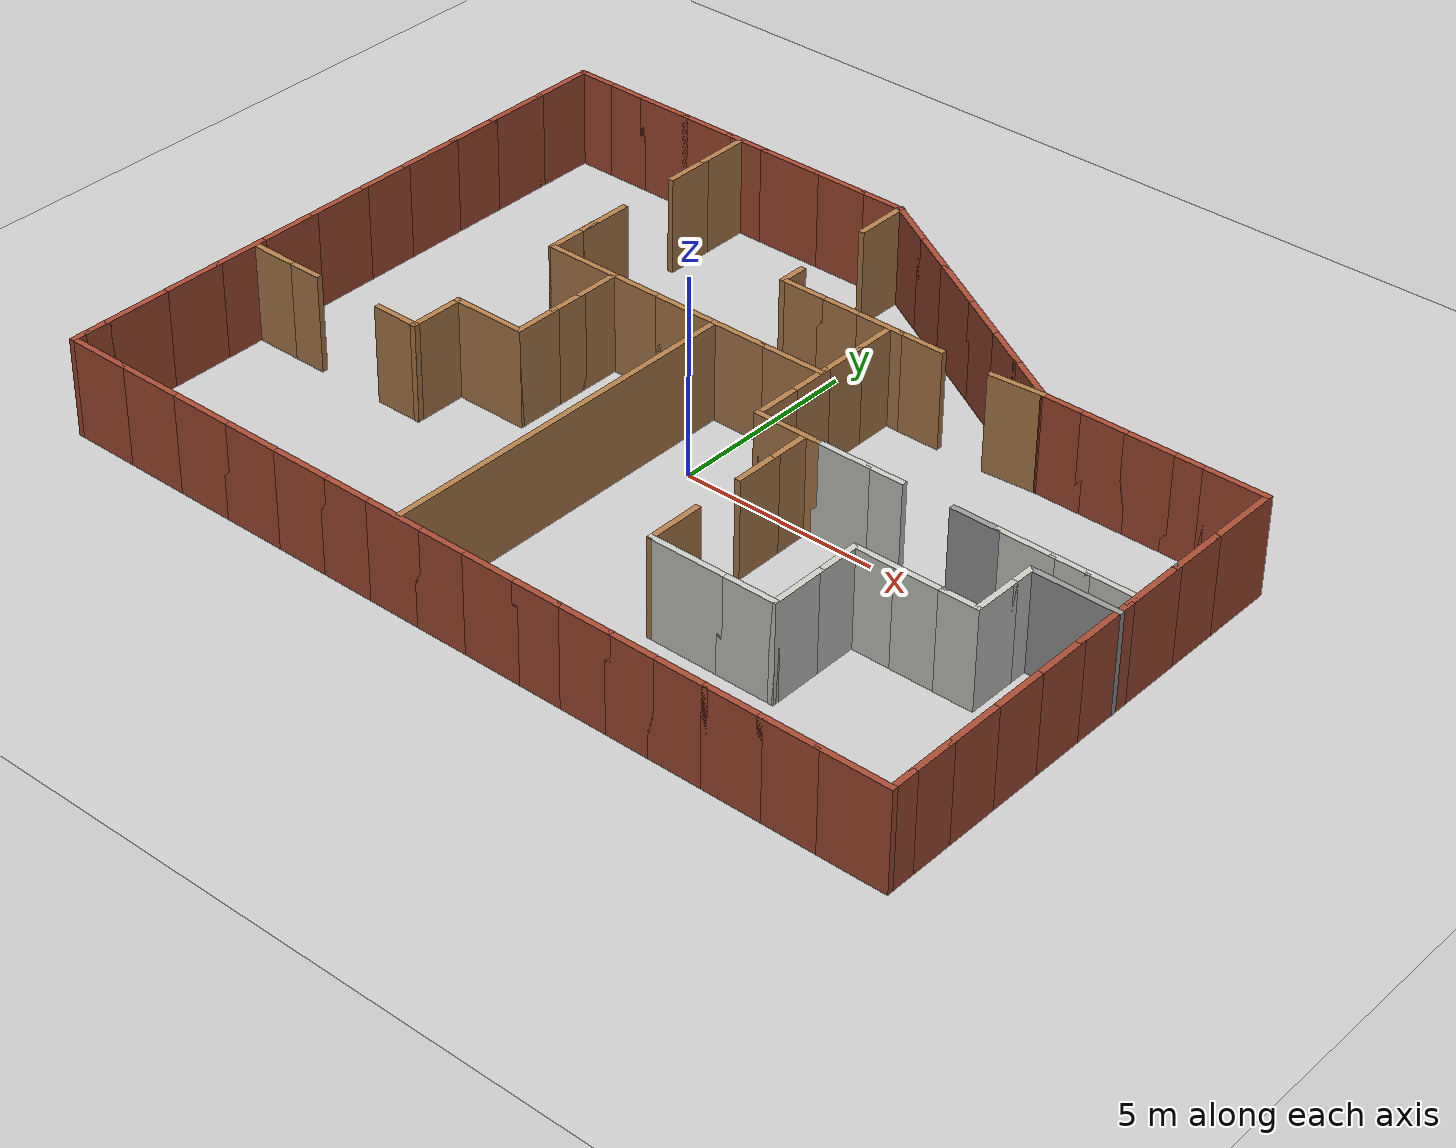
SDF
<sdf version="1.7">
 <world name="default">
  <light name="sun" type="directional">
   <pose>0 0 10 0 -0 0</pose>
   <diffuse>0.8 0.8 0.8 1</diffuse>
   <specular>0.2 0.2 0.2 1</specular>
   <attenuation>
    <range>1000</range>
    <constant>0.9</constant>
    <linear>0.01</linear>
    <quadratic>0.001</quadratic>
   </attenuation>
   <direction>-0.5 0.1 -0.9</direction>
   <spot><inner_angle>0</inner_angle><outer_angle>0</outer_angle><falloff>0</falloff></spot>
  </light>
  <model name="ground_plane">
   <static>1</static>
   <link name="link">
    <collision name="collision">
     <geometry><plane><normal>0 0 1</normal><size>100 100</size></plane></geometry>
     <surface>
      <contact><collide_bitmask>65535</collide_bitmask></contact>
      <friction><ode><mu>100</mu><mu2>50</mu2></ode></friction>
     </surface>
    </collision>
    <visual name="visual">
     <cast_shadows>0</cast_shadows>
     <geometry><plane><normal>0 0 1</normal><size>100 100</size></plane></geometry>
     <material>
      <script><uri>file://media/materials/scripts/gazebo.material</uri><name>Gazebo/Grey</name></script>
     </material>
    </visual>
   </link>
  </model>
  <gravity>0 0 -9.8</gravity>
  <magnetic_field>6e-06 2.3e-05 -4.2e-05</magnetic_field>
  <atmosphere type="adiabatic"/>
  <physics type="ode">
   <max_step_size>0.001</max_step_size>
   <real_time_factor>1</real_time_factor>
   <real_time_update_rate>1000</real_time_update_rate>
  </physics>
  <scene><ambient>0.4 0.4 0.4 1</ambient><background>0.7 0.7 0.7 1</background><shadows>1</shadows></scene>
  <spherical_coordinates>
   <surface_model>EARTH_WGS84</surface_model>
   <latitude_deg>0</latitude_deg>
   <longitude_deg>0</longitude_deg>
   <elevation>0</elevation>
   <heading_deg>0</heading_deg>
  </spherical_coordinates>
  <model name="Building">
   <link name="Wall_100">
    <pose>10.6129 -0.475005 0 0 -0 0</pose>
    <visual name="Wall_100_Visual">
     <pose>0 0 1.25 0 -0 0</pose>
     <geometry><box><size>1.25 0.15 2.5</size></box></geometry>
     <material>
      <script><uri>file://media/materials/scripts/gazebo.material</uri><name>Gazebo/CeilingTiled</name></script>
      <ambient>1 1 1 1</ambient>
      <shader type="pixel"/>
     </material>
     <meta><layer>0</layer></meta>
    </visual>
    <collision name="Wall_100_Collision">
     <pose>0 0 1.25 0 -0 0</pose>
     <geometry><box><size>1.25 0.15 2.5</size></box></geometry>
     <surface>
      <friction>
       <ode><mu>1</mu><mu2>1</mu2><fdir1>0 0 0</fdir1><slip1>0</slip1><slip2>0</slip2></ode>
       <torsional>
        <coefficient>1</coefficient>
        <patch_radius>0</patch_radius>
        <surface_radius>0</surface_radius>
        <use_patch_radius>1</use_patch_radius>
        <ode><slip>0</slip></ode>
       </torsional>
      </friction>
      <bounce><restitution_coefficient>0</restitution_coefficient><threshold>1e+06</threshold></bounce>
      <contact>
       <collide_without_contact>0</collide_without_contact>
       <collide_without_contact_bitmask>1</collide_without_contact_bitmask>
       <collide_bitmask>1</collide_bitmask>
       <ode>
        <soft_cfm>0</soft_cfm>
        <soft_erp>0.2</soft_erp>
        <kp>1e+13</kp>
        <kd>1</kd>
        <max_vel>0.01</max_vel>
        <min_depth>0</min_depth>
       </ode>
       <bullet>
        <split_impulse>1</split_impulse>
        <split_impulse_penetration_threshold>-0.01</split_impulse_penetration_threshold>
        <soft_cfm>0</soft_cfm>
        <soft_erp>0.2</soft_erp>
        <kp>1e+13</kp>
        <kd>1</kd>
       </bullet>
      </contact>
     </surface>
    </collision>
   </link>
   <link name="Wall_102">
    <pose>-6.17365 7.40796 0 0 0 -1.5708</pose>
    <visual name="Wall_102_Visual">
     <pose>0 0 1.25 0 -0 0</pose>
     <geometry><box><size>1.5 0.15 2.5</size></box></geometry>
     <material>
      <script><uri>file://media/materials/scripts/gazebo.material</uri><name>Gazebo/Wood</name></script>
      <ambient>1 1 1 1</ambient>
      <shader type="pixel"/>
     </material>
     <meta><layer>0</layer></meta>
    </visual>
    <collision name="Wall_102_Collision">
     <pose>0 0 1.25 0 -0 0</pose>
     <geometry><box><size>1.5 0.15 2.5</size></box></geometry>
     <surface>
      <friction>
       <ode><mu>1</mu><mu2>1</mu2><fdir1>0 0 0</fdir1><slip1>0</slip1><slip2>0</slip2></ode>
       <torsional>
        <coefficient>1</coefficient>
        <patch_radius>0</patch_radius>
        <surface_radius>0</surface_radius>
        <use_patch_radius>1</use_patch_radius>
        <ode><slip>0</slip></ode>
       </torsional>
      </friction>
      <bounce><restitution_coefficient>0</restitution_coefficient><threshold>1e+06</threshold></bounce>
      <contact>
       <collide_without_contact>0</collide_without_contact>
       <collide_without_contact_bitmask>1</collide_without_contact_bitmask>
       <collide_bitmask>1</collide_bitmask>
       <ode>
        <soft_cfm>0</soft_cfm>
        <soft_erp>0.2</soft_erp>
        <kp>1e+13</kp>
        <kd>1</kd>
        <max_vel>0.01</max_vel>
        <min_depth>0</min_depth>
       </ode>
       <bullet>
        <split_impulse>1</split_impulse>
        <split_impulse_penetration_threshold>-0.01</split_impulse_penetration_threshold>
        <soft_cfm>0</soft_cfm>
        <soft_erp>0.2</soft_erp>
        <kp>1e+13</kp>
        <kd>1</kd>
       </bullet>
      </contact>
     </surface>
    </collision>
   </link>
   <link name="Wall_103">
    <pose>-6.17365 6.18296 0 0 0 -1.5708</pose>
    <visual name="Wall_103_Visual">
     <pose>0 0 1.25 0 -0 0</pose>
     <geometry><box><size>1.25 0.15 2.5</size></box></geometry>
     <material>
      <script><uri>file://media/materials/scripts/gazebo.material</uri><name>Gazebo/Wood</name></script>
      <ambient>1 1 1 1</ambient>
      <shader type="pixel"/>
     </material>
     <meta><layer>0</layer></meta>
    </visual>
    <collision name="Wall_103_Collision">
     <pose>0 0 1.25 0 -0 0</pose>
     <geometry><box><size>1.25 0.15 2.5</size></box></geometry>
     <surface>
      <friction>
       <ode><mu>1</mu><mu2>1</mu2><fdir1>0 0 0</fdir1><slip1>0</slip1><slip2>0</slip2></ode>
       <torsional>
        <coefficient>1</coefficient>
        <patch_radius>0</patch_radius>
        <surface_radius>0</surface_radius>
        <use_patch_radius>1</use_patch_radius>
        <ode><slip>0</slip></ode>
       </torsional>
      </friction>
      <bounce><restitution_coefficient>0</restitution_coefficient><threshold>1e+06</threshold></bounce>
      <contact>
       <collide_without_contact>0</collide_without_contact>
       <collide_without_contact_bitmask>1</collide_without_contact_bitmask>
       <collide_bitmask>1</collide_bitmask>
       <ode>
        <soft_cfm>0</soft_cfm>
        <soft_erp>0.2</soft_erp>
        <kp>1e+13</kp>
        <kd>1</kd>
        <max_vel>0.01</max_vel>
        <min_depth>0</min_depth>
       </ode>
       <bullet>
        <split_impulse>1</split_impulse>
        <split_impulse_penetration_threshold>-0.01</split_impulse_penetration_threshold>
        <soft_cfm>0</soft_cfm>
        <soft_erp>0.2</soft_erp>
        <kp>1e+13</kp>
        <kd>1</kd>
       </bullet>
      </contact>
     </surface>
    </collision>
   </link>
   <link name="Wall_106">
    <pose>-6.17365 2.25796 0 0 0 -1.5708</pose>
    <visual name="Wall_106_Visual">
     <pose>0 0 1.25 0 -0 0</pose>
     <geometry><box><size>1.5 0.15 2.5</size></box></geometry>
     <material>
      <script><uri>file://media/materials/scripts/gazebo.material</uri><name>Gazebo/Wood</name></script>
      <ambient>1 1 1 1</ambient>
      <shader type="pixel"/>
     </material>
     <meta><layer>0</layer></meta>
    </visual>
    <collision name="Wall_106_Collision">
     <pose>0 0 1.25 0 -0 0</pose>
     <geometry><box><size>1.5 0.15 2.5</size></box></geometry>
     <surface>
      <friction>
       <ode><mu>1</mu><mu2>1</mu2><fdir1>0 0 0</fdir1><slip1>0</slip1><slip2>0</slip2></ode>
       <torsional>
        <coefficient>1</coefficient>
        <patch_radius>0</patch_radius>
        <surface_radius>0</surface_radius>
        <use_patch_radius>1</use_patch_radius>
        <ode><slip>0</slip></ode>
       </torsional>
      </friction>
      <bounce><restitution_coefficient>0</restitution_coefficient><threshold>1e+06</threshold></bounce>
      <contact>
       <collide_without_contact>0</collide_without_contact>
       <collide_without_contact_bitmask>1</collide_without_contact_bitmask>
       <collide_bitmask>1</collide_bitmask>
       <ode>
        <soft_cfm>0</soft_cfm>
        <soft_erp>0.2</soft_erp>
        <kp>1e+13</kp>
        <kd>1</kd>
        <max_vel>0.01</max_vel>
        <min_depth>0</min_depth>
       </ode>
       <bullet>
        <split_impulse>1</split_impulse>
        <split_impulse_penetration_threshold>-0.01</split_impulse_penetration_threshold>
        <soft_cfm>0</soft_cfm>
        <soft_erp>0.2</soft_erp>
        <kp>1e+13</kp>
        <kd>1</kd>
       </bullet>
      </contact>
     </surface>
    </collision>
   </link>
   <link name="Wall_106_clone">
    <pose>-6.16432 3.24691 0 0 0 -1.5708</pose>
    <visual name="Wall_106_Visual">
     <pose>0 0 1.25 0 -0 0</pose>
     <geometry><box><size>1.5 0.15 2.5</size></box></geometry>
     <material>
      <script><uri>file://media/materials/scripts/gazebo.material</uri><name>Gazebo/Wood</name></script>
      <ambient>1 1 1 1</ambient>
      <shader type="pixel"/>
     </material>
     <meta><layer>0</layer></meta>
    </visual>
    <collision name="Wall_106_Collision">
     <pose>0 0 1.25 0 -0 0</pose>
     <geometry><box><size>1.5 0.15 2.5</size></box></geometry>
     <surface>
      <friction>
       <ode><mu>1</mu><mu2>1</mu2><fdir1>0 0 0</fdir1><slip1>0</slip1><slip2>0</slip2></ode>
       <torsional>
        <coefficient>1</coefficient>
        <patch_radius>0</patch_radius>
        <surface_radius>0</surface_radius>
        <use_patch_radius>1</use_patch_radius>
        <ode><slip>0</slip></ode>
       </torsional>
      </friction>
      <bounce><restitution_coefficient>0</restitution_coefficient><threshold>1e+06</threshold></bounce>
      <contact>
       <collide_without_contact>0</collide_without_contact>
       <collide_without_contact_bitmask>1</collide_without_contact_bitmask>
       <collide_bitmask>1</collide_bitmask>
       <ode>
        <soft_cfm>0</soft_cfm>
        <soft_erp>0.2</soft_erp>
        <kp>1e+13</kp>
        <kd>1</kd>
        <max_vel>0.01</max_vel>
        <min_depth>0</min_depth>
       </ode>
       <bullet>
        <split_impulse>1</split_impulse>
        <split_impulse_penetration_threshold>-0.01</split_impulse_penetration_threshold>
        <soft_cfm>0</soft_cfm>
        <soft_erp>0.2</soft_erp>
        <kp>1e+13</kp>
        <kd>1</kd>
       </bullet>
      </contact>
     </surface>
    </collision>
   </link>
   <link name="Wall_107">
    <pose>-5.24865 1.58296 0 0 -0 0</pose>
    <visual name="Wall_107_Visual">
     <pose>0 0 1.25 0 -0 0</pose>
     <geometry><box><size>2 0.15 2.5</size></box></geometry>
     <material>
      <script><uri>file://media/materials/scripts/gazebo.material</uri><name>Gazebo/Wood</name></script>
      <ambient>1 1 1 1</ambient>
      <shader type="pixel"/>
     </material>
     <meta><layer>0</layer></meta>
    </visual>
    <collision name="Wall_107_Collision">
     <pose>0 0 1.25 0 -0 0</pose>
     <geometry><box><size>2 0.15 2.5</size></box></geometry>
     <surface>
      <friction>
       <ode><mu>1</mu><mu2>1</mu2><fdir1>0 0 0</fdir1><slip1>0</slip1><slip2>0</slip2></ode>
       <torsional>
        <coefficient>1</coefficient>
        <patch_radius>0</patch_radius>
        <surface_radius>0</surface_radius>
        <use_patch_radius>1</use_patch_radius>
        <ode><slip>0</slip></ode>
       </torsional>
      </friction>
      <bounce><restitution_coefficient>0</restitution_coefficient><threshold>1e+06</threshold></bounce>
      <contact>
       <collide_without_contact>0</collide_without_contact>
       <collide_without_contact_bitmask>1</collide_without_contact_bitmask>
       <collide_bitmask>1</collide_bitmask>
       <ode>
        <soft_cfm>0</soft_cfm>
        <soft_erp>0.2</soft_erp>
        <kp>1e+13</kp>
        <kd>1</kd>
        <max_vel>0.01</max_vel>
        <min_depth>0</min_depth>
       </ode>
       <bullet>
        <split_impulse>1</split_impulse>
        <split_impulse_penetration_threshold>-0.01</split_impulse_penetration_threshold>
        <soft_cfm>0</soft_cfm>
        <soft_erp>0.2</soft_erp>
        <kp>1e+13</kp>
        <kd>1</kd>
       </bullet>
      </contact>
     </surface>
    </collision>
   </link>
   <link name="Wall_108">
    <pose>-3.64865 1.58296 0 0 -0 0</pose>
    <visual name="Wall_108_Visual">
     <pose>0 0 1.25 0 -0 0</pose>
     <geometry><box><size>1.5 0.15 2.5</size></box></geometry>
     <material>
      <script><uri>file://media/materials/scripts/gazebo.material</uri><name>Gazebo/Wood</name></script>
      <ambient>1 1 1 1</ambient>
      <shader type="pixel"/>
     </material>
     <meta><layer>0</layer></meta>
    </visual>
    <collision name="Wall_108_Collision">
     <pose>0 0 1.25 0 -0 0</pose>
     <geometry><box><size>1.5 0.15 2.5</size></box></geometry>
     <surface>
      <friction>
       <ode><mu>1</mu><mu2>1</mu2><fdir1>0 0 0</fdir1><slip1>0</slip1><slip2>0</slip2></ode>
       <torsional>
        <coefficient>1</coefficient>
        <patch_radius>0</patch_radius>
        <surface_radius>0</surface_radius>
        <use_patch_radius>1</use_patch_radius>
        <ode><slip>0</slip></ode>
       </torsional>
      </friction>
      <bounce><restitution_coefficient>0</restitution_coefficient><threshold>1e+06</threshold></bounce>
      <contact>
       <collide_without_contact>0</collide_without_contact>
       <collide_without_contact_bitmask>1</collide_without_contact_bitmask>
       <collide_bitmask>1</collide_bitmask>
       <ode>
        <soft_cfm>0</soft_cfm>
        <soft_erp>0.2</soft_erp>
        <kp>1e+13</kp>
        <kd>1</kd>
        <max_vel>0.01</max_vel>
        <min_depth>0</min_depth>
       </ode>
       <bullet>
        <split_impulse>1</split_impulse>
        <split_impulse_penetration_threshold>-0.01</split_impulse_penetration_threshold>
        <soft_cfm>0</soft_cfm>
        <soft_erp>0.2</soft_erp>
        <kp>1e+13</kp>
        <kd>1</kd>
       </bullet>
      </contact>
     </surface>
    </collision>
   </link>
   <link name="Wall_109">
    <pose>-2.17365 1.58296 0 0 -0 0</pose>
    <visual name="Wall_109_Visual">
     <pose>0 0 1.25 0 -0 0</pose>
     <geometry><box><size>1.75 0.15 2.5</size></box></geometry>
     <material>
      <script><uri>file://media/materials/scripts/gazebo.material</uri><name>Gazebo/Wood</name></script>
      <ambient>1 1 1 1</ambient>
      <shader type="pixel"/>
     </material>
     <meta><layer>0</layer></meta>
    </visual>
    <collision name="Wall_109_Collision">
     <pose>0 0 1.25 0 -0 0</pose>
     <geometry><box><size>1.75 0.15 2.5</size></box></geometry>
     <surface>
      <friction>
       <ode><mu>1</mu><mu2>1</mu2><fdir1>0 0 0</fdir1><slip1>0</slip1><slip2>0</slip2></ode>
       <torsional>
        <coefficient>1</coefficient>
        <patch_radius>0</patch_radius>
        <surface_radius>0</surface_radius>
        <use_patch_radius>1</use_patch_radius>
        <ode><slip>0</slip></ode>
       </torsional>
      </friction>
      <bounce><restitution_coefficient>0</restitution_coefficient><threshold>1e+06</threshold></bounce>
      <contact>
       <collide_without_contact>0</collide_without_contact>
       <collide_without_contact_bitmask>1</collide_without_contact_bitmask>
       <collide_bitmask>1</collide_bitmask>
       <ode>
        <soft_cfm>0</soft_cfm>
        <soft_erp>0.2</soft_erp>
        <kp>1e+13</kp>
        <kd>1</kd>
        <max_vel>0.01</max_vel>
        <min_depth>0</min_depth>
       </ode>
       <bullet>
        <split_impulse>1</split_impulse>
        <split_impulse_penetration_threshold>-0.01</split_impulse_penetration_threshold>
        <soft_cfm>0</soft_cfm>
        <soft_erp>0.2</soft_erp>
        <kp>1e+13</kp>
        <kd>1</kd>
       </bullet>
      </contact>
     </surface>
    </collision>
   </link>
   <link name="Wall_11">
    <pose>11.2288 3.11127 0 0 0 -1.5708</pose>
    <visual name="Wall_11_Visual">
     <pose>0 0 1.25 0 -0 0</pose>
     <geometry><box><size>2 0.15 2.5</size></box></geometry>
     <material>
      <script><uri>file://media/materials/scripts/gazebo.material</uri><name>Gazebo/Bricks</name></script>
      <ambient>1 1 1 1</ambient>
      <shader type="pixel"/>
     </material>
     <meta><layer>0</layer></meta>
    </visual>
    <collision name="Wall_11_Collision">
     <pose>0 0 1.25 0 -0 0</pose>
     <geometry><box><size>2 0.15 2.5</size></box></geometry>
     <surface>
      <friction>
       <ode><mu>1</mu><mu2>1</mu2><fdir1>0 0 0</fdir1><slip1>0</slip1><slip2>0</slip2></ode>
       <torsional>
        <coefficient>1</coefficient>
        <patch_radius>0</patch_radius>
        <surface_radius>0</surface_radius>
        <use_patch_radius>1</use_patch_radius>
        <ode><slip>0</slip></ode>
       </torsional>
      </friction>
      <bounce><restitution_coefficient>0</restitution_coefficient><threshold>1e+06</threshold></bounce>
      <contact>
       <collide_without_contact>0</collide_without_contact>
       <collide_without_contact_bitmask>1</collide_without_contact_bitmask>
       <collide_bitmask>1</collide_bitmask>
       <ode>
        <soft_cfm>0</soft_cfm>
        <soft_erp>0.2</soft_erp>
        <kp>1e+13</kp>
        <kd>1</kd>
        <max_vel>0.01</max_vel>
        <min_depth>0</min_depth>
       </ode>
       <bullet>
        <split_impulse>1</split_impulse>
        <split_impulse_penetration_threshold>-0.01</split_impulse_penetration_threshold>
        <soft_cfm>0</soft_cfm>
        <soft_erp>0.2</soft_erp>
        <kp>1e+13</kp>
        <kd>1</kd>
       </bullet>
      </contact>
     </surface>
    </collision>
   </link>
   <link name="Wall_110">
    <pose>-0.698653 1.58296 0 0 -0 0</pose>
    <visual name="Wall_110_Visual">
     <pose>0 0 1.25 0 -0 0</pose>
     <geometry><box><size>1.5 0.15 2.5</size></box></geometry>
     <material>
      <script><uri>file://media/materials/scripts/gazebo.material</uri><name>Gazebo/Wood</name></script>
      <ambient>1 1 1 1</ambient>
      <shader type="pixel"/>
     </material>
     <meta><layer>0</layer></meta>
    </visual>
    <collision name="Wall_110_Collision">
     <pose>0 0 1.25 0 -0 0</pose>
     <geometry><box><size>1.5 0.15 2.5</size></box></geometry>
     <surface>
      <friction>
       <ode><mu>1</mu><mu2>1</mu2><fdir1>0 0 0</fdir1><slip1>0</slip1><slip2>0</slip2></ode>
       <torsional>
        <coefficient>1</coefficient>
        <patch_radius>0</patch_radius>
        <surface_radius>0</surface_radius>
        <use_patch_radius>1</use_patch_radius>
        <ode><slip>0</slip></ode>
       </torsional>
      </friction>
      <bounce><restitution_coefficient>0</restitution_coefficient><threshold>1e+06</threshold></bounce>
      <contact>
       <collide_without_contact>0</collide_without_contact>
       <collide_without_contact_bitmask>1</collide_without_contact_bitmask>
       <collide_bitmask>1</collide_bitmask>
       <ode>
        <soft_cfm>0</soft_cfm>
        <soft_erp>0.2</soft_erp>
        <kp>1e+13</kp>
        <kd>1</kd>
        <max_vel>0.01</max_vel>
        <min_depth>0</min_depth>
       </ode>
       <bullet>
        <split_impulse>1</split_impulse>
        <split_impulse_penetration_threshold>-0.01</split_impulse_penetration_threshold>
        <soft_cfm>0</soft_cfm>
        <soft_erp>0.2</soft_erp>
        <kp>1e+13</kp>
        <kd>1</kd>
       </bullet>
      </contact>
     </surface>
    </collision>
   </link>
   <link name="Wall_113">
    <pose>0.776346 1.58296 0 0 -0 0</pose>
    <visual name="Wall_113_Visual">
     <pose>0 0 1.25 0 -0 0</pose>
     <geometry><box><size>1.75 0.15 2.5</size></box></geometry>
     <material>
      <script><uri>file://media/materials/scripts/gazebo.material</uri><name>Gazebo/Wood</name></script>
      <ambient>1 1 1 1</ambient>
      <shader type="pixel"/>
     </material>
     <meta><layer>0</layer></meta>
    </visual>
    <collision name="Wall_113_Collision">
     <pose>0 0 1.25 0 -0 0</pose>
     <geometry><box><size>1.75 0.15 2.5</size></box></geometry>
     <surface>
      <friction>
       <ode><mu>1</mu><mu2>1</mu2><fdir1>0 0 0</fdir1><slip1>0</slip1><slip2>0</slip2></ode>
       <torsional>
        <coefficient>1</coefficient>
        <patch_radius>0</patch_radius>
        <surface_radius>0</surface_radius>
        <use_patch_radius>1</use_patch_radius>
        <ode><slip>0</slip></ode>
       </torsional>
      </friction>
      <bounce><restitution_coefficient>0</restitution_coefficient><threshold>1e+06</threshold></bounce>
      <contact>
       <collide_without_contact>0</collide_without_contact>
       <collide_without_contact_bitmask>1</collide_without_contact_bitmask>
       <collide_bitmask>1</collide_bitmask>
       <ode>
        <soft_cfm>0</soft_cfm>
        <soft_erp>0.2</soft_erp>
        <kp>1e+13</kp>
        <kd>1</kd>
        <max_vel>0.01</max_vel>
        <min_depth>0</min_depth>
       </ode>
       <bullet>
        <split_impulse>1</split_impulse>
        <split_impulse_penetration_threshold>-0.01</split_impulse_penetration_threshold>
        <soft_cfm>0</soft_cfm>
        <soft_erp>0.2</soft_erp>
        <kp>1e+13</kp>
        <kd>1</kd>
       </bullet>
      </contact>
     </surface>
    </collision>
   </link>
   <link name="Wall_115">
    <pose>-4.32365 1.03296 0 0 0 -1.5708</pose>
    <visual name="Wall_115_Visual">
     <pose>0 0 1.25 0 -0 0</pose>
     <geometry><box><size>1.25 0.15 2.5</size></box></geometry>
     <material>
      <script><uri>file://media/materials/scripts/gazebo.material</uri><name>Gazebo/Wood</name></script>
      <ambient>1 1 1 1</ambient>
      <shader type="pixel"/>
     </material>
     <meta><layer>0</layer></meta>
    </visual>
    <collision name="Wall_115_Collision">
     <pose>0 0 1.25 0 -0 0</pose>
     <geometry><box><size>1.25 0.15 2.5</size></box></geometry>
     <surface>
      <friction>
       <ode><mu>1</mu><mu2>1</mu2><fdir1>0 0 0</fdir1><slip1>0</slip1><slip2>0</slip2></ode>
       <torsional>
        <coefficient>1</coefficient>
        <patch_radius>0</patch_radius>
        <surface_radius>0</surface_radius>
        <use_patch_radius>1</use_patch_radius>
        <ode><slip>0</slip></ode>
       </torsional>
      </friction>
      <bounce><restitution_coefficient>0</restitution_coefficient><threshold>1e+06</threshold></bounce>
      <contact>
       <collide_without_contact>0</collide_without_contact>
       <collide_without_contact_bitmask>1</collide_without_contact_bitmask>
       <collide_bitmask>1</collide_bitmask>
       <ode>
        <soft_cfm>0</soft_cfm>
        <soft_erp>0.2</soft_erp>
        <kp>1e+13</kp>
        <kd>1</kd>
        <max_vel>0.01</max_vel>
        <min_depth>0</min_depth>
       </ode>
       <bullet>
        <split_impulse>1</split_impulse>
        <split_impulse_penetration_threshold>-0.01</split_impulse_penetration_threshold>
        <soft_cfm>0</soft_cfm>
        <soft_erp>0.2</soft_erp>
        <kp>1e+13</kp>
        <kd>1</kd>
       </bullet>
      </contact>
     </surface>
    </collision>
   </link>
   <link name="Wall_116">
    <pose>-4.32365 0.057961 0 0 0 -1.5708</pose>
    <visual name="Wall_116_Visual">
     <pose>0 0 1.25 0 -0 0</pose>
     <geometry><box><size>1 0.15 2.5</size></box></geometry>
     <material>
      <script><uri>file://media/materials/scripts/gazebo.material</uri><name>Gazebo/Wood</name></script>
      <ambient>1 1 1 1</ambient>
      <shader type="pixel"/>
     </material>
     <meta><layer>0</layer></meta>
    </visual>
    <collision name="Wall_116_Collision">
     <pose>0 0 1.25 0 -0 0</pose>
     <geometry><box><size>1 0.15 2.5</size></box></geometry>
     <surface>
      <friction>
       <ode><mu>1</mu><mu2>1</mu2><fdir1>0 0 0</fdir1><slip1>0</slip1><slip2>0</slip2></ode>
       <torsional>
        <coefficient>1</coefficient>
        <patch_radius>0</patch_radius>
        <surface_radius>0</surface_radius>
        <use_patch_radius>1</use_patch_radius>
        <ode><slip>0</slip></ode>
       </torsional>
      </friction>
      <bounce><restitution_coefficient>0</restitution_coefficient><threshold>1e+06</threshold></bounce>
      <contact>
       <collide_without_contact>0</collide_without_contact>
       <collide_without_contact_bitmask>1</collide_without_contact_bitmask>
       <collide_bitmask>1</collide_bitmask>
       <ode>
        <soft_cfm>0</soft_cfm>
        <soft_erp>0.2</soft_erp>
        <kp>1e+13</kp>
        <kd>1</kd>
        <max_vel>0.01</max_vel>
        <min_depth>0</min_depth>
       </ode>
       <bullet>
        <split_impulse>1</split_impulse>
        <split_impulse_penetration_threshold>-0.01</split_impulse_penetration_threshold>
        <soft_cfm>0</soft_cfm>
        <soft_erp>0.2</soft_erp>
        <kp>1e+13</kp>
        <kd>1</kd>
       </bullet>
      </contact>
     </surface>
    </collision>
   </link>
   <link name="Wall_117">
    <pose>-4.32365 -0.917039 0 0 0 -1.5708</pose>
    <visual name="Wall_117_Visual">
     <pose>0 0 1.25 0 -0 0</pose>
     <geometry><box><size>1.25 0.15 2.5</size></box></geometry>
     <material>
      <script><uri>file://media/materials/scripts/gazebo.material</uri><name>Gazebo/Wood</name></script>
      <ambient>1 1 1 1</ambient>
      <shader type="pixel"/>
     </material>
     <meta><layer>0</layer></meta>
    </visual>
    <collision name="Wall_117_Collision">
     <pose>0 0 1.25 0 -0 0</pose>
     <geometry><box><size>1.25 0.15 2.5</size></box></geometry>
     <surface>
      <friction>
       <ode><mu>1</mu><mu2>1</mu2><fdir1>0 0 0</fdir1><slip1>0</slip1><slip2>0</slip2></ode>
       <torsional>
        <coefficient>1</coefficient>
        <patch_radius>0</patch_radius>
        <surface_radius>0</surface_radius>
        <use_patch_radius>1</use_patch_radius>
        <ode><slip>0</slip></ode>
       </torsional>
      </friction>
      <bounce><restitution_coefficient>0</restitution_coefficient><threshold>1e+06</threshold></bounce>
      <contact>
       <collide_without_contact>0</collide_without_contact>
       <collide_without_contact_bitmask>1</collide_without_contact_bitmask>
       <collide_bitmask>1</collide_bitmask>
       <ode>
        <soft_cfm>0</soft_cfm>
        <soft_erp>0.2</soft_erp>
        <kp>1e+13</kp>
        <kd>1</kd>
        <max_vel>0.01</max_vel>
        <min_depth>0</min_depth>
       </ode>
       <bullet>
        <split_impulse>1</split_impulse>
        <split_impulse_penetration_threshold>-0.01</split_impulse_penetration_threshold>
        <soft_cfm>0</soft_cfm>
        <soft_erp>0.2</soft_erp>
        <kp>1e+13</kp>
        <kd>1</kd>
       </bullet>
      </contact>
     </surface>
    </collision>
   </link>
   <link name="Wall_118">
    <pose>-5.24865 -1.46704 0 0 -0 3.14159</pose>
    <visual name="Wall_118_Visual">
     <pose>0 0 1.25 0 -0 0</pose>
     <geometry><box><size>2 0.15 2.5</size></box></geometry>
     <material>
      <script><uri>file://media/materials/scripts/gazebo.material</uri><name>Gazebo/Wood</name></script>
      <ambient>1 1 1 1</ambient>
      <shader type="pixel"/>
     </material>
     <meta><layer>0</layer></meta>
    </visual>
    <collision name="Wall_118_Collision">
     <pose>0 0 1.25 0 -0 0</pose>
     <geometry><box><size>2 0.15 2.5</size></box></geometry>
     <surface>
      <friction>
       <ode><mu>1</mu><mu2>1</mu2><fdir1>0 0 0</fdir1><slip1>0</slip1><slip2>0</slip2></ode>
       <torsional>
        <coefficient>1</coefficient>
        <patch_radius>0</patch_radius>
        <surface_radius>0</surface_radius>
        <use_patch_radius>1</use_patch_radius>
        <ode><slip>0</slip></ode>
       </torsional>
      </friction>
      <bounce><restitution_coefficient>0</restitution_coefficient><threshold>1e+06</threshold></bounce>
      <contact>
       <collide_without_contact>0</collide_without_contact>
       <collide_without_contact_bitmask>1</collide_without_contact_bitmask>
       <collide_bitmask>1</collide_bitmask>
       <ode>
        <soft_cfm>0</soft_cfm>
        <soft_erp>0.2</soft_erp>
        <kp>1e+13</kp>
        <kd>1</kd>
        <max_vel>0.01</max_vel>
        <min_depth>0</min_depth>
       </ode>
       <bullet>
        <split_impulse>1</split_impulse>
        <split_impulse_penetration_threshold>-0.01</split_impulse_penetration_threshold>
        <soft_cfm>0</soft_cfm>
        <soft_erp>0.2</soft_erp>
        <kp>1e+13</kp>
        <kd>1</kd>
       </bullet>
      </contact>
     </surface>
    </collision>
   </link>
   <link name="Wall_119">
    <pose>-6.17365 -2.14204 0 0 0 -1.5708</pose>
    <visual name="Wall_119_Visual">
     <pose>0 0 1.25 0 -0 0</pose>
     <geometry><box><size>1.5 0.15 2.5</size></box></geometry>
     <material>
      <script><uri>file://media/materials/scripts/gazebo.material</uri><name>Gazebo/Wood</name></script>
      <ambient>1 1 1 1</ambient>
      <shader type="pixel"/>
     </material>
     <meta><layer>0</layer></meta>
    </visual>
    <collision name="Wall_119_Collision">
     <pose>0 0 1.25 0 -0 0</pose>
     <geometry><box><size>1.5 0.15 2.5</size></box></geometry>
     <surface>
      <friction>
       <ode><mu>1</mu><mu2>1</mu2><fdir1>0 0 0</fdir1><slip1>0</slip1><slip2>0</slip2></ode>
       <torsional>
        <coefficient>1</coefficient>
        <patch_radius>0</patch_radius>
        <surface_radius>0</surface_radius>
        <use_patch_radius>1</use_patch_radius>
        <ode><slip>0</slip></ode>
       </torsional>
      </friction>
      <bounce><restitution_coefficient>0</restitution_coefficient><threshold>1e+06</threshold></bounce>
      <contact>
       <collide_without_contact>0</collide_without_contact>
       <collide_without_contact_bitmask>1</collide_without_contact_bitmask>
       <collide_bitmask>1</collide_bitmask>
       <ode>
        <soft_cfm>0</soft_cfm>
        <soft_erp>0.2</soft_erp>
        <kp>1e+13</kp>
        <kd>1</kd>
        <max_vel>0.01</max_vel>
        <min_depth>0</min_depth>
       </ode>
       <bullet>
        <split_impulse>1</split_impulse>
        <split_impulse_penetration_threshold>-0.01</split_impulse_penetration_threshold>
        <soft_cfm>0</soft_cfm>
        <soft_erp>0.2</soft_erp>
        <kp>1e+13</kp>
        <kd>1</kd>
       </bullet>
      </contact>
     </surface>
    </collision>
   </link>
   <link name="Wall_120">
    <pose>-6.72365 -2.81704 0 0 -0 3.14159</pose>
    <visual name="Wall_120_Visual">
     <pose>0 0 1.25 0 -0 0</pose>
     <geometry><box><size>1.25 0.15 2.5</size></box></geometry>
     <material>
      <script><uri>file://media/materials/scripts/gazebo.material</uri><name>Gazebo/Wood</name></script>
      <ambient>1 1 1 1</ambient>
      <shader type="pixel"/>
     </material>
     <meta><layer>0</layer></meta>
    </visual>
    <collision name="Wall_120_Collision">
     <pose>0 0 1.25 0 -0 0</pose>
     <geometry><box><size>1.25 0.15 2.5</size></box></geometry>
     <surface>
      <friction>
       <ode><mu>1</mu><mu2>1</mu2><fdir1>0 0 0</fdir1><slip1>0</slip1><slip2>0</slip2></ode>
       <torsional>
        <coefficient>1</coefficient>
        <patch_radius>0</patch_radius>
        <surface_radius>0</surface_radius>
        <use_patch_radius>1</use_patch_radius>
        <ode><slip>0</slip></ode>
       </torsional>
      </friction>
      <bounce><restitution_coefficient>0</restitution_coefficient><threshold>1e+06</threshold></bounce>
      <contact>
       <collide_without_contact>0</collide_without_contact>
       <collide_without_contact_bitmask>1</collide_without_contact_bitmask>
       <collide_bitmask>1</collide_bitmask>
       <ode>
        <soft_cfm>0</soft_cfm>
        <soft_erp>0.2</soft_erp>
        <kp>1e+13</kp>
        <kd>1</kd>
        <max_vel>0.01</max_vel>
        <min_depth>0</min_depth>
       </ode>
       <bullet>
        <split_impulse>1</split_impulse>
        <split_impulse_penetration_threshold>-0.01</split_impulse_penetration_threshold>
        <soft_cfm>0</soft_cfm>
        <soft_erp>0.2</soft_erp>
        <kp>1e+13</kp>
        <kd>1</kd>
       </bullet>
      </contact>
     </surface>
    </collision>
   </link>
   <link name="Wall_123">
    <pose>-9.64865 -2.81704 0 0 -0 3.14159</pose>
    <visual name="Wall_123_Visual">
     <pose>0 0 1.25 0 -0 0</pose>
     <geometry><box><size>1 0.15 2.5</size></box></geometry>
     <material>
      <script><uri>file://media/materials/scripts/gazebo.material</uri><name>Gazebo/Wood</name></script>
      <ambient>1 1 1 1</ambient>
      <shader type="pixel"/>
     </material>
     <meta><layer>0</layer></meta>
    </visual>
    <collision name="Wall_123_Collision">
     <pose>0 0 1.25 0 -0 0</pose>
     <geometry><box><size>1 0.15 2.5</size></box></geometry>
     <surface>
      <friction>
       <ode><mu>1</mu><mu2>1</mu2><fdir1>0 0 0</fdir1><slip1>0</slip1><slip2>0</slip2></ode>
       <torsional>
        <coefficient>1</coefficient>
        <patch_radius>0</patch_radius>
        <surface_radius>0</surface_radius>
        <use_patch_radius>1</use_patch_radius>
        <ode><slip>0</slip></ode>
       </torsional>
      </friction>
      <bounce><restitution_coefficient>0</restitution_coefficient><threshold>1e+06</threshold></bounce>
      <contact>
       <collide_without_contact>0</collide_without_contact>
       <collide_without_contact_bitmask>1</collide_without_contact_bitmask>
       <collide_bitmask>1</collide_bitmask>
       <ode>
        <soft_cfm>0</soft_cfm>
        <soft_erp>0.2</soft_erp>
        <kp>1e+13</kp>
        <kd>1</kd>
        <max_vel>0.01</max_vel>
        <min_depth>0</min_depth>
       </ode>
       <bullet>
        <split_impulse>1</split_impulse>
        <split_impulse_penetration_threshold>-0.01</split_impulse_penetration_threshold>
        <soft_cfm>0</soft_cfm>
        <soft_erp>0.2</soft_erp>
        <kp>1e+13</kp>
        <kd>1</kd>
       </bullet>
      </contact>
     </surface>
    </collision>
   </link>
   <link name="Wall_124">
    <pose>-10.6237 -2.81704 0 0 -0 3.14159</pose>
    <visual name="Wall_124_Visual">
     <pose>0 0 1.25 0 -0 0</pose>
     <geometry><box><size>1.25 0.15 2.5</size></box></geometry>
     <material>
      <script><uri>file://media/materials/scripts/gazebo.material</uri><name>Gazebo/Wood</name></script>
      <ambient>1 1 1 1</ambient>
      <shader type="pixel"/>
     </material>
     <meta><layer>0</layer></meta>
    </visual>
    <collision name="Wall_124_Collision">
     <pose>0 0 1.25 0 -0 0</pose>
     <geometry><box><size>1.25 0.15 2.5</size></box></geometry>
     <surface>
      <friction>
       <ode><mu>1</mu><mu2>1</mu2><fdir1>0 0 0</fdir1><slip1>0</slip1><slip2>0</slip2></ode>
       <torsional>
        <coefficient>1</coefficient>
        <patch_radius>0</patch_radius>
        <surface_radius>0</surface_radius>
        <use_patch_radius>1</use_patch_radius>
        <ode><slip>0</slip></ode>
       </torsional>
      </friction>
      <bounce><restitution_coefficient>0</restitution_coefficient><threshold>1e+06</threshold></bounce>
      <contact>
       <collide_without_contact>0</collide_without_contact>
       <collide_without_contact_bitmask>1</collide_without_contact_bitmask>
       <collide_bitmask>1</collide_bitmask>
       <ode>
        <soft_cfm>0</soft_cfm>
        <soft_erp>0.2</soft_erp>
        <kp>1e+13</kp>
        <kd>1</kd>
        <max_vel>0.01</max_vel>
        <min_depth>0</min_depth>
       </ode>
       <bullet>
        <split_impulse>1</split_impulse>
        <split_impulse_penetration_threshold>-0.01</split_impulse_penetration_threshold>
        <soft_cfm>0</soft_cfm>
        <soft_erp>0.2</soft_erp>
        <kp>1e+13</kp>
        <kd>1</kd>
       </bullet>
      </contact>
     </surface>
    </collision>
   </link>
   <link name="Wall_126">
    <pose>2.88596 -1.03693 0 0 0 -1.5708</pose>
    <visual name="Wall_126_Visual">
     <pose>0 0 1.25 0 -0 0</pose>
     <geometry><box><size>1 0.15 2.5</size></box></geometry>
     <material>
      <script><uri>file://media/materials/scripts/gazebo.material</uri><name>Gazebo/Wood</name></script>
      <ambient>1 1 1 1</ambient>
      <shader type="pixel"/>
     </material>
     <meta><layer>0</layer></meta>
    </visual>
    <collision name="Wall_126_Collision">
     <pose>0 0 1.25 0 -0 0</pose>
     <geometry><box><size>1 0.15 2.5</size></box></geometry>
     <surface>
      <friction>
       <ode><mu>1</mu><mu2>1</mu2><fdir1>0 0 0</fdir1><slip1>0</slip1><slip2>0</slip2></ode>
       <torsional>
        <coefficient>1</coefficient>
        <patch_radius>0</patch_radius>
        <surface_radius>0</surface_radius>
        <use_patch_radius>1</use_patch_radius>
        <ode><slip>0</slip></ode>
       </torsional>
      </friction>
      <bounce><restitution_coefficient>0</restitution_coefficient><threshold>1e+06</threshold></bounce>
      <contact>
       <collide_without_contact>0</collide_without_contact>
       <collide_without_contact_bitmask>1</collide_without_contact_bitmask>
       <collide_bitmask>1</collide_bitmask>
       <ode>
        <soft_cfm>0</soft_cfm>
        <soft_erp>0.2</soft_erp>
        <kp>1e+13</kp>
        <kd>1</kd>
        <max_vel>0.01</max_vel>
        <min_depth>0</min_depth>
       </ode>
       <bullet>
        <split_impulse>1</split_impulse>
        <split_impulse_penetration_threshold>-0.01</split_impulse_penetration_threshold>
        <soft_cfm>0</soft_cfm>
        <soft_erp>0.2</soft_erp>
        <kp>1e+13</kp>
        <kd>1</kd>
       </bullet>
      </contact>
     </surface>
    </collision>
   </link>
   <link name="Wall_127">
    <pose>2.88596 -2.01193 0 0 0 -1.5708</pose>
    <visual name="Wall_127_Visual">
     <pose>0 0 1.25 0 -0 0</pose>
     <geometry><box><size>1.25 0.15 2.5</size></box></geometry>
     <material>
      <script><uri>file://media/materials/scripts/gazebo.material</uri><name>Gazebo/Wood</name></script>
      <ambient>1 1 1 1</ambient>
      <shader type="pixel"/>
     </material>
     <meta><layer>0</layer></meta>
    </visual>
    <collision name="Wall_127_Collision">
     <pose>0 0 1.25 0 -0 0</pose>
     <geometry><box><size>1.25 0.15 2.5</size></box></geometry>
     <surface>
      <friction>
       <ode><mu>1</mu><mu2>1</mu2><fdir1>0 0 0</fdir1><slip1>0</slip1><slip2>0</slip2></ode>
       <torsional>
        <coefficient>1</coefficient>
        <patch_radius>0</patch_radius>
        <surface_radius>0</surface_radius>
        <use_patch_radius>1</use_patch_radius>
        <ode><slip>0</slip></ode>
       </torsional>
      </friction>
      <bounce><restitution_coefficient>0</restitution_coefficient><threshold>1e+06</threshold></bounce>
      <contact>
       <collide_without_contact>0</collide_without_contact>
       <collide_without_contact_bitmask>1</collide_without_contact_bitmask>
       <collide_bitmask>1</collide_bitmask>
       <ode>
        <soft_cfm>0</soft_cfm>
        <soft_erp>0.2</soft_erp>
        <kp>1e+13</kp>
        <kd>1</kd>
        <max_vel>0.01</max_vel>
        <min_depth>0</min_depth>
       </ode>
       <bullet>
        <split_impulse>1</split_impulse>
        <split_impulse_penetration_threshold>-0.01</split_impulse_penetration_threshold>
        <soft_cfm>0</soft_cfm>
        <soft_erp>0.2</soft_erp>
        <kp>1e+13</kp>
        <kd>1</kd>
       </bullet>
      </contact>
     </surface>
    </collision>
   </link>
   <link name="Wall_129">
    <pose>2.88596 -4.58694 0 0 0 -1.5708</pose>
    <visual name="Wall_129_Visual">
     <pose>0 0 1.25 0 -0 0</pose>
     <geometry><box><size>1.5 0.15 2.5</size></box></geometry>
     <material>
      <script><uri>file://media/materials/scripts/gazebo.material</uri><name>Gazebo/Wood</name></script>
      <ambient>1 1 1 1</ambient>
      <shader type="pixel"/>
     </material>
     <meta><layer>0</layer></meta>
    </visual>
    <collision name="Wall_129_Collision">
     <pose>0 0 1.25 0 -0 0</pose>
     <geometry><box><size>1.5 0.15 2.5</size></box></geometry>
     <surface>
      <friction>
       <ode><mu>1</mu><mu2>1</mu2><fdir1>0 0 0</fdir1><slip1>0</slip1><slip2>0</slip2></ode>
       <torsional>
        <coefficient>1</coefficient>
        <patch_radius>0</patch_radius>
        <surface_radius>0</surface_radius>
        <use_patch_radius>1</use_patch_radius>
        <ode><slip>0</slip></ode>
       </torsional>
      </friction>
      <bounce><restitution_coefficient>0</restitution_coefficient><threshold>1e+06</threshold></bounce>
      <contact>
       <collide_without_contact>0</collide_without_contact>
       <collide_without_contact_bitmask>1</collide_without_contact_bitmask>
       <collide_bitmask>1</collide_bitmask>
       <ode>
        <soft_cfm>0</soft_cfm>
        <soft_erp>0.2</soft_erp>
        <kp>1e+13</kp>
        <kd>1</kd>
        <max_vel>0.01</max_vel>
        <min_depth>0</min_depth>
       </ode>
       <bullet>
        <split_impulse>1</split_impulse>
        <split_impulse_penetration_threshold>-0.01</split_impulse_penetration_threshold>
        <soft_cfm>0</soft_cfm>
        <soft_erp>0.2</soft_erp>
        <kp>1e+13</kp>
        <kd>1</kd>
       </bullet>
      </contact>
     </surface>
    </collision>
   </link>
   <link name="Wall_13">
    <pose>-11.236 5.68627 0 0 0 -1.5708</pose>
    <visual name="Wall_13_Visual">
     <pose>0 0 1.25 0 -0 0</pose>
     <geometry><box><size>1.75 0.15 2.5</size></box></geometry>
     <material>
      <script><uri>file://media/materials/scripts/gazebo.material</uri><name>Gazebo/Bricks</name></script>
      <ambient>1 1 1 1</ambient>
      <shader type="pixel"/>
     </material>
     <meta><layer>0</layer></meta>
    </visual>
    <collision name="Wall_13_Collision">
     <pose>0 0 1.25 0 -0 0</pose>
     <geometry><box><size>1.75 0.15 2.5</size></box></geometry>
     <surface>
      <friction>
       <ode><mu>1</mu><mu2>1</mu2><fdir1>0 0 0</fdir1><slip1>0</slip1><slip2>0</slip2></ode>
       <torsional>
        <coefficient>1</coefficient>
        <patch_radius>0</patch_radius>
        <surface_radius>0</surface_radius>
        <use_patch_radius>1</use_patch_radius>
        <ode><slip>0</slip></ode>
       </torsional>
      </friction>
      <bounce><restitution_coefficient>0</restitution_coefficient><threshold>1e+06</threshold></bounce>
      <contact>
       <collide_without_contact>0</collide_without_contact>
       <collide_without_contact_bitmask>1</collide_without_contact_bitmask>
       <collide_bitmask>1</collide_bitmask>
       <ode>
        <soft_cfm>0</soft_cfm>
        <soft_erp>0.2</soft_erp>
        <kp>1e+13</kp>
        <kd>1</kd>
        <max_vel>0.01</max_vel>
        <min_depth>0</min_depth>
       </ode>
       <bullet>
        <split_impulse>1</split_impulse>
        <split_impulse_penetration_threshold>-0.01</split_impulse_penetration_threshold>
        <soft_cfm>0</soft_cfm>
        <soft_erp>0.2</soft_erp>
        <kp>1e+13</kp>
        <kd>1</kd>
       </bullet>
      </contact>
     </surface>
    </collision>
   </link>
   <link name="Wall_130">
    <pose>3.81096 -5.26194 0 0 -0 0</pose>
    <visual name="Wall_130_Visual">
     <pose>0 0 1.25 0 -0 0</pose>
     <geometry><box><size>2 0.15 2.5</size></box></geometry>
     <material>
      <script><uri>file://media/materials/scripts/gazebo.material</uri><name>Gazebo/CeilingTiled</name></script>
      <ambient>1 1 1 1</ambient>
      <shader type="pixel"/>
     </material>
     <meta><layer>0</layer></meta>
    </visual>
    <collision name="Wall_130_Collision">
     <pose>0 0 1.25 0 -0 0</pose>
     <geometry><box><size>2 0.15 2.5</size></box></geometry>
     <surface>
      <friction>
       <ode><mu>1</mu><mu2>1</mu2><fdir1>0 0 0</fdir1><slip1>0</slip1><slip2>0</slip2></ode>
       <torsional>
        <coefficient>1</coefficient>
        <patch_radius>0</patch_radius>
        <surface_radius>0</surface_radius>
        <use_patch_radius>1</use_patch_radius>
        <ode><slip>0</slip></ode>
       </torsional>
      </friction>
      <bounce><restitution_coefficient>0</restitution_coefficient><threshold>1e+06</threshold></bounce>
      <contact>
       <collide_without_contact>0</collide_without_contact>
       <collide_without_contact_bitmask>1</collide_without_contact_bitmask>
       <collide_bitmask>1</collide_bitmask>
       <ode>
        <soft_cfm>0</soft_cfm>
        <soft_erp>0.2</soft_erp>
        <kp>1e+13</kp>
        <kd>1</kd>
        <max_vel>0.01</max_vel>
        <min_depth>0</min_depth>
       </ode>
       <bullet>
        <split_impulse>1</split_impulse>
        <split_impulse_penetration_threshold>-0.01</split_impulse_penetration_threshold>
        <soft_cfm>0</soft_cfm>
        <soft_erp>0.2</soft_erp>
        <kp>1e+13</kp>
        <kd>1</kd>
       </bullet>
      </contact>
     </surface>
    </collision>
   </link>
   <link name="Wall_131">
    <pose>5.41096 -5.26194 0 0 -0 0</pose>
    <visual name="Wall_131_Visual">
     <pose>0 0 1.25 0 -0 0</pose>
     <geometry><box><size>1.5 0.15 2.5</size></box></geometry>
     <material>
      <script><uri>file://media/materials/scripts/gazebo.material</uri><name>Gazebo/CeilingTiled</name></script>
      <ambient>1 1 1 1</ambient>
      <shader type="pixel"/>
     </material>
     <meta><layer>0</layer></meta>
    </visual>
    <collision name="Wall_131_Collision">
     <pose>0 0 1.25 0 -0 0</pose>
     <geometry><box><size>1.5 0.15 2.5</size></box></geometry>
     <surface>
      <friction>
       <ode><mu>1</mu><mu2>1</mu2><fdir1>0 0 0</fdir1><slip1>0</slip1><slip2>0</slip2></ode>
       <torsional>
        <coefficient>1</coefficient>
        <patch_radius>0</patch_radius>
        <surface_radius>0</surface_radius>
        <use_patch_radius>1</use_patch_radius>
        <ode><slip>0</slip></ode>
       </torsional>
      </friction>
      <bounce><restitution_coefficient>0</restitution_coefficient><threshold>1e+06</threshold></bounce>
      <contact>
       <collide_without_contact>0</collide_without_contact>
       <collide_without_contact_bitmask>1</collide_without_contact_bitmask>
       <collide_bitmask>1</collide_bitmask>
       <ode>
        <soft_cfm>0</soft_cfm>
        <soft_erp>0.2</soft_erp>
        <kp>1e+13</kp>
        <kd>1</kd>
        <max_vel>0.01</max_vel>
        <min_depth>0</min_depth>
       </ode>
       <bullet>
        <split_impulse>1</split_impulse>
        <split_impulse_penetration_threshold>-0.01</split_impulse_penetration_threshold>
        <soft_cfm>0</soft_cfm>
        <soft_erp>0.2</soft_erp>
        <kp>1e+13</kp>
        <kd>1</kd>
       </bullet>
      </contact>
     </surface>
    </collision>
   </link>
   <link name="Wall_132">
    <pose>6.08596 -4.58694 0 0 -0 1.5708</pose>
    <visual name="Wall_132_Visual">
     <pose>0 0 1.25 0 -0 0</pose>
     <geometry><box><size>1.5 0.15 2.5</size></box></geometry>
     <material>
      <script><uri>file://media/materials/scripts/gazebo.material</uri><name>Gazebo/CeilingTiled</name></script>
      <ambient>1 1 1 1</ambient>
      <shader type="pixel"/>
     </material>
     <meta><layer>0</layer></meta>
    </visual>
    <collision name="Wall_132_Collision">
     <pose>0 0 1.25 0 -0 0</pose>
     <geometry><box><size>1.5 0.15 2.5</size></box></geometry>
     <surface>
      <friction>
       <ode><mu>1</mu><mu2>1</mu2><fdir1>0 0 0</fdir1><slip1>0</slip1><slip2>0</slip2></ode>
       <torsional>
        <coefficient>1</coefficient>
        <patch_radius>0</patch_radius>
        <surface_radius>0</surface_radius>
        <use_patch_radius>1</use_patch_radius>
        <ode><slip>0</slip></ode>
       </torsional>
      </friction>
      <bounce><restitution_coefficient>0</restitution_coefficient><threshold>1e+06</threshold></bounce>
      <contact>
       <collide_without_contact>0</collide_without_contact>
       <collide_without_contact_bitmask>1</collide_without_contact_bitmask>
       <collide_bitmask>1</collide_bitmask>
       <ode>
        <soft_cfm>0</soft_cfm>
        <soft_erp>0.2</soft_erp>
        <kp>1e+13</kp>
        <kd>1</kd>
        <max_vel>0.01</max_vel>
        <min_depth>0</min_depth>
       </ode>
       <bullet>
        <split_impulse>1</split_impulse>
        <split_impulse_penetration_threshold>-0.01</split_impulse_penetration_threshold>
        <soft_cfm>0</soft_cfm>
        <soft_erp>0.2</soft_erp>
        <kp>1e+13</kp>
        <kd>1</kd>
       </bullet>
      </contact>
     </surface>
    </collision>
   </link>
   <link name="Wall_133">
    <pose>6.08596 -3.36193 0 0 -0 1.5708</pose>
    <visual name="Wall_133_Visual">
     <pose>0 0 1.25 0 -0 0</pose>
     <geometry><box><size>1.25 0.15 2.5</size></box></geometry>
     <material>
      <script><uri>file://media/materials/scripts/gazebo.material</uri><name>Gazebo/CeilingTiled</name></script>
      <ambient>1 1 1 1</ambient>
      <shader type="pixel"/>
     </material>
     <meta><layer>0</layer></meta>
    </visual>
    <collision name="Wall_133_Collision">
     <pose>0 0 1.25 0 -0 0</pose>
     <geometry><box><size>1.25 0.15 2.5</size></box></geometry>
     <surface>
      <friction>
       <ode><mu>1</mu><mu2>1</mu2><fdir1>0 0 0</fdir1><slip1>0</slip1><slip2>0</slip2></ode>
       <torsional>
        <coefficient>1</coefficient>
        <patch_radius>0</patch_radius>
        <surface_radius>0</surface_radius>
        <use_patch_radius>1</use_patch_radius>
        <ode><slip>0</slip></ode>
       </torsional>
      </friction>
      <bounce><restitution_coefficient>0</restitution_coefficient><threshold>1e+06</threshold></bounce>
      <contact>
       <collide_without_contact>0</collide_without_contact>
       <collide_without_contact_bitmask>1</collide_without_contact_bitmask>
       <collide_bitmask>1</collide_bitmask>
       <ode>
        <soft_cfm>0</soft_cfm>
        <soft_erp>0.2</soft_erp>
        <kp>1e+13</kp>
        <kd>1</kd>
        <max_vel>0.01</max_vel>
        <min_depth>0</min_depth>
       </ode>
       <bullet>
        <split_impulse>1</split_impulse>
        <split_impulse_penetration_threshold>-0.01</split_impulse_penetration_threshold>
        <soft_cfm>0</soft_cfm>
        <soft_erp>0.2</soft_erp>
        <kp>1e+13</kp>
        <kd>1</kd>
       </bullet>
      </contact>
     </surface>
    </collision>
   </link>
   <link name="Wall_134">
    <pose>6.63596 -2.81194 0 0 -0 0</pose>
    <visual name="Wall_134_Visual">
     <pose>0 0 1.25 0 -0 0</pose>
     <geometry><box><size>1.25 0.15 2.5</size></box></geometry>
     <material>
      <script><uri>file://media/materials/scripts/gazebo.material</uri><name>Gazebo/CeilingTiled</name></script>
      <ambient>1 1 1 1</ambient>
      <shader type="pixel"/>
     </material>
     <meta><layer>0</layer></meta>
    </visual>
    <collision name="Wall_134_Collision">
     <pose>0 0 1.25 0 -0 0</pose>
     <geometry><box><size>1.25 0.15 2.5</size></box></geometry>
     <surface>
      <friction>
       <ode><mu>1</mu><mu2>1</mu2><fdir1>0 0 0</fdir1><slip1>0</slip1><slip2>0</slip2></ode>
       <torsional>
        <coefficient>1</coefficient>
        <patch_radius>0</patch_radius>
        <surface_radius>0</surface_radius>
        <use_patch_radius>1</use_patch_radius>
        <ode><slip>0</slip></ode>
       </torsional>
      </friction>
      <bounce><restitution_coefficient>0</restitution_coefficient><threshold>1e+06</threshold></bounce>
      <contact>
       <collide_without_contact>0</collide_without_contact>
       <collide_without_contact_bitmask>1</collide_without_contact_bitmask>
       <collide_bitmask>1</collide_bitmask>
       <ode>
        <soft_cfm>0</soft_cfm>
        <soft_erp>0.2</soft_erp>
        <kp>1e+13</kp>
        <kd>1</kd>
        <max_vel>0.01</max_vel>
        <min_depth>0</min_depth>
       </ode>
       <bullet>
        <split_impulse>1</split_impulse>
        <split_impulse_penetration_threshold>-0.01</split_impulse_penetration_threshold>
        <soft_cfm>0</soft_cfm>
        <soft_erp>0.2</soft_erp>
        <kp>1e+13</kp>
        <kd>1</kd>
       </bullet>
      </contact>
     </surface>
    </collision>
   </link>
   <link name="Wall_135">
    <pose>7.73596 -2.81194 0 0 -0 0</pose>
    <visual name="Wall_135_Visual">
     <pose>0 0 1.25 0 -0 0</pose>
     <geometry><box><size>1.25 0.15 2.5</size></box></geometry>
     <material>
      <script><uri>file://media/materials/scripts/gazebo.material</uri><name>Gazebo/CeilingTiled</name></script>
      <ambient>1 1 1 1</ambient>
      <shader type="pixel"/>
     </material>
     <meta><layer>0</layer></meta>
    </visual>
    <collision name="Wall_135_Collision">
     <pose>0 0 1.25 0 -0 0</pose>
     <geometry><box><size>1.25 0.15 2.5</size></box></geometry>
     <surface>
      <friction>
       <ode><mu>1</mu><mu2>1</mu2><fdir1>0 0 0</fdir1><slip1>0</slip1><slip2>0</slip2></ode>
       <torsional>
        <coefficient>1</coefficient>
        <patch_radius>0</patch_radius>
        <surface_radius>0</surface_radius>
        <use_patch_radius>1</use_patch_radius>
        <ode><slip>0</slip></ode>
       </torsional>
      </friction>
      <bounce><restitution_coefficient>0</restitution_coefficient><threshold>1e+06</threshold></bounce>
      <contact>
       <collide_without_contact>0</collide_without_contact>
       <collide_without_contact_bitmask>1</collide_without_contact_bitmask>
       <collide_bitmask>1</collide_bitmask>
       <ode>
        <soft_cfm>0</soft_cfm>
        <soft_erp>0.2</soft_erp>
        <kp>1e+13</kp>
        <kd>1</kd>
        <max_vel>0.01</max_vel>
        <min_depth>0</min_depth>
       </ode>
       <bullet>
        <split_impulse>1</split_impulse>
        <split_impulse_penetration_threshold>-0.01</split_impulse_penetration_threshold>
        <soft_cfm>0</soft_cfm>
        <soft_erp>0.2</soft_erp>
        <kp>1e+13</kp>
        <kd>1</kd>
       </bullet>
      </contact>
     </surface>
    </collision>
   </link>
   <link name="Wall_136">
    <pose>8.71096 -2.81194 0 0 -0 0</pose>
    <visual name="Wall_136_Visual">
     <pose>0 0 1.25 0 -0 0</pose>
     <geometry><box><size>1 0.15 2.5</size></box></geometry>
     <material>
      <script><uri>file://media/materials/scripts/gazebo.material</uri><name>Gazebo/CeilingTiled</name></script>
      <ambient>1 1 1 1</ambient>
      <shader type="pixel"/>
     </material>
     <meta><layer>0</layer></meta>
    </visual>
    <collision name="Wall_136_Collision">
     <pose>0 0 1.25 0 -0 0</pose>
     <geometry><box><size>1 0.15 2.5</size></box></geometry>
     <surface>
      <friction>
       <ode><mu>1</mu><mu2>1</mu2><fdir1>0 0 0</fdir1><slip1>0</slip1><slip2>0</slip2></ode>
       <torsional>
        <coefficient>1</coefficient>
        <patch_radius>0</patch_radius>
        <surface_radius>0</surface_radius>
        <use_patch_radius>1</use_patch_radius>
        <ode><slip>0</slip></ode>
       </torsional>
      </friction>
      <bounce><restitution_coefficient>0</restitution_coefficient><threshold>1e+06</threshold></bounce>
      <contact>
       <collide_without_contact>0</collide_without_contact>
       <collide_without_contact_bitmask>1</collide_without_contact_bitmask>
       <collide_bitmask>1</collide_bitmask>
       <ode>
        <soft_cfm>0</soft_cfm>
        <soft_erp>0.2</soft_erp>
        <kp>1e+13</kp>
        <kd>1</kd>
        <max_vel>0.01</max_vel>
        <min_depth>0</min_depth>
       </ode>
       <bullet>
        <split_impulse>1</split_impulse>
        <split_impulse_penetration_threshold>-0.01</split_impulse_penetration_threshold>
        <soft_cfm>0</soft_cfm>
        <soft_erp>0.2</soft_erp>
        <kp>1e+13</kp>
        <kd>1</kd>
       </bullet>
      </contact>
     </surface>
    </collision>
   </link>
   <link name="Wall_137">
    <pose>9.13596 -2.26193 0 0 -0 1.5708</pose>
    <visual name="Wall_137_Visual">
     <pose>0 0 1.25 0 -0 0</pose>
     <geometry><box><size>1.25 0.15 2.5</size></box></geometry>
     <material>
      <script><uri>file://media/materials/scripts/gazebo.material</uri><name>Gazebo/CeilingTiled</name></script>
      <ambient>1 1 1 1</ambient>
      <shader type="pixel"/>
     </material>
     <meta><layer>0</layer></meta>
    </visual>
    <collision name="Wall_137_Collision">
     <pose>0 0 1.25 0 -0 0</pose>
     <geometry><box><size>1.25 0.15 2.5</size></box></geometry>
     <surface>
      <friction>
       <ode><mu>1</mu><mu2>1</mu2><fdir1>0 0 0</fdir1><slip1>0</slip1><slip2>0</slip2></ode>
       <torsional>
        <coefficient>1</coefficient>
        <patch_radius>0</patch_radius>
        <surface_radius>0</surface_radius>
        <use_patch_radius>1</use_patch_radius>
        <ode><slip>0</slip></ode>
       </torsional>
      </friction>
      <bounce><restitution_coefficient>0</restitution_coefficient><threshold>1e+06</threshold></bounce>
      <contact>
       <collide_without_contact>0</collide_without_contact>
       <collide_without_contact_bitmask>1</collide_without_contact_bitmask>
       <collide_bitmask>1</collide_bitmask>
       <ode>
        <soft_cfm>0</soft_cfm>
        <soft_erp>0.2</soft_erp>
        <kp>1e+13</kp>
        <kd>1</kd>
        <max_vel>0.01</max_vel>
        <min_depth>0</min_depth>
       </ode>
       <bullet>
        <split_impulse>1</split_impulse>
        <split_impulse_penetration_threshold>-0.01</split_impulse_penetration_threshold>
        <soft_cfm>0</soft_cfm>
        <soft_erp>0.2</soft_erp>
        <kp>1e+13</kp>
        <kd>1</kd>
       </bullet>
      </contact>
     </surface>
    </collision>
   </link>
   <link name="Wall_138">
    <pose>9.13596 -1.41193 0 0 -0 1.5708</pose>
    <visual name="Wall_138_Visual">
     <pose>0 0 1.25 0 -0 0</pose>
     <geometry><box><size>0.75 0.15 2.5</size></box></geometry>
     <material>
      <script><uri>file://media/materials/scripts/gazebo.material</uri><name>Gazebo/CeilingTiled</name></script>
      <ambient>1 1 1 1</ambient>
      <shader type="pixel"/>
     </material>
     <meta><layer>0</layer></meta>
    </visual>
    <collision name="Wall_138_Collision">
     <pose>0 0 1.25 0 -0 0</pose>
     <geometry><box><size>0.75 0.15 2.5</size></box></geometry>
     <surface>
      <friction>
       <ode><mu>1</mu><mu2>1</mu2><fdir1>0 0 0</fdir1><slip1>0</slip1><slip2>0</slip2></ode>
       <torsional>
        <coefficient>1</coefficient>
        <patch_radius>0</patch_radius>
        <surface_radius>0</surface_radius>
        <use_patch_radius>1</use_patch_radius>
        <ode><slip>0</slip></ode>
       </torsional>
      </friction>
      <bounce><restitution_coefficient>0</restitution_coefficient><threshold>1e+06</threshold></bounce>
      <contact>
       <collide_without_contact>0</collide_without_contact>
       <collide_without_contact_bitmask>1</collide_without_contact_bitmask>
       <collide_bitmask>1</collide_bitmask>
       <ode>
        <soft_cfm>0</soft_cfm>
        <soft_erp>0.2</soft_erp>
        <kp>1e+13</kp>
        <kd>1</kd>
        <max_vel>0.01</max_vel>
        <min_depth>0</min_depth>
       </ode>
       <bullet>
        <split_impulse>1</split_impulse>
        <split_impulse_penetration_threshold>-0.01</split_impulse_penetration_threshold>
        <soft_cfm>0</soft_cfm>
        <soft_erp>0.2</soft_erp>
        <kp>1e+13</kp>
        <kd>1</kd>
       </bullet>
      </contact>
     </surface>
    </collision>
   </link>
   <link name="Wall_14">
    <pose>-11.236 4.21127 0 0 0 -1.5708</pose>
    <visual name="Wall_14_Visual">
     <pose>0 0 1.25 0 -0 0</pose>
     <geometry><box><size>1.5 0.15 2.5</size></box></geometry>
     <material>
      <script><uri>file://media/materials/scripts/gazebo.material</uri><name>Gazebo/Bricks</name></script>
      <ambient>1 1 1 1</ambient>
      <shader type="pixel"/>
     </material>
     <meta><layer>0</layer></meta>
    </visual>
    <collision name="Wall_14_Collision">
     <pose>0 0 1.25 0 -0 0</pose>
     <geometry><box><size>1.5 0.15 2.5</size></box></geometry>
     <surface>
      <friction>
       <ode><mu>1</mu><mu2>1</mu2><fdir1>0 0 0</fdir1><slip1>0</slip1><slip2>0</slip2></ode>
       <torsional>
        <coefficient>1</coefficient>
        <patch_radius>0</patch_radius>
        <surface_radius>0</surface_radius>
        <use_patch_radius>1</use_patch_radius>
        <ode><slip>0</slip></ode>
       </torsional>
      </friction>
      <bounce><restitution_coefficient>0</restitution_coefficient><threshold>1e+06</threshold></bounce>
      <contact>
       <collide_without_contact>0</collide_without_contact>
       <collide_without_contact_bitmask>1</collide_without_contact_bitmask>
       <collide_bitmask>1</collide_bitmask>
       <ode>
        <soft_cfm>0</soft_cfm>
        <soft_erp>0.2</soft_erp>
        <kp>1e+13</kp>
        <kd>1</kd>
        <max_vel>0.01</max_vel>
        <min_depth>0</min_depth>
       </ode>
       <bullet>
        <split_impulse>1</split_impulse>
        <split_impulse_penetration_threshold>-0.01</split_impulse_penetration_threshold>
        <soft_cfm>0</soft_cfm>
        <soft_erp>0.2</soft_erp>
        <kp>1e+13</kp>
        <kd>1</kd>
       </bullet>
      </contact>
     </surface>
    </collision>
   </link>
   <link name="Wall_144">
    <pose>10.186 -1.11193 0 0 -0 0</pose>
    <visual name="Wall_144_Visual">
     <pose>0 0 1.25 0 -0 0</pose>
     <geometry><box><size>2.25 0.15 2.5</size></box></geometry>
     <material>
      <script><uri>file://media/materials/scripts/gazebo.material</uri><name>Gazebo/Grey</name></script>
      <ambient>1 1 1 1</ambient>
      <shader type="pixel"/>
     </material>
     <meta><layer>0</layer></meta>
    </visual>
    <collision name="Wall_144_Collision">
     <pose>0 0 1.25 0 -0 0</pose>
     <geometry><box><size>2.25 0.15 2.5</size></box></geometry>
     <surface>
      <friction>
       <ode><mu>1</mu><mu2>1</mu2><fdir1>0 0 0</fdir1><slip1>0</slip1><slip2>0</slip2></ode>
       <torsional>
        <coefficient>1</coefficient>
        <patch_radius>0</patch_radius>
        <surface_radius>0</surface_radius>
        <use_patch_radius>1</use_patch_radius>
        <ode><slip>0</slip></ode>
       </torsional>
      </friction>
      <bounce><restitution_coefficient>0</restitution_coefficient><threshold>1e+06</threshold></bounce>
      <contact>
       <collide_without_contact>0</collide_without_contact>
       <collide_without_contact_bitmask>1</collide_without_contact_bitmask>
       <collide_bitmask>1</collide_bitmask>
       <ode>
        <soft_cfm>0</soft_cfm>
        <soft_erp>0.2</soft_erp>
        <kp>1e+13</kp>
        <kd>1</kd>
        <max_vel>0.01</max_vel>
        <min_depth>0</min_depth>
       </ode>
       <bullet>
        <split_impulse>1</split_impulse>
        <split_impulse_penetration_threshold>-0.01</split_impulse_penetration_threshold>
        <soft_cfm>0</soft_cfm>
        <soft_erp>0.2</soft_erp>
        <kp>1e+13</kp>
        <kd>1</kd>
       </bullet>
      </contact>
     </surface>
    </collision>
   </link>
   <link name="Wall_146">
    <pose>-1.37365 -3.21704 0 0 0 -1.5708</pose>
    <visual name="Wall_146_Visual">
     <pose>0 0 1.25 0 -0 0</pose>
     <geometry><box><size>9.75 0.15 2.5</size></box></geometry>
     <material>
      <script><uri>file://media/materials/scripts/gazebo.material</uri><name>Gazebo/Wood</name></script>
      <ambient>1 1 1 1</ambient>
      <shader type="pixel"/>
     </material>
     <meta><layer>0</layer></meta>
    </visual>
    <collision name="Wall_146_Collision">
     <pose>0 0 1.25 0 -0 0</pose>
     <geometry><box><size>9.75 0.15 2.5</size></box></geometry>
     <surface>
      <friction>
       <ode><mu>1</mu><mu2>1</mu2><fdir1>0 0 0</fdir1><slip1>0</slip1><slip2>0</slip2></ode>
       <torsional>
        <coefficient>1</coefficient>
        <patch_radius>0</patch_radius>
        <surface_radius>0</surface_radius>
        <use_patch_radius>1</use_patch_radius>
        <ode><slip>0</slip></ode>
       </torsional>
      </friction>
      <bounce><restitution_coefficient>0</restitution_coefficient><threshold>1e+06</threshold></bounce>
      <contact>
       <collide_without_contact>0</collide_without_contact>
       <collide_without_contact_bitmask>1</collide_without_contact_bitmask>
       <collide_bitmask>1</collide_bitmask>
       <ode>
        <soft_cfm>0</soft_cfm>
        <soft_erp>0.2</soft_erp>
        <kp>1e+13</kp>
        <kd>1</kd>
        <max_vel>0.01</max_vel>
        <min_depth>0</min_depth>
       </ode>
       <bullet>
        <split_impulse>1</split_impulse>
        <split_impulse_penetration_threshold>-0.01</split_impulse_penetration_threshold>
        <soft_cfm>0</soft_cfm>
        <soft_erp>0.2</soft_erp>
        <kp>1e+13</kp>
        <kd>1</kd>
       </bullet>
      </contact>
     </surface>
    </collision>
   </link>
   <link name="Wall_15">
    <pose>-11.236 2.73627 0 0 0 -1.5708</pose>
    <visual name="Wall_15_Visual">
     <pose>0 0 1.25 0 -0 0</pose>
     <geometry><box><size>1.75 0.15 2.5</size></box></geometry>
     <material>
      <script><uri>file://media/materials/scripts/gazebo.material</uri><name>Gazebo/Bricks</name></script>
      <ambient>1 1 1 1</ambient>
      <shader type="pixel"/>
     </material>
     <meta><layer>0</layer></meta>
    </visual>
    <collision name="Wall_15_Collision">
     <pose>0 0 1.25 0 -0 0</pose>
     <geometry><box><size>1.75 0.15 2.5</size></box></geometry>
     <surface>
      <friction>
       <ode><mu>1</mu><mu2>1</mu2><fdir1>0 0 0</fdir1><slip1>0</slip1><slip2>0</slip2></ode>
       <torsional>
        <coefficient>1</coefficient>
        <patch_radius>0</patch_radius>
        <surface_radius>0</surface_radius>
        <use_patch_radius>1</use_patch_radius>
        <ode><slip>0</slip></ode>
       </torsional>
      </friction>
      <bounce><restitution_coefficient>0</restitution_coefficient><threshold>1e+06</threshold></bounce>
      <contact>
       <collide_without_contact>0</collide_without_contact>
       <collide_without_contact_bitmask>1</collide_without_contact_bitmask>
       <collide_bitmask>1</collide_bitmask>
       <ode>
        <soft_cfm>0</soft_cfm>
        <soft_erp>0.2</soft_erp>
        <kp>1e+13</kp>
        <kd>1</kd>
        <max_vel>0.01</max_vel>
        <min_depth>0</min_depth>
       </ode>
       <bullet>
        <split_impulse>1</split_impulse>
        <split_impulse_penetration_threshold>-0.01</split_impulse_penetration_threshold>
        <soft_cfm>0</soft_cfm>
        <soft_erp>0.2</soft_erp>
        <kp>1e+13</kp>
        <kd>1</kd>
       </bullet>
      </contact>
     </surface>
    </collision>
   </link>
   <link name="Wall_16">
    <pose>-11.236 1.26127 0 0 0 -1.5708</pose>
    <visual name="Wall_16_Visual">
     <pose>0 0 1.25 0 -0 0</pose>
     <geometry><box><size>1.5 0.15 2.5</size></box></geometry>
     <material>
      <script><uri>file://media/materials/scripts/gazebo.material</uri><name>Gazebo/Bricks</name></script>
      <ambient>1 1 1 1</ambient>
      <shader type="pixel"/>
     </material>
     <meta><layer>0</layer></meta>
    </visual>
    <collision name="Wall_16_Collision">
     <pose>0 0 1.25 0 -0 0</pose>
     <geometry><box><size>1.5 0.15 2.5</size></box></geometry>
     <surface>
      <friction>
       <ode><mu>1</mu><mu2>1</mu2><fdir1>0 0 0</fdir1><slip1>0</slip1><slip2>0</slip2></ode>
       <torsional>
        <coefficient>1</coefficient>
        <patch_radius>0</patch_radius>
        <surface_radius>0</surface_radius>
        <use_patch_radius>1</use_patch_radius>
        <ode><slip>0</slip></ode>
       </torsional>
      </friction>
      <bounce><restitution_coefficient>0</restitution_coefficient><threshold>1e+06</threshold></bounce>
      <contact>
       <collide_without_contact>0</collide_without_contact>
       <collide_without_contact_bitmask>1</collide_without_contact_bitmask>
       <collide_bitmask>1</collide_bitmask>
       <ode>
        <soft_cfm>0</soft_cfm>
        <soft_erp>0.2</soft_erp>
        <kp>1e+13</kp>
        <kd>1</kd>
        <max_vel>0.01</max_vel>
        <min_depth>0</min_depth>
       </ode>
       <bullet>
        <split_impulse>1</split_impulse>
        <split_impulse_penetration_threshold>-0.01</split_impulse_penetration_threshold>
        <soft_cfm>0</soft_cfm>
        <soft_erp>0.2</soft_erp>
        <kp>1e+13</kp>
        <kd>1</kd>
       </bullet>
      </contact>
     </surface>
    </collision>
   </link>
   <link name="Wall_17">
    <pose>-11.236 -0.213726 0 0 0 -1.5708</pose>
    <visual name="Wall_17_Visual">
     <pose>0 0 1.25 0 -0 0</pose>
     <geometry><box><size>1.75 0.15 2.5</size></box></geometry>
     <material>
      <script><uri>file://media/materials/scripts/gazebo.material</uri><name>Gazebo/Bricks</name></script>
      <ambient>1 1 1 1</ambient>
      <shader type="pixel"/>
     </material>
     <meta><layer>0</layer></meta>
    </visual>
    <collision name="Wall_17_Collision">
     <pose>0 0 1.25 0 -0 0</pose>
     <geometry><box><size>1.75 0.15 2.5</size></box></geometry>
     <surface>
      <friction>
       <ode><mu>1</mu><mu2>1</mu2><fdir1>0 0 0</fdir1><slip1>0</slip1><slip2>0</slip2></ode>
       <torsional>
        <coefficient>1</coefficient>
        <patch_radius>0</patch_radius>
        <surface_radius>0</surface_radius>
        <use_patch_radius>1</use_patch_radius>
        <ode><slip>0</slip></ode>
       </torsional>
      </friction>
      <bounce><restitution_coefficient>0</restitution_coefficient><threshold>1e+06</threshold></bounce>
      <contact>
       <collide_without_contact>0</collide_without_contact>
       <collide_without_contact_bitmask>1</collide_without_contact_bitmask>
       <collide_bitmask>1</collide_bitmask>
       <ode>
        <soft_cfm>0</soft_cfm>
        <soft_erp>0.2</soft_erp>
        <kp>1e+13</kp>
        <kd>1</kd>
        <max_vel>0.01</max_vel>
        <min_depth>0</min_depth>
       </ode>
       <bullet>
        <split_impulse>1</split_impulse>
        <split_impulse_penetration_threshold>-0.01</split_impulse_penetration_threshold>
        <soft_cfm>0</soft_cfm>
        <soft_erp>0.2</soft_erp>
        <kp>1e+13</kp>
        <kd>1</kd>
       </bullet>
      </contact>
     </surface>
    </collision>
   </link>
   <link name="Wall_18">
    <pose>-11.236 -1.81373 0 0 0 -1.5708</pose>
    <visual name="Wall_18_Visual">
     <pose>0 0 1.25 0 -0 0</pose>
     <geometry><box><size>1.75 0.15 2.5</size></box></geometry>
     <material>
      <script><uri>file://media/materials/scripts/gazebo.material</uri><name>Gazebo/Bricks</name></script>
      <ambient>1 1 1 1</ambient>
      <shader type="pixel"/>
     </material>
     <meta><layer>0</layer></meta>
    </visual>
    <collision name="Wall_18_Collision">
     <pose>0 0 1.25 0 -0 0</pose>
     <geometry><box><size>1.75 0.15 2.5</size></box></geometry>
     <surface>
      <friction>
       <ode><mu>1</mu><mu2>1</mu2><fdir1>0 0 0</fdir1><slip1>0</slip1><slip2>0</slip2></ode>
       <torsional>
        <coefficient>1</coefficient>
        <patch_radius>0</patch_radius>
        <surface_radius>0</surface_radius>
        <use_patch_radius>1</use_patch_radius>
        <ode><slip>0</slip></ode>
       </torsional>
      </friction>
      <bounce><restitution_coefficient>0</restitution_coefficient><threshold>1e+06</threshold></bounce>
      <contact>
       <collide_without_contact>0</collide_without_contact>
       <collide_without_contact_bitmask>1</collide_without_contact_bitmask>
       <collide_bitmask>1</collide_bitmask>
       <ode>
        <soft_cfm>0</soft_cfm>
        <soft_erp>0.2</soft_erp>
        <kp>1e+13</kp>
        <kd>1</kd>
        <max_vel>0.01</max_vel>
        <min_depth>0</min_depth>
       </ode>
       <bullet>
        <split_impulse>1</split_impulse>
        <split_impulse_penetration_threshold>-0.01</split_impulse_penetration_threshold>
        <soft_cfm>0</soft_cfm>
        <soft_erp>0.2</soft_erp>
        <kp>1e+13</kp>
        <kd>1</kd>
       </bullet>
      </contact>
     </surface>
    </collision>
   </link>
   <link name="Wall_19">
    <pose>-11.236 -3.28873 0 0 0 -1.5708</pose>
    <visual name="Wall_19_Visual">
     <pose>0 0 1.25 0 -0 0</pose>
     <geometry><box><size>1.5 0.15 2.5</size></box></geometry>
     <material>
      <script><uri>file://media/materials/scripts/gazebo.material</uri><name>Gazebo/Bricks</name></script>
      <ambient>1 1 1 1</ambient>
      <shader type="pixel"/>
     </material>
     <meta><layer>0</layer></meta>
    </visual>
    <collision name="Wall_19_Collision">
     <pose>0 0 1.25 0 -0 0</pose>
     <geometry><box><size>1.5 0.15 2.5</size></box></geometry>
     <surface>
      <friction>
       <ode><mu>1</mu><mu2>1</mu2><fdir1>0 0 0</fdir1><slip1>0</slip1><slip2>0</slip2></ode>
       <torsional>
        <coefficient>1</coefficient>
        <patch_radius>0</patch_radius>
        <surface_radius>0</surface_radius>
        <use_patch_radius>1</use_patch_radius>
        <ode><slip>0</slip></ode>
       </torsional>
      </friction>
      <bounce><restitution_coefficient>0</restitution_coefficient><threshold>1e+06</threshold></bounce>
      <contact>
       <collide_without_contact>0</collide_without_contact>
       <collide_without_contact_bitmask>1</collide_without_contact_bitmask>
       <collide_bitmask>1</collide_bitmask>
       <ode>
        <soft_cfm>0</soft_cfm>
        <soft_erp>0.2</soft_erp>
        <kp>1e+13</kp>
        <kd>1</kd>
        <max_vel>0.01</max_vel>
        <min_depth>0</min_depth>
       </ode>
       <bullet>
        <split_impulse>1</split_impulse>
        <split_impulse_penetration_threshold>-0.01</split_impulse_penetration_threshold>
        <soft_cfm>0</soft_cfm>
        <soft_erp>0.2</soft_erp>
        <kp>1e+13</kp>
        <kd>1</kd>
       </bullet>
      </contact>
     </surface>
    </collision>
   </link>
   <link name="Wall_20">
    <pose>-11.236 -4.76373 0 0 0 -1.5708</pose>
    <visual name="Wall_20_Visual">
     <pose>0 0 1.25 0 -0 0</pose>
     <geometry><box><size>1.75 0.15 2.5</size></box></geometry>
     <material>
      <script><uri>file://media/materials/scripts/gazebo.material</uri><name>Gazebo/Bricks</name></script>
      <ambient>1 1 1 1</ambient>
      <shader type="pixel"/>
     </material>
     <meta><layer>0</layer></meta>
    </visual>
    <collision name="Wall_20_Collision">
     <pose>0 0 1.25 0 -0 0</pose>
     <geometry><box><size>1.75 0.15 2.5</size></box></geometry>
     <surface>
      <friction>
       <ode><mu>1</mu><mu2>1</mu2><fdir1>0 0 0</fdir1><slip1>0</slip1><slip2>0</slip2></ode>
       <torsional>
        <coefficient>1</coefficient>
        <patch_radius>0</patch_radius>
        <surface_radius>0</surface_radius>
        <use_patch_radius>1</use_patch_radius>
        <ode><slip>0</slip></ode>
       </torsional>
      </friction>
      <bounce><restitution_coefficient>0</restitution_coefficient><threshold>1e+06</threshold></bounce>
      <contact>
       <collide_without_contact>0</collide_without_contact>
       <collide_without_contact_bitmask>1</collide_without_contact_bitmask>
       <collide_bitmask>1</collide_bitmask>
       <ode>
        <soft_cfm>0</soft_cfm>
        <soft_erp>0.2</soft_erp>
        <kp>1e+13</kp>
        <kd>1</kd>
        <max_vel>0.01</max_vel>
        <min_depth>0</min_depth>
       </ode>
       <bullet>
        <split_impulse>1</split_impulse>
        <split_impulse_penetration_threshold>-0.01</split_impulse_penetration_threshold>
        <soft_cfm>0</soft_cfm>
        <soft_erp>0.2</soft_erp>
        <kp>1e+13</kp>
        <kd>1</kd>
       </bullet>
      </contact>
     </surface>
    </collision>
   </link>
   <link name="Wall_21">
    <pose>-11.236 -6.36373 0 0 0 -1.5708</pose>
    <visual name="Wall_21_Visual">
     <pose>0 0 1.25 0 -0 0</pose>
     <geometry><box><size>1.75 0.15 2.5</size></box></geometry>
     <material>
      <script><uri>file://media/materials/scripts/gazebo.material</uri><name>Gazebo/Bricks</name></script>
      <ambient>1 1 1 1</ambient>
      <shader type="pixel"/>
     </material>
     <meta><layer>0</layer></meta>
    </visual>
    <collision name="Wall_21_Collision">
     <pose>0 0 1.25 0 -0 0</pose>
     <geometry><box><size>1.75 0.15 2.5</size></box></geometry>
     <surface>
      <friction>
       <ode><mu>1</mu><mu2>1</mu2><fdir1>0 0 0</fdir1><slip1>0</slip1><slip2>0</slip2></ode>
       <torsional>
        <coefficient>1</coefficient>
        <patch_radius>0</patch_radius>
        <surface_radius>0</surface_radius>
        <use_patch_radius>1</use_patch_radius>
        <ode><slip>0</slip></ode>
       </torsional>
      </friction>
      <bounce><restitution_coefficient>0</restitution_coefficient><threshold>1e+06</threshold></bounce>
      <contact>
       <collide_without_contact>0</collide_without_contact>
       <collide_without_contact_bitmask>1</collide_without_contact_bitmask>
       <collide_bitmask>1</collide_bitmask>
       <ode>
        <soft_cfm>0</soft_cfm>
        <soft_erp>0.2</soft_erp>
        <kp>1e+13</kp>
        <kd>1</kd>
        <max_vel>0.01</max_vel>
        <min_depth>0</min_depth>
       </ode>
       <bullet>
        <split_impulse>1</split_impulse>
        <split_impulse_penetration_threshold>-0.01</split_impulse_penetration_threshold>
        <soft_cfm>0</soft_cfm>
        <soft_erp>0.2</soft_erp>
        <kp>1e+13</kp>
        <kd>1</kd>
       </bullet>
      </contact>
     </surface>
    </collision>
   </link>
   <link name="Wall_22">
    <pose>-11.236 -7.46373 0 0 0 -1.5708</pose>
    <visual name="Wall_22_Visual">
     <pose>0 0 1.25 0 -0 0</pose>
     <geometry><box><size>0.75 0.15 2.5</size></box></geometry>
     <material>
      <script><uri>file://media/materials/scripts/gazebo.material</uri><name>Gazebo/Bricks</name></script>
      <ambient>1 1 1 1</ambient>
      <shader type="pixel"/>
     </material>
     <meta><layer>0</layer></meta>
    </visual>
    <collision name="Wall_22_Collision">
     <pose>0 0 1.25 0 -0 0</pose>
     <geometry><box><size>0.75 0.15 2.5</size></box></geometry>
     <surface>
      <friction>
       <ode><mu>1</mu><mu2>1</mu2><fdir1>0 0 0</fdir1><slip1>0</slip1><slip2>0</slip2></ode>
       <torsional>
        <coefficient>1</coefficient>
        <patch_radius>0</patch_radius>
        <surface_radius>0</surface_radius>
        <use_patch_radius>1</use_patch_radius>
        <ode><slip>0</slip></ode>
       </torsional>
      </friction>
      <bounce><restitution_coefficient>0</restitution_coefficient><threshold>1e+06</threshold></bounce>
      <contact>
       <collide_without_contact>0</collide_without_contact>
       <collide_without_contact_bitmask>1</collide_without_contact_bitmask>
       <collide_bitmask>1</collide_bitmask>
       <ode>
        <soft_cfm>0</soft_cfm>
        <soft_erp>0.2</soft_erp>
        <kp>1e+13</kp>
        <kd>1</kd>
        <max_vel>0.01</max_vel>
        <min_depth>0</min_depth>
       </ode>
       <bullet>
        <split_impulse>1</split_impulse>
        <split_impulse_penetration_threshold>-0.01</split_impulse_penetration_threshold>
        <soft_cfm>0</soft_cfm>
        <soft_erp>0.2</soft_erp>
        <kp>1e+13</kp>
        <kd>1</kd>
       </bullet>
      </contact>
     </surface>
    </collision>
   </link>
   <link name="Wall_23">
    <pose>-11.236 -7.93873 0 0 0 -1.5708</pose>
    <visual name="Wall_23_Visual">
     <pose>0 0 1.25 0 -0 0</pose>
     <geometry><box><size>0.5 0.15 2.5</size></box></geometry>
     <material>
      <script><uri>file://media/materials/scripts/gazebo.material</uri><name>Gazebo/Bricks</name></script>
      <ambient>1 1 1 1</ambient>
      <shader type="pixel"/>
     </material>
     <meta><layer>0</layer></meta>
    </visual>
    <collision name="Wall_23_Collision">
     <pose>0 0 1.25 0 -0 0</pose>
     <geometry><box><size>0.5 0.15 2.5</size></box></geometry>
     <surface>
      <friction>
       <ode><mu>1</mu><mu2>1</mu2><fdir1>0 0 0</fdir1><slip1>0</slip1><slip2>0</slip2></ode>
       <torsional>
        <coefficient>1</coefficient>
        <patch_radius>0</patch_radius>
        <surface_radius>0</surface_radius>
        <use_patch_radius>1</use_patch_radius>
        <ode><slip>0</slip></ode>
       </torsional>
      </friction>
      <bounce><restitution_coefficient>0</restitution_coefficient><threshold>1e+06</threshold></bounce>
      <contact>
       <collide_without_contact>0</collide_without_contact>
       <collide_without_contact_bitmask>1</collide_without_contact_bitmask>
       <collide_bitmask>1</collide_bitmask>
       <ode>
        <soft_cfm>0</soft_cfm>
        <soft_erp>0.2</soft_erp>
        <kp>1e+13</kp>
        <kd>1</kd>
        <max_vel>0.01</max_vel>
        <min_depth>0</min_depth>
       </ode>
       <bullet>
        <split_impulse>1</split_impulse>
        <split_impulse_penetration_threshold>-0.01</split_impulse_penetration_threshold>
        <soft_cfm>0</soft_cfm>
        <soft_erp>0.2</soft_erp>
        <kp>1e+13</kp>
        <kd>1</kd>
       </bullet>
      </contact>
     </surface>
    </collision>
   </link>
   <link name="Wall_24">
    <pose>-10.436 -8.11373 0 0 -0 0</pose>
    <visual name="Wall_24_Visual">
     <pose>0 0 1.25 0 -0 0</pose>
     <geometry><box><size>1.75 0.15 2.5</size></box></geometry>
     <material>
      <script><uri>file://media/materials/scripts/gazebo.material</uri><name>Gazebo/Bricks</name></script>
      <ambient>1 1 1 1</ambient>
      <shader type="pixel"/>
     </material>
     <meta><layer>0</layer></meta>
    </visual>
    <collision name="Wall_24_Collision">
     <pose>0 0 1.25 0 -0 0</pose>
     <geometry><box><size>1.75 0.15 2.5</size></box></geometry>
     <surface>
      <friction>
       <ode><mu>1</mu><mu2>1</mu2><fdir1>0 0 0</fdir1><slip1>0</slip1><slip2>0</slip2></ode>
       <torsional>
        <coefficient>1</coefficient>
        <patch_radius>0</patch_radius>
        <surface_radius>0</surface_radius>
        <use_patch_radius>1</use_patch_radius>
        <ode><slip>0</slip></ode>
       </torsional>
      </friction>
      <bounce><restitution_coefficient>0</restitution_coefficient><threshold>1e+06</threshold></bounce>
      <contact>
       <collide_without_contact>0</collide_without_contact>
       <collide_without_contact_bitmask>1</collide_without_contact_bitmask>
       <collide_bitmask>1</collide_bitmask>
       <ode>
        <soft_cfm>0</soft_cfm>
        <soft_erp>0.2</soft_erp>
        <kp>1e+13</kp>
        <kd>1</kd>
        <max_vel>0.01</max_vel>
        <min_depth>0</min_depth>
       </ode>
       <bullet>
        <split_impulse>1</split_impulse>
        <split_impulse_penetration_threshold>-0.01</split_impulse_penetration_threshold>
        <soft_cfm>0</soft_cfm>
        <soft_erp>0.2</soft_erp>
        <kp>1e+13</kp>
        <kd>1</kd>
       </bullet>
      </contact>
     </surface>
    </collision>
   </link>
   <link name="Wall_25">
    <pose>-8.83596 -8.11373 0 0 -0 0</pose>
    <visual name="Wall_25_Visual">
     <pose>0 0 1.25 0 -0 0</pose>
     <geometry><box><size>1.75 0.15 2.5</size></box></geometry>
     <material>
      <script><uri>file://media/materials/scripts/gazebo.material</uri><name>Gazebo/Bricks</name></script>
      <ambient>1 1 1 1</ambient>
      <shader type="pixel"/>
     </material>
     <meta><layer>0</layer></meta>
    </visual>
    <collision name="Wall_25_Collision">
     <pose>0 0 1.25 0 -0 0</pose>
     <geometry><box><size>1.75 0.15 2.5</size></box></geometry>
     <surface>
      <friction>
       <ode><mu>1</mu><mu2>1</mu2><fdir1>0 0 0</fdir1><slip1>0</slip1><slip2>0</slip2></ode>
       <torsional>
        <coefficient>1</coefficient>
        <patch_radius>0</patch_radius>
        <surface_radius>0</surface_radius>
        <use_patch_radius>1</use_patch_radius>
        <ode><slip>0</slip></ode>
       </torsional>
      </friction>
      <bounce><restitution_coefficient>0</restitution_coefficient><threshold>1e+06</threshold></bounce>
      <contact>
       <collide_without_contact>0</collide_without_contact>
       <collide_without_contact_bitmask>1</collide_without_contact_bitmask>
       <collide_bitmask>1</collide_bitmask>
       <ode>
        <soft_cfm>0</soft_cfm>
        <soft_erp>0.2</soft_erp>
        <kp>1e+13</kp>
        <kd>1</kd>
        <max_vel>0.01</max_vel>
        <min_depth>0</min_depth>
       </ode>
       <bullet>
        <split_impulse>1</split_impulse>
        <split_impulse_penetration_threshold>-0.01</split_impulse_penetration_threshold>
        <soft_cfm>0</soft_cfm>
        <soft_erp>0.2</soft_erp>
        <kp>1e+13</kp>
        <kd>1</kd>
       </bullet>
      </contact>
     </surface>
    </collision>
   </link>
   <link name="Wall_26">
    <pose>-7.23596 -8.11373 0 0 -0 0</pose>
    <visual name="Wall_26_Visual">
     <pose>0 0 1.25 0 -0 0</pose>
     <geometry><box><size>1.75 0.15 2.5</size></box></geometry>
     <material>
      <script><uri>file://media/materials/scripts/gazebo.material</uri><name>Gazebo/Bricks</name></script>
      <ambient>1 1 1 1</ambient>
      <shader type="pixel"/>
     </material>
     <meta><layer>0</layer></meta>
    </visual>
    <collision name="Wall_26_Collision">
     <pose>0 0 1.25 0 -0 0</pose>
     <geometry><box><size>1.75 0.15 2.5</size></box></geometry>
     <surface>
      <friction>
       <ode><mu>1</mu><mu2>1</mu2><fdir1>0 0 0</fdir1><slip1>0</slip1><slip2>0</slip2></ode>
       <torsional>
        <coefficient>1</coefficient>
        <patch_radius>0</patch_radius>
        <surface_radius>0</surface_radius>
        <use_patch_radius>1</use_patch_radius>
        <ode><slip>0</slip></ode>
       </torsional>
      </friction>
      <bounce><restitution_coefficient>0</restitution_coefficient><threshold>1e+06</threshold></bounce>
      <contact>
       <collide_without_contact>0</collide_without_contact>
       <collide_without_contact_bitmask>1</collide_without_contact_bitmask>
       <collide_bitmask>1</collide_bitmask>
       <ode>
        <soft_cfm>0</soft_cfm>
        <soft_erp>0.2</soft_erp>
        <kp>1e+13</kp>
        <kd>1</kd>
        <max_vel>0.01</max_vel>
        <min_depth>0</min_depth>
       </ode>
       <bullet>
        <split_impulse>1</split_impulse>
        <split_impulse_penetration_threshold>-0.01</split_impulse_penetration_threshold>
        <soft_cfm>0</soft_cfm>
        <soft_erp>0.2</soft_erp>
        <kp>1e+13</kp>
        <kd>1</kd>
       </bullet>
      </contact>
     </surface>
    </collision>
   </link>
   <link name="Wall_27">
    <pose>-5.63596 -8.11373 0 0 -0 0</pose>
    <visual name="Wall_27_Visual">
     <pose>0 0 1.25 0 -0 0</pose>
     <geometry><box><size>1.75 0.15 2.5</size></box></geometry>
     <material>
      <script><uri>file://media/materials/scripts/gazebo.material</uri><name>Gazebo/Bricks</name></script>
      <ambient>1 1 1 1</ambient>
      <shader type="pixel"/>
     </material>
     <meta><layer>0</layer></meta>
    </visual>
    <collision name="Wall_27_Collision">
     <pose>0 0 1.25 0 -0 0</pose>
     <geometry><box><size>1.75 0.15 2.5</size></box></geometry>
     <surface>
      <friction>
       <ode><mu>1</mu><mu2>1</mu2><fdir1>0 0 0</fdir1><slip1>0</slip1><slip2>0</slip2></ode>
       <torsional>
        <coefficient>1</coefficient>
        <patch_radius>0</patch_radius>
        <surface_radius>0</surface_radius>
        <use_patch_radius>1</use_patch_radius>
        <ode><slip>0</slip></ode>
       </torsional>
      </friction>
      <bounce><restitution_coefficient>0</restitution_coefficient><threshold>1e+06</threshold></bounce>
      <contact>
       <collide_without_contact>0</collide_without_contact>
       <collide_without_contact_bitmask>1</collide_without_contact_bitmask>
       <collide_bitmask>1</collide_bitmask>
       <ode>
        <soft_cfm>0</soft_cfm>
        <soft_erp>0.2</soft_erp>
        <kp>1e+13</kp>
        <kd>1</kd>
        <max_vel>0.01</max_vel>
        <min_depth>0</min_depth>
       </ode>
       <bullet>
        <split_impulse>1</split_impulse>
        <split_impulse_penetration_threshold>-0.01</split_impulse_penetration_threshold>
        <soft_cfm>0</soft_cfm>
        <soft_erp>0.2</soft_erp>
        <kp>1e+13</kp>
        <kd>1</kd>
       </bullet>
      </contact>
     </surface>
    </collision>
   </link>
   <link name="Wall_28">
    <pose>-4.16096 -8.11373 0 0 -0 0</pose>
    <visual name="Wall_28_Visual">
     <pose>0 0 1.25 0 -0 0</pose>
     <geometry><box><size>1.5 0.15 2.5</size></box></geometry>
     <material>
      <script><uri>file://media/materials/scripts/gazebo.material</uri><name>Gazebo/Bricks</name></script>
      <ambient>1 1 1 1</ambient>
      <shader type="pixel"/>
     </material>
     <meta><layer>0</layer></meta>
    </visual>
    <collision name="Wall_28_Collision">
     <pose>0 0 1.25 0 -0 0</pose>
     <geometry><box><size>1.5 0.15 2.5</size></box></geometry>
     <surface>
      <friction>
       <ode><mu>1</mu><mu2>1</mu2><fdir1>0 0 0</fdir1><slip1>0</slip1><slip2>0</slip2></ode>
       <torsional>
        <coefficient>1</coefficient>
        <patch_radius>0</patch_radius>
        <surface_radius>0</surface_radius>
        <use_patch_radius>1</use_patch_radius>
        <ode><slip>0</slip></ode>
       </torsional>
      </friction>
      <bounce><restitution_coefficient>0</restitution_coefficient><threshold>1e+06</threshold></bounce>
      <contact>
       <collide_without_contact>0</collide_without_contact>
       <collide_without_contact_bitmask>1</collide_without_contact_bitmask>
       <collide_bitmask>1</collide_bitmask>
       <ode>
        <soft_cfm>0</soft_cfm>
        <soft_erp>0.2</soft_erp>
        <kp>1e+13</kp>
        <kd>1</kd>
        <max_vel>0.01</max_vel>
        <min_depth>0</min_depth>
       </ode>
       <bullet>
        <split_impulse>1</split_impulse>
        <split_impulse_penetration_threshold>-0.01</split_impulse_penetration_threshold>
        <soft_cfm>0</soft_cfm>
        <soft_erp>0.2</soft_erp>
        <kp>1e+13</kp>
        <kd>1</kd>
       </bullet>
      </contact>
     </surface>
    </collision>
   </link>
   <link name="Wall_29">
    <pose>-2.81096 -8.11373 0 0 -0 0</pose>
    <visual name="Wall_29_Visual">
     <pose>0 0 1.25 0 -0 0</pose>
     <geometry><box><size>1.5 0.15 2.5</size></box></geometry>
     <material>
      <script><uri>file://media/materials/scripts/gazebo.material</uri><name>Gazebo/Bricks</name></script>
      <ambient>1 1 1 1</ambient>
      <shader type="pixel"/>
     </material>
     <meta><layer>0</layer></meta>
    </visual>
    <collision name="Wall_29_Collision">
     <pose>0 0 1.25 0 -0 0</pose>
     <geometry><box><size>1.5 0.15 2.5</size></box></geometry>
     <surface>
      <friction>
       <ode><mu>1</mu><mu2>1</mu2><fdir1>0 0 0</fdir1><slip1>0</slip1><slip2>0</slip2></ode>
       <torsional>
        <coefficient>1</coefficient>
        <patch_radius>0</patch_radius>
        <surface_radius>0</surface_radius>
        <use_patch_radius>1</use_patch_radius>
        <ode><slip>0</slip></ode>
       </torsional>
      </friction>
      <bounce><restitution_coefficient>0</restitution_coefficient><threshold>1e+06</threshold></bounce>
      <contact>
       <collide_without_contact>0</collide_without_contact>
       <collide_without_contact_bitmask>1</collide_without_contact_bitmask>
       <collide_bitmask>1</collide_bitmask>
       <ode>
        <soft_cfm>0</soft_cfm>
        <soft_erp>0.2</soft_erp>
        <kp>1e+13</kp>
        <kd>1</kd>
        <max_vel>0.01</max_vel>
        <min_depth>0</min_depth>
       </ode>
       <bullet>
        <split_impulse>1</split_impulse>
        <split_impulse_penetration_threshold>-0.01</split_impulse_penetration_threshold>
        <soft_cfm>0</soft_cfm>
        <soft_erp>0.2</soft_erp>
        <kp>1e+13</kp>
        <kd>1</kd>
       </bullet>
      </contact>
     </surface>
    </collision>
   </link>
   <link name="Wall_30">
    <pose>-1.46096 -8.11373 0 0 -0 0</pose>
    <visual name="Wall_30_Visual">
     <pose>0 0 1.25 0 -0 0</pose>
     <geometry><box><size>1.5 0.15 2.5</size></box></geometry>
     <material>
      <script><uri>file://media/materials/scripts/gazebo.material</uri><name>Gazebo/Bricks</name></script>
      <ambient>1 1 1 1</ambient>
      <shader type="pixel"/>
     </material>
     <meta><layer>0</layer></meta>
    </visual>
    <collision name="Wall_30_Collision">
     <pose>0 0 1.25 0 -0 0</pose>
     <geometry><box><size>1.5 0.15 2.5</size></box></geometry>
     <surface>
      <friction>
       <ode><mu>1</mu><mu2>1</mu2><fdir1>0 0 0</fdir1><slip1>0</slip1><slip2>0</slip2></ode>
       <torsional>
        <coefficient>1</coefficient>
        <patch_radius>0</patch_radius>
        <surface_radius>0</surface_radius>
        <use_patch_radius>1</use_patch_radius>
        <ode><slip>0</slip></ode>
       </torsional>
      </friction>
      <bounce><restitution_coefficient>0</restitution_coefficient><threshold>1e+06</threshold></bounce>
      <contact>
       <collide_without_contact>0</collide_without_contact>
       <collide_without_contact_bitmask>1</collide_without_contact_bitmask>
       <collide_bitmask>1</collide_bitmask>
       <ode>
        <soft_cfm>0</soft_cfm>
        <soft_erp>0.2</soft_erp>
        <kp>1e+13</kp>
        <kd>1</kd>
        <max_vel>0.01</max_vel>
        <min_depth>0</min_depth>
       </ode>
       <bullet>
        <split_impulse>1</split_impulse>
        <split_impulse_penetration_threshold>-0.01</split_impulse_penetration_threshold>
        <soft_cfm>0</soft_cfm>
        <soft_erp>0.2</soft_erp>
        <kp>1e+13</kp>
        <kd>1</kd>
       </bullet>
      </contact>
     </surface>
    </collision>
   </link>
   <link name="Wall_31">
    <pose>-0.110956 -8.11373 0 0 -0 0</pose>
    <visual name="Wall_31_Visual">
     <pose>0 0 1.25 0 -0 0</pose>
     <geometry><box><size>1.5 0.15 2.5</size></box></geometry>
     <material>
      <script><uri>file://media/materials/scripts/gazebo.material</uri><name>Gazebo/Bricks</name></script>
      <ambient>1 1 1 1</ambient>
      <shader type="pixel"/>
     </material>
     <meta><layer>0</layer></meta>
    </visual>
    <collision name="Wall_31_Collision">
     <pose>0 0 1.25 0 -0 0</pose>
     <geometry><box><size>1.5 0.15 2.5</size></box></geometry>
     <surface>
      <friction>
       <ode><mu>1</mu><mu2>1</mu2><fdir1>0 0 0</fdir1><slip1>0</slip1><slip2>0</slip2></ode>
       <torsional>
        <coefficient>1</coefficient>
        <patch_radius>0</patch_radius>
        <surface_radius>0</surface_radius>
        <use_patch_radius>1</use_patch_radius>
        <ode><slip>0</slip></ode>
       </torsional>
      </friction>
      <bounce><restitution_coefficient>0</restitution_coefficient><threshold>1e+06</threshold></bounce>
      <contact>
       <collide_without_contact>0</collide_without_contact>
       <collide_without_contact_bitmask>1</collide_without_contact_bitmask>
       <collide_bitmask>1</collide_bitmask>
       <ode>
        <soft_cfm>0</soft_cfm>
        <soft_erp>0.2</soft_erp>
        <kp>1e+13</kp>
        <kd>1</kd>
        <max_vel>0.01</max_vel>
        <min_depth>0</min_depth>
       </ode>
       <bullet>
        <split_impulse>1</split_impulse>
        <split_impulse_penetration_threshold>-0.01</split_impulse_penetration_threshold>
        <soft_cfm>0</soft_cfm>
        <soft_erp>0.2</soft_erp>
        <kp>1e+13</kp>
        <kd>1</kd>
       </bullet>
      </contact>
     </surface>
    </collision>
   </link>
   <link name="Wall_32">
    <pose>1.23904 -8.11373 0 0 -0 0</pose>
    <visual name="Wall_32_Visual">
     <pose>0 0 1.25 0 -0 0</pose>
     <geometry><box><size>1.5 0.15 2.5</size></box></geometry>
     <material>
      <script><uri>file://media/materials/scripts/gazebo.material</uri><name>Gazebo/Bricks</name></script>
      <ambient>1 1 1 1</ambient>
      <shader type="pixel"/>
     </material>
     <meta><layer>0</layer></meta>
    </visual>
    <collision name="Wall_32_Collision">
     <pose>0 0 1.25 0 -0 0</pose>
     <geometry><box><size>1.5 0.15 2.5</size></box></geometry>
     <surface>
      <friction>
       <ode><mu>1</mu><mu2>1</mu2><fdir1>0 0 0</fdir1><slip1>0</slip1><slip2>0</slip2></ode>
       <torsional>
        <coefficient>1</coefficient>
        <patch_radius>0</patch_radius>
        <surface_radius>0</surface_radius>
        <use_patch_radius>1</use_patch_radius>
        <ode><slip>0</slip></ode>
       </torsional>
      </friction>
      <bounce><restitution_coefficient>0</restitution_coefficient><threshold>1e+06</threshold></bounce>
      <contact>
       <collide_without_contact>0</collide_without_contact>
       <collide_without_contact_bitmask>1</collide_without_contact_bitmask>
       <collide_bitmask>1</collide_bitmask>
       <ode>
        <soft_cfm>0</soft_cfm>
        <soft_erp>0.2</soft_erp>
        <kp>1e+13</kp>
        <kd>1</kd>
        <max_vel>0.01</max_vel>
        <min_depth>0</min_depth>
       </ode>
       <bullet>
        <split_impulse>1</split_impulse>
        <split_impulse_penetration_threshold>-0.01</split_impulse_penetration_threshold>
        <soft_cfm>0</soft_cfm>
        <soft_erp>0.2</soft_erp>
        <kp>1e+13</kp>
        <kd>1</kd>
       </bullet>
      </contact>
     </surface>
    </collision>
   </link>
   <link name="Wall_33">
    <pose>2.46404 -8.11373 0 0 -0 0</pose>
    <visual name="Wall_33_Visual">
     <pose>0 0 1.25 0 -0 0</pose>
     <geometry><box><size>1.25 0.15 2.5</size></box></geometry>
     <material>
      <script><uri>file://media/materials/scripts/gazebo.material</uri><name>Gazebo/Bricks</name></script>
      <ambient>1 1 1 1</ambient>
      <shader type="pixel"/>
     </material>
     <meta><layer>0</layer></meta>
    </visual>
    <collision name="Wall_33_Collision">
     <pose>0 0 1.25 0 -0 0</pose>
     <geometry><box><size>1.25 0.15 2.5</size></box></geometry>
     <surface>
      <friction>
       <ode><mu>1</mu><mu2>1</mu2><fdir1>0 0 0</fdir1><slip1>0</slip1><slip2>0</slip2></ode>
       <torsional>
        <coefficient>1</coefficient>
        <patch_radius>0</patch_radius>
        <surface_radius>0</surface_radius>
        <use_patch_radius>1</use_patch_radius>
        <ode><slip>0</slip></ode>
       </torsional>
      </friction>
      <bounce><restitution_coefficient>0</restitution_coefficient><threshold>1e+06</threshold></bounce>
      <contact>
       <collide_without_contact>0</collide_without_contact>
       <collide_without_contact_bitmask>1</collide_without_contact_bitmask>
       <collide_bitmask>1</collide_bitmask>
       <ode>
        <soft_cfm>0</soft_cfm>
        <soft_erp>0.2</soft_erp>
        <kp>1e+13</kp>
        <kd>1</kd>
        <max_vel>0.01</max_vel>
        <min_depth>0</min_depth>
       </ode>
       <bullet>
        <split_impulse>1</split_impulse>
        <split_impulse_penetration_threshold>-0.01</split_impulse_penetration_threshold>
        <soft_cfm>0</soft_cfm>
        <soft_erp>0.2</soft_erp>
        <kp>1e+13</kp>
        <kd>1</kd>
       </bullet>
      </contact>
     </surface>
    </collision>
   </link>
   <link name="Wall_34">
    <pose>3.68904 -8.11373 0 0 -0 0</pose>
    <visual name="Wall_34_Visual">
     <pose>0 0 1.25 0 -0 0</pose>
     <geometry><box><size>1.5 0.15 2.5</size></box></geometry>
     <material>
      <script><uri>file://media/materials/scripts/gazebo.material</uri><name>Gazebo/Bricks</name></script>
      <ambient>1 1 1 1</ambient>
      <shader type="pixel"/>
     </material>
     <meta><layer>0</layer></meta>
    </visual>
    <collision name="Wall_34_Collision">
     <pose>0 0 1.25 0 -0 0</pose>
     <geometry><box><size>1.5 0.15 2.5</size></box></geometry>
     <surface>
      <friction>
       <ode><mu>1</mu><mu2>1</mu2><fdir1>0 0 0</fdir1><slip1>0</slip1><slip2>0</slip2></ode>
       <torsional>
        <coefficient>1</coefficient>
        <patch_radius>0</patch_radius>
        <surface_radius>0</surface_radius>
        <use_patch_radius>1</use_patch_radius>
        <ode><slip>0</slip></ode>
       </torsional>
      </friction>
      <bounce><restitution_coefficient>0</restitution_coefficient><threshold>1e+06</threshold></bounce>
      <contact>
       <collide_without_contact>0</collide_without_contact>
       <collide_without_contact_bitmask>1</collide_without_contact_bitmask>
       <collide_bitmask>1</collide_bitmask>
       <ode>
        <soft_cfm>0</soft_cfm>
        <soft_erp>0.2</soft_erp>
        <kp>1e+13</kp>
        <kd>1</kd>
        <max_vel>0.01</max_vel>
        <min_depth>0</min_depth>
       </ode>
       <bullet>
        <split_impulse>1</split_impulse>
        <split_impulse_penetration_threshold>-0.01</split_impulse_penetration_threshold>
        <soft_cfm>0</soft_cfm>
        <soft_erp>0.2</soft_erp>
        <kp>1e+13</kp>
        <kd>1</kd>
       </bullet>
      </contact>
     </surface>
    </collision>
   </link>
   <link name="Wall_35">
    <pose>4.91404 -8.11373 0 0 -0 0</pose>
    <visual name="Wall_35_Visual">
     <pose>0 0 1.25 0 -0 0</pose>
     <geometry><box><size>1.25 0.15 2.5</size></box></geometry>
     <material>
      <script><uri>file://media/materials/scripts/gazebo.material</uri><name>Gazebo/Bricks</name></script>
      <ambient>1 1 1 1</ambient>
      <shader type="pixel"/>
     </material>
     <meta><layer>0</layer></meta>
    </visual>
    <collision name="Wall_35_Collision">
     <pose>0 0 1.25 0 -0 0</pose>
     <geometry><box><size>1.25 0.15 2.5</size></box></geometry>
     <surface>
      <friction>
       <ode><mu>1</mu><mu2>1</mu2><fdir1>0 0 0</fdir1><slip1>0</slip1><slip2>0</slip2></ode>
       <torsional>
        <coefficient>1</coefficient>
        <patch_radius>0</patch_radius>
        <surface_radius>0</surface_radius>
        <use_patch_radius>1</use_patch_radius>
        <ode><slip>0</slip></ode>
       </torsional>
      </friction>
      <bounce><restitution_coefficient>0</restitution_coefficient><threshold>1e+06</threshold></bounce>
      <contact>
       <collide_without_contact>0</collide_without_contact>
       <collide_without_contact_bitmask>1</collide_without_contact_bitmask>
       <collide_bitmask>1</collide_bitmask>
       <ode>
        <soft_cfm>0</soft_cfm>
        <soft_erp>0.2</soft_erp>
        <kp>1e+13</kp>
        <kd>1</kd>
        <max_vel>0.01</max_vel>
        <min_depth>0</min_depth>
       </ode>
       <bullet>
        <split_impulse>1</split_impulse>
        <split_impulse_penetration_threshold>-0.01</split_impulse_penetration_threshold>
        <soft_cfm>0</soft_cfm>
        <soft_erp>0.2</soft_erp>
        <kp>1e+13</kp>
        <kd>1</kd>
       </bullet>
      </contact>
     </surface>
    </collision>
   </link>
   <link name="Wall_36">
    <pose>6.13904 -8.11373 0 0 -0 0</pose>
    <visual name="Wall_36_Visual">
     <pose>0 0 1.25 0 -0 0</pose>
     <geometry><box><size>1.5 0.15 2.5</size></box></geometry>
     <material>
      <script><uri>file://media/materials/scripts/gazebo.material</uri><name>Gazebo/Bricks</name></script>
      <ambient>1 1 1 1</ambient>
      <shader type="pixel"/>
     </material>
     <meta><layer>0</layer></meta>
    </visual>
    <collision name="Wall_36_Collision">
     <pose>0 0 1.25 0 -0 0</pose>
     <geometry><box><size>1.5 0.15 2.5</size></box></geometry>
     <surface>
      <friction>
       <ode><mu>1</mu><mu2>1</mu2><fdir1>0 0 0</fdir1><slip1>0</slip1><slip2>0</slip2></ode>
       <torsional>
        <coefficient>1</coefficient>
        <patch_radius>0</patch_radius>
        <surface_radius>0</surface_radius>
        <use_patch_radius>1</use_patch_radius>
        <ode><slip>0</slip></ode>
       </torsional>
      </friction>
      <bounce><restitution_coefficient>0</restitution_coefficient><threshold>1e+06</threshold></bounce>
      <contact>
       <collide_without_contact>0</collide_without_contact>
       <collide_without_contact_bitmask>1</collide_without_contact_bitmask>
       <collide_bitmask>1</collide_bitmask>
       <ode>
        <soft_cfm>0</soft_cfm>
        <soft_erp>0.2</soft_erp>
        <kp>1e+13</kp>
        <kd>1</kd>
        <max_vel>0.01</max_vel>
        <min_depth>0</min_depth>
       </ode>
       <bullet>
        <split_impulse>1</split_impulse>
        <split_impulse_penetration_threshold>-0.01</split_impulse_penetration_threshold>
        <soft_cfm>0</soft_cfm>
        <soft_erp>0.2</soft_erp>
        <kp>1e+13</kp>
        <kd>1</kd>
       </bullet>
      </contact>
     </surface>
    </collision>
   </link>
   <link name="Wall_37">
    <pose>7.48904 -8.11373 0 0 -0 0</pose>
    <visual name="Wall_37_Visual">
     <pose>0 0 1.25 0 -0 0</pose>
     <geometry><box><size>1.5 0.15 2.5</size></box></geometry>
     <material>
      <script><uri>file://media/materials/scripts/gazebo.material</uri><name>Gazebo/Bricks</name></script>
      <ambient>1 1 1 1</ambient>
      <shader type="pixel"/>
     </material>
     <meta><layer>0</layer></meta>
    </visual>
    <collision name="Wall_37_Collision">
     <pose>0 0 1.25 0 -0 0</pose>
     <geometry><box><size>1.5 0.15 2.5</size></box></geometry>
     <surface>
      <friction>
       <ode><mu>1</mu><mu2>1</mu2><fdir1>0 0 0</fdir1><slip1>0</slip1><slip2>0</slip2></ode>
       <torsional>
        <coefficient>1</coefficient>
        <patch_radius>0</patch_radius>
        <surface_radius>0</surface_radius>
        <use_patch_radius>1</use_patch_radius>
        <ode><slip>0</slip></ode>
       </torsional>
      </friction>
      <bounce><restitution_coefficient>0</restitution_coefficient><threshold>1e+06</threshold></bounce>
      <contact>
       <collide_without_contact>0</collide_without_contact>
       <collide_without_contact_bitmask>1</collide_without_contact_bitmask>
       <collide_bitmask>1</collide_bitmask>
       <ode>
        <soft_cfm>0</soft_cfm>
        <soft_erp>0.2</soft_erp>
        <kp>1e+13</kp>
        <kd>1</kd>
        <max_vel>0.01</max_vel>
        <min_depth>0</min_depth>
       </ode>
       <bullet>
        <split_impulse>1</split_impulse>
        <split_impulse_penetration_threshold>-0.01</split_impulse_penetration_threshold>
        <soft_cfm>0</soft_cfm>
        <soft_erp>0.2</soft_erp>
        <kp>1e+13</kp>
        <kd>1</kd>
       </bullet>
      </contact>
     </surface>
    </collision>
   </link>
   <link name="Wall_38">
    <pose>8.83904 -8.11373 0 0 -0 0</pose>
    <visual name="Wall_38_Visual">
     <pose>0 0 1.25 0 -0 0</pose>
     <geometry><box><size>1.5 0.15 2.5</size></box></geometry>
     <material>
      <script><uri>file://media/materials/scripts/gazebo.material</uri><name>Gazebo/Bricks</name></script>
      <ambient>1 1 1 1</ambient>
      <shader type="pixel"/>
     </material>
     <meta><layer>0</layer></meta>
    </visual>
    <collision name="Wall_38_Collision">
     <pose>0 0 1.25 0 -0 0</pose>
     <geometry><box><size>1.5 0.15 2.5</size></box></geometry>
     <surface>
      <friction>
       <ode><mu>1</mu><mu2>1</mu2><fdir1>0 0 0</fdir1><slip1>0</slip1><slip2>0</slip2></ode>
       <torsional>
        <coefficient>1</coefficient>
        <patch_radius>0</patch_radius>
        <surface_radius>0</surface_radius>
        <use_patch_radius>1</use_patch_radius>
        <ode><slip>0</slip></ode>
       </torsional>
      </friction>
      <bounce><restitution_coefficient>0</restitution_coefficient><threshold>1e+06</threshold></bounce>
      <contact>
       <collide_without_contact>0</collide_without_contact>
       <collide_without_contact_bitmask>1</collide_without_contact_bitmask>
       <collide_bitmask>1</collide_bitmask>
       <ode>
        <soft_cfm>0</soft_cfm>
        <soft_erp>0.2</soft_erp>
        <kp>1e+13</kp>
        <kd>1</kd>
        <max_vel>0.01</max_vel>
        <min_depth>0</min_depth>
       </ode>
       <bullet>
        <split_impulse>1</split_impulse>
        <split_impulse_penetration_threshold>-0.01</split_impulse_penetration_threshold>
        <soft_cfm>0</soft_cfm>
        <soft_erp>0.2</soft_erp>
        <kp>1e+13</kp>
        <kd>1</kd>
       </bullet>
      </contact>
     </surface>
    </collision>
   </link>
   <link name="Wall_41">
    <pose>11.2288 1.51127 0 0 0 -1.5708</pose>
    <visual name="Wall_41_Visual">
     <pose>0 0 1.25 0 -0 0</pose>
     <geometry><box><size>1.5 0.15 2.5</size></box></geometry>
     <material>
      <script><uri>file://media/materials/scripts/gazebo.material</uri><name>Gazebo/Bricks</name></script>
      <ambient>1 1 1 1</ambient>
      <shader type="pixel"/>
     </material>
     <meta><layer>0</layer></meta>
    </visual>
    <collision name="Wall_41_Collision">
     <pose>0 0 1.25 0 -0 0</pose>
     <geometry><box><size>1.5 0.15 2.5</size></box></geometry>
     <surface>
      <friction>
       <ode><mu>1</mu><mu2>1</mu2><fdir1>0 0 0</fdir1><slip1>0</slip1><slip2>0</slip2></ode>
       <torsional>
        <coefficient>1</coefficient>
        <patch_radius>0</patch_radius>
        <surface_radius>0</surface_radius>
        <use_patch_radius>1</use_patch_radius>
        <ode><slip>0</slip></ode>
       </torsional>
      </friction>
      <bounce><restitution_coefficient>0</restitution_coefficient><threshold>1e+06</threshold></bounce>
      <contact>
       <collide_without_contact>0</collide_without_contact>
       <collide_without_contact_bitmask>1</collide_without_contact_bitmask>
       <collide_bitmask>1</collide_bitmask>
       <ode>
        <soft_cfm>0</soft_cfm>
        <soft_erp>0.2</soft_erp>
        <kp>1e+13</kp>
        <kd>1</kd>
        <max_vel>0.01</max_vel>
        <min_depth>0</min_depth>
       </ode>
       <bullet>
        <split_impulse>1</split_impulse>
        <split_impulse_penetration_threshold>-0.01</split_impulse_penetration_threshold>
        <soft_cfm>0</soft_cfm>
        <soft_erp>0.2</soft_erp>
        <kp>1e+13</kp>
        <kd>1</kd>
       </bullet>
      </contact>
     </surface>
    </collision>
   </link>
   <link name="Wall_42">
    <pose>11.2288 0.836274 0 0 -0 0</pose>
    <visual name="Wall_42_Visual">
     <pose>0 0 1.25 0 -0 0</pose>
     <geometry><box><size>0.15 0.15 2.5</size></box></geometry>
     <material>
      <script><uri>file://media/materials/scripts/gazebo.material</uri><name>Gazebo/Grey</name></script>
      <ambient>1 1 1 1</ambient>
      <shader type="pixel"/>
     </material>
     <meta><layer>0</layer></meta>
    </visual>
    <collision name="Wall_42_Collision">
     <pose>0 0 1.25 0 -0 0</pose>
     <geometry><box><size>0.15 0.15 2.5</size></box></geometry>
     <surface>
      <friction>
       <ode><mu>1</mu><mu2>1</mu2><fdir1>0 0 0</fdir1><slip1>0</slip1><slip2>0</slip2></ode>
       <torsional>
        <coefficient>1</coefficient>
        <patch_radius>0</patch_radius>
        <surface_radius>0</surface_radius>
        <use_patch_radius>1</use_patch_radius>
        <ode><slip>0</slip></ode>
       </torsional>
      </friction>
      <bounce><restitution_coefficient>0</restitution_coefficient><threshold>1e+06</threshold></bounce>
      <contact>
       <collide_without_contact>0</collide_without_contact>
       <collide_without_contact_bitmask>1</collide_without_contact_bitmask>
       <collide_bitmask>1</collide_bitmask>
       <ode>
        <soft_cfm>0</soft_cfm>
        <soft_erp>0.2</soft_erp>
        <kp>1e+13</kp>
        <kd>1</kd>
        <max_vel>0.01</max_vel>
        <min_depth>0</min_depth>
       </ode>
       <bullet>
        <split_impulse>1</split_impulse>
        <split_impulse_penetration_threshold>-0.01</split_impulse_penetration_threshold>
        <soft_cfm>0</soft_cfm>
        <soft_erp>0.2</soft_erp>
        <kp>1e+13</kp>
        <kd>1</kd>
       </bullet>
      </contact>
     </surface>
    </collision>
   </link>
   <link name="Wall_43">
    <pose>11.2288 0.036274 0 0 0 -1.5708</pose>
    <visual name="Wall_43_Visual">
     <pose>0 0 1.25 0 -0 0</pose>
     <geometry><box><size>1.75 0.15 2.5</size></box></geometry>
     <material>
      <script><uri>file://media/materials/scripts/gazebo.material</uri><name>Gazebo/Bricks</name></script>
      <ambient>1 1 1 1</ambient>
      <shader type="pixel"/>
     </material>
     <meta><layer>0</layer></meta>
    </visual>
    <collision name="Wall_43_Collision">
     <pose>0 0 1.25 0 -0 0</pose>
     <geometry><box><size>1.75 0.15 2.5</size></box></geometry>
     <surface>
      <friction>
       <ode><mu>1</mu><mu2>1</mu2><fdir1>0 0 0</fdir1><slip1>0</slip1><slip2>0</slip2></ode>
       <torsional>
        <coefficient>1</coefficient>
        <patch_radius>0</patch_radius>
        <surface_radius>0</surface_radius>
        <use_patch_radius>1</use_patch_radius>
        <ode><slip>0</slip></ode>
       </torsional>
      </friction>
      <bounce><restitution_coefficient>0</restitution_coefficient><threshold>1e+06</threshold></bounce>
      <contact>
       <collide_without_contact>0</collide_without_contact>
       <collide_without_contact_bitmask>1</collide_without_contact_bitmask>
       <collide_bitmask>1</collide_bitmask>
       <ode>
        <soft_cfm>0</soft_cfm>
        <soft_erp>0.2</soft_erp>
        <kp>1e+13</kp>
        <kd>1</kd>
        <max_vel>0.01</max_vel>
        <min_depth>0</min_depth>
       </ode>
       <bullet>
        <split_impulse>1</split_impulse>
        <split_impulse_penetration_threshold>-0.01</split_impulse_penetration_threshold>
        <soft_cfm>0</soft_cfm>
        <soft_erp>0.2</soft_erp>
        <kp>1e+13</kp>
        <kd>1</kd>
       </bullet>
      </contact>
     </surface>
    </collision>
   </link>
   <link name="Wall_44">
    <pose>11.2288 -0.763726 0 0 -0 0</pose>
    <visual name="Wall_44_Visual">
     <pose>0 0 1.25 0 -0 0</pose>
     <geometry><box><size>0.15 0.15 2.5</size></box></geometry>
     <material>
      <script><uri>file://media/materials/scripts/gazebo.material</uri><name>Gazebo/Grey</name></script>
      <ambient>1 1 1 1</ambient>
      <shader type="pixel"/>
     </material>
     <meta><layer>0</layer></meta>
    </visual>
    <collision name="Wall_44_Collision">
     <pose>0 0 1.25 0 -0 0</pose>
     <geometry><box><size>0.15 0.15 2.5</size></box></geometry>
     <surface>
      <friction>
       <ode><mu>1</mu><mu2>1</mu2><fdir1>0 0 0</fdir1><slip1>0</slip1><slip2>0</slip2></ode>
       <torsional>
        <coefficient>1</coefficient>
        <patch_radius>0</patch_radius>
        <surface_radius>0</surface_radius>
        <use_patch_radius>1</use_patch_radius>
        <ode><slip>0</slip></ode>
       </torsional>
      </friction>
      <bounce><restitution_coefficient>0</restitution_coefficient><threshold>1e+06</threshold></bounce>
      <contact>
       <collide_without_contact>0</collide_without_contact>
       <collide_without_contact_bitmask>1</collide_without_contact_bitmask>
       <collide_bitmask>1</collide_bitmask>
       <ode>
        <soft_cfm>0</soft_cfm>
        <soft_erp>0.2</soft_erp>
        <kp>1e+13</kp>
        <kd>1</kd>
        <max_vel>0.01</max_vel>
        <min_depth>0</min_depth>
       </ode>
       <bullet>
        <split_impulse>1</split_impulse>
        <split_impulse_penetration_threshold>-0.01</split_impulse_penetration_threshold>
        <soft_cfm>0</soft_cfm>
        <soft_erp>0.2</soft_erp>
        <kp>1e+13</kp>
        <kd>1</kd>
       </bullet>
      </contact>
     </surface>
    </collision>
   </link>
   <link name="Wall_45">
    <pose>11.2288 -1.56373 0 0 0 -1.5708</pose>
    <visual name="Wall_45_Visual">
     <pose>0 0 1.25 0 -0 0</pose>
     <geometry><box><size>1.75 0.15 2.5</size></box></geometry>
     <material>
      <script><uri>file://media/materials/scripts/gazebo.material</uri><name>Gazebo/Bricks</name></script>
      <ambient>1 1 1 1</ambient>
      <shader type="pixel"/>
     </material>
     <meta><layer>0</layer></meta>
    </visual>
    <collision name="Wall_45_Collision">
     <pose>0 0 1.25 0 -0 0</pose>
     <geometry><box><size>1.75 0.15 2.5</size></box></geometry>
     <surface>
      <friction>
       <ode><mu>1</mu><mu2>1</mu2><fdir1>0 0 0</fdir1><slip1>0</slip1><slip2>0</slip2></ode>
       <torsional>
        <coefficient>1</coefficient>
        <patch_radius>0</patch_radius>
        <surface_radius>0</surface_radius>
        <use_patch_radius>1</use_patch_radius>
        <ode><slip>0</slip></ode>
       </torsional>
      </friction>
      <bounce><restitution_coefficient>0</restitution_coefficient><threshold>1e+06</threshold></bounce>
      <contact>
       <collide_without_contact>0</collide_without_contact>
       <collide_without_contact_bitmask>1</collide_without_contact_bitmask>
       <collide_bitmask>1</collide_bitmask>
       <ode>
        <soft_cfm>0</soft_cfm>
        <soft_erp>0.2</soft_erp>
        <kp>1e+13</kp>
        <kd>1</kd>
        <max_vel>0.01</max_vel>
        <min_depth>0</min_depth>
       </ode>
       <bullet>
        <split_impulse>1</split_impulse>
        <split_impulse_penetration_threshold>-0.01</split_impulse_penetration_threshold>
        <soft_cfm>0</soft_cfm>
        <soft_erp>0.2</soft_erp>
        <kp>1e+13</kp>
        <kd>1</kd>
       </bullet>
      </contact>
     </surface>
    </collision>
   </link>
   <link name="Wall_46">
    <pose>11.2288 -3.03873 0 0 0 -1.5708</pose>
    <visual name="Wall_46_Visual">
     <pose>0 0 1.25 0 -0 0</pose>
     <geometry><box><size>1.5 0.15 2.5</size></box></geometry>
     <material>
      <script><uri>file://media/materials/scripts/gazebo.material</uri><name>Gazebo/Bricks</name></script>
      <ambient>1 1 1 1</ambient>
      <shader type="pixel"/>
     </material>
     <meta><layer>0</layer></meta>
    </visual>
    <collision name="Wall_46_Collision">
     <pose>0 0 1.25 0 -0 0</pose>
     <geometry><box><size>1.5 0.15 2.5</size></box></geometry>
     <surface>
      <friction>
       <ode><mu>1</mu><mu2>1</mu2><fdir1>0 0 0</fdir1><slip1>0</slip1><slip2>0</slip2></ode>
       <torsional>
        <coefficient>1</coefficient>
        <patch_radius>0</patch_radius>
        <surface_radius>0</surface_radius>
        <use_patch_radius>1</use_patch_radius>
        <ode><slip>0</slip></ode>
       </torsional>
      </friction>
      <bounce><restitution_coefficient>0</restitution_coefficient><threshold>1e+06</threshold></bounce>
      <contact>
       <collide_without_contact>0</collide_without_contact>
       <collide_without_contact_bitmask>1</collide_without_contact_bitmask>
       <collide_bitmask>1</collide_bitmask>
       <ode>
        <soft_cfm>0</soft_cfm>
        <soft_erp>0.2</soft_erp>
        <kp>1e+13</kp>
        <kd>1</kd>
        <max_vel>0.01</max_vel>
        <min_depth>0</min_depth>
       </ode>
       <bullet>
        <split_impulse>1</split_impulse>
        <split_impulse_penetration_threshold>-0.01</split_impulse_penetration_threshold>
        <soft_cfm>0</soft_cfm>
        <soft_erp>0.2</soft_erp>
        <kp>1e+13</kp>
        <kd>1</kd>
       </bullet>
      </contact>
     </surface>
    </collision>
   </link>
   <link name="Wall_47">
    <pose>11.2288 -4.38873 0 0 0 -1.5708</pose>
    <visual name="Wall_47_Visual">
     <pose>0 0 1.25 0 -0 0</pose>
     <geometry><box><size>1.5 0.15 2.5</size></box></geometry>
     <material>
      <script><uri>file://media/materials/scripts/gazebo.material</uri><name>Gazebo/Bricks</name></script>
      <ambient>1 1 1 1</ambient>
      <shader type="pixel"/>
     </material>
     <meta><layer>0</layer></meta>
    </visual>
    <collision name="Wall_47_Collision">
     <pose>0 0 1.25 0 -0 0</pose>
     <geometry><box><size>1.5 0.15 2.5</size></box></geometry>
     <surface>
      <friction>
       <ode><mu>1</mu><mu2>1</mu2><fdir1>0 0 0</fdir1><slip1>0</slip1><slip2>0</slip2></ode>
       <torsional>
        <coefficient>1</coefficient>
        <patch_radius>0</patch_radius>
        <surface_radius>0</surface_radius>
        <use_patch_radius>1</use_patch_radius>
        <ode><slip>0</slip></ode>
       </torsional>
      </friction>
      <bounce><restitution_coefficient>0</restitution_coefficient><threshold>1e+06</threshold></bounce>
      <contact>
       <collide_without_contact>0</collide_without_contact>
       <collide_without_contact_bitmask>1</collide_without_contact_bitmask>
       <collide_bitmask>1</collide_bitmask>
       <ode>
        <soft_cfm>0</soft_cfm>
        <soft_erp>0.2</soft_erp>
        <kp>1e+13</kp>
        <kd>1</kd>
        <max_vel>0.01</max_vel>
        <min_depth>0</min_depth>
       </ode>
       <bullet>
        <split_impulse>1</split_impulse>
        <split_impulse_penetration_threshold>-0.01</split_impulse_penetration_threshold>
        <soft_cfm>0</soft_cfm>
        <soft_erp>0.2</soft_erp>
        <kp>1e+13</kp>
        <kd>1</kd>
       </bullet>
      </contact>
     </surface>
    </collision>
   </link>
   <link name="Wall_48">
    <pose>11.2288 -5.73873 0 0 0 -1.5708</pose>
    <visual name="Wall_48_Visual">
     <pose>0 0 1.25 0 -0 0</pose>
     <geometry><box><size>1.5 0.15 2.5</size></box></geometry>
     <material>
      <script><uri>file://media/materials/scripts/gazebo.material</uri><name>Gazebo/Bricks</name></script>
      <ambient>1 1 1 1</ambient>
      <shader type="pixel"/>
     </material>
     <meta><layer>0</layer></meta>
    </visual>
    <collision name="Wall_48_Collision">
     <pose>0 0 1.25 0 -0 0</pose>
     <geometry><box><size>1.5 0.15 2.5</size></box></geometry>
     <surface>
      <friction>
       <ode><mu>1</mu><mu2>1</mu2><fdir1>0 0 0</fdir1><slip1>0</slip1><slip2>0</slip2></ode>
       <torsional>
        <coefficient>1</coefficient>
        <patch_radius>0</patch_radius>
        <surface_radius>0</surface_radius>
        <use_patch_radius>1</use_patch_radius>
        <ode><slip>0</slip></ode>
       </torsional>
      </friction>
      <bounce><restitution_coefficient>0</restitution_coefficient><threshold>1e+06</threshold></bounce>
      <contact>
       <collide_without_contact>0</collide_without_contact>
       <collide_without_contact_bitmask>1</collide_without_contact_bitmask>
       <collide_bitmask>1</collide_bitmask>
       <ode>
        <soft_cfm>0</soft_cfm>
        <soft_erp>0.2</soft_erp>
        <kp>1e+13</kp>
        <kd>1</kd>
        <max_vel>0.01</max_vel>
        <min_depth>0</min_depth>
       </ode>
       <bullet>
        <split_impulse>1</split_impulse>
        <split_impulse_penetration_threshold>-0.01</split_impulse_penetration_threshold>
        <soft_cfm>0</soft_cfm>
        <soft_erp>0.2</soft_erp>
        <kp>1e+13</kp>
        <kd>1</kd>
       </bullet>
      </contact>
     </surface>
    </collision>
   </link>
   <link name="Wall_52">
    <pose>11.2288 -6.96373 0 0 0 -1.5708</pose>
    <visual name="Wall_52_Visual">
     <pose>0 0 1.25 0 -0 0</pose>
     <geometry><box><size>1.25 0.15 2.5</size></box></geometry>
     <material>
      <script><uri>file://media/materials/scripts/gazebo.material</uri><name>Gazebo/Bricks</name></script>
      <ambient>1 1 1 1</ambient>
      <shader type="pixel"/>
     </material>
     <meta><layer>0</layer></meta>
    </visual>
    <collision name="Wall_52_Collision">
     <pose>0 0 1.25 0 -0 0</pose>
     <geometry><box><size>1.25 0.15 2.5</size></box></geometry>
     <surface>
      <friction>
       <ode><mu>1</mu><mu2>1</mu2><fdir1>0 0 0</fdir1><slip1>0</slip1><slip2>0</slip2></ode>
       <torsional>
        <coefficient>1</coefficient>
        <patch_radius>0</patch_radius>
        <surface_radius>0</surface_radius>
        <use_patch_radius>1</use_patch_radius>
        <ode><slip>0</slip></ode>
       </torsional>
      </friction>
      <bounce><restitution_coefficient>0</restitution_coefficient><threshold>1e+06</threshold></bounce>
      <contact>
       <collide_without_contact>0</collide_without_contact>
       <collide_without_contact_bitmask>1</collide_without_contact_bitmask>
       <collide_bitmask>1</collide_bitmask>
       <ode>
        <soft_cfm>0</soft_cfm>
        <soft_erp>0.2</soft_erp>
        <kp>1e+13</kp>
        <kd>1</kd>
        <max_vel>0.01</max_vel>
        <min_depth>0</min_depth>
       </ode>
       <bullet>
        <split_impulse>1</split_impulse>
        <split_impulse_penetration_threshold>-0.01</split_impulse_penetration_threshold>
        <soft_cfm>0</soft_cfm>
        <soft_erp>0.2</soft_erp>
        <kp>1e+13</kp>
        <kd>1</kd>
       </bullet>
      </contact>
     </surface>
    </collision>
   </link>
   <link name="Wall_53">
    <pose>11.2288 -7.81373 0 0 0 -1.5708</pose>
    <visual name="Wall_53_Visual">
     <pose>0 0 1.25 0 -0 0</pose>
     <geometry><box><size>0.75 0.15 2.5</size></box></geometry>
     <material>
      <script><uri>file://media/materials/scripts/gazebo.material</uri><name>Gazebo/Bricks</name></script>
      <ambient>1 1 1 1</ambient>
      <shader type="pixel"/>
     </material>
     <meta><layer>0</layer></meta>
    </visual>
    <collision name="Wall_53_Collision">
     <pose>0 0 1.25 0 -0 0</pose>
     <geometry><box><size>0.75 0.15 2.5</size></box></geometry>
     <surface>
      <friction>
       <ode><mu>1</mu><mu2>1</mu2><fdir1>0 0 0</fdir1><slip1>0</slip1><slip2>0</slip2></ode>
       <torsional>
        <coefficient>1</coefficient>
        <patch_radius>0</patch_radius>
        <surface_radius>0</surface_radius>
        <use_patch_radius>1</use_patch_radius>
        <ode><slip>0</slip></ode>
       </torsional>
      </friction>
      <bounce><restitution_coefficient>0</restitution_coefficient><threshold>1e+06</threshold></bounce>
      <contact>
       <collide_without_contact>0</collide_without_contact>
       <collide_without_contact_bitmask>1</collide_without_contact_bitmask>
       <collide_bitmask>1</collide_bitmask>
       <ode>
        <soft_cfm>0</soft_cfm>
        <soft_erp>0.2</soft_erp>
        <kp>1e+13</kp>
        <kd>1</kd>
        <max_vel>0.01</max_vel>
        <min_depth>0</min_depth>
       </ode>
       <bullet>
        <split_impulse>1</split_impulse>
        <split_impulse_penetration_threshold>-0.01</split_impulse_penetration_threshold>
        <soft_cfm>0</soft_cfm>
        <soft_erp>0.2</soft_erp>
        <kp>1e+13</kp>
        <kd>1</kd>
       </bullet>
      </contact>
     </surface>
    </collision>
   </link>
   <link name="Wall_54">
    <pose>10.3714 -8.11373 0 0 -0 3.14159</pose>
    <visual name="Wall_54_Visual">
     <pose>0 0 1.25 0 -0 0</pose>
     <geometry><box><size>1.86481 0.15 2.5</size></box></geometry>
     <material>
      <script><uri>file://media/materials/scripts/gazebo.material</uri><name>Gazebo/Bricks</name></script>
      <ambient>1 1 1 1</ambient>
      <shader type="pixel"/>
     </material>
     <meta><layer>0</layer></meta>
    </visual>
    <collision name="Wall_54_Collision">
     <pose>0 0 1.25 0 -0 0</pose>
     <geometry><box><size>1.86481 0.15 2.5</size></box></geometry>
     <surface>
      <friction>
       <ode><mu>1</mu><mu2>1</mu2><fdir1>0 0 0</fdir1><slip1>0</slip1><slip2>0</slip2></ode>
       <torsional>
        <coefficient>1</coefficient>
        <patch_radius>0</patch_radius>
        <surface_radius>0</surface_radius>
        <use_patch_radius>1</use_patch_radius>
        <ode><slip>0</slip></ode>
       </torsional>
      </friction>
      <bounce><restitution_coefficient>0</restitution_coefficient><threshold>1e+06</threshold></bounce>
      <contact>
       <collide_without_contact>0</collide_without_contact>
       <collide_without_contact_bitmask>1</collide_without_contact_bitmask>
       <collide_bitmask>1</collide_bitmask>
       <ode>
        <soft_cfm>0</soft_cfm>
        <soft_erp>0.2</soft_erp>
        <kp>1e+13</kp>
        <kd>1</kd>
        <max_vel>0.01</max_vel>
        <min_depth>0</min_depth>
       </ode>
       <bullet>
        <split_impulse>1</split_impulse>
        <split_impulse_penetration_threshold>-0.01</split_impulse_penetration_threshold>
        <soft_cfm>0</soft_cfm>
        <soft_erp>0.2</soft_erp>
        <kp>1e+13</kp>
        <kd>1</kd>
       </bullet>
      </contact>
     </surface>
    </collision>
   </link>
   <link name="Wall_56">
    <pose>-1.93596 8.08627 0 0 -0 3.14159</pose>
    <visual name="Wall_56_Visual">
     <pose>0 0 1.25 0 -0 0</pose>
     <geometry><box><size>1.25 0.15 2.5</size></box></geometry>
     <material>
      <script><uri>file://media/materials/scripts/gazebo.material</uri><name>Gazebo/Bricks</name></script>
      <ambient>1 1 1 1</ambient>
      <shader type="pixel"/>
     </material>
     <meta><layer>0</layer></meta>
    </visual>
    <collision name="Wall_56_Collision">
     <pose>0 0 1.25 0 -0 0</pose>
     <geometry><box><size>1.25 0.15 2.5</size></box></geometry>
     <surface>
      <friction>
       <ode><mu>1</mu><mu2>1</mu2><fdir1>0 0 0</fdir1><slip1>0</slip1><slip2>0</slip2></ode>
       <torsional>
        <coefficient>1</coefficient>
        <patch_radius>0</patch_radius>
        <surface_radius>0</surface_radius>
        <use_patch_radius>1</use_patch_radius>
        <ode><slip>0</slip></ode>
       </torsional>
      </friction>
      <bounce><restitution_coefficient>0</restitution_coefficient><threshold>1e+06</threshold></bounce>
      <contact>
       <collide_without_contact>0</collide_without_contact>
       <collide_without_contact_bitmask>1</collide_without_contact_bitmask>
       <collide_bitmask>1</collide_bitmask>
       <ode>
        <soft_cfm>0</soft_cfm>
        <soft_erp>0.2</soft_erp>
        <kp>1e+13</kp>
        <kd>1</kd>
        <max_vel>0.01</max_vel>
        <min_depth>0</min_depth>
       </ode>
       <bullet>
        <split_impulse>1</split_impulse>
        <split_impulse_penetration_threshold>-0.01</split_impulse_penetration_threshold>
        <soft_cfm>0</soft_cfm>
        <soft_erp>0.2</soft_erp>
        <kp>1e+13</kp>
        <kd>1</kd>
       </bullet>
      </contact>
     </surface>
    </collision>
   </link>
   <link name="Wall_57">
    <pose>-3.16096 8.08627 0 0 -0 3.14159</pose>
    <visual name="Wall_57_Visual">
     <pose>0 0 1.25 0 -0 0</pose>
     <geometry><box><size>1.5 0.15 2.5</size></box></geometry>
     <material>
      <script><uri>file://media/materials/scripts/gazebo.material</uri><name>Gazebo/Bricks</name></script>
      <ambient>1 1 1 1</ambient>
      <shader type="pixel"/>
     </material>
     <meta><layer>0</layer></meta>
    </visual>
    <collision name="Wall_57_Collision">
     <pose>0 0 1.25 0 -0 0</pose>
     <geometry><box><size>1.5 0.15 2.5</size></box></geometry>
     <surface>
      <friction>
       <ode><mu>1</mu><mu2>1</mu2><fdir1>0 0 0</fdir1><slip1>0</slip1><slip2>0</slip2></ode>
       <torsional>
        <coefficient>1</coefficient>
        <patch_radius>0</patch_radius>
        <surface_radius>0</surface_radius>
        <use_patch_radius>1</use_patch_radius>
        <ode><slip>0</slip></ode>
       </torsional>
      </friction>
      <bounce><restitution_coefficient>0</restitution_coefficient><threshold>1e+06</threshold></bounce>
      <contact>
       <collide_without_contact>0</collide_without_contact>
       <collide_without_contact_bitmask>1</collide_without_contact_bitmask>
       <collide_bitmask>1</collide_bitmask>
       <ode>
        <soft_cfm>0</soft_cfm>
        <soft_erp>0.2</soft_erp>
        <kp>1e+13</kp>
        <kd>1</kd>
        <max_vel>0.01</max_vel>
        <min_depth>0</min_depth>
       </ode>
       <bullet>
        <split_impulse>1</split_impulse>
        <split_impulse_penetration_threshold>-0.01</split_impulse_penetration_threshold>
        <soft_cfm>0</soft_cfm>
        <soft_erp>0.2</soft_erp>
        <kp>1e+13</kp>
        <kd>1</kd>
       </bullet>
      </contact>
     </surface>
    </collision>
   </link>
   <link name="Wall_58">
    <pose>-4.63596 8.08627 0 0 -0 3.14159</pose>
    <visual name="Wall_58_Visual">
     <pose>0 0 1.25 0 -0 0</pose>
     <geometry><box><size>1.75 0.15 2.5</size></box></geometry>
     <material>
      <script><uri>file://media/materials/scripts/gazebo.material</uri><name>Gazebo/Bricks</name></script>
      <ambient>1 1 1 1</ambient>
      <shader type="pixel"/>
     </material>
     <meta><layer>0</layer></meta>
    </visual>
    <collision name="Wall_58_Collision">
     <pose>0 0 1.25 0 -0 0</pose>
     <geometry><box><size>1.75 0.15 2.5</size></box></geometry>
     <surface>
      <friction>
       <ode><mu>1</mu><mu2>1</mu2><fdir1>0 0 0</fdir1><slip1>0</slip1><slip2>0</slip2></ode>
       <torsional>
        <coefficient>1</coefficient>
        <patch_radius>0</patch_radius>
        <surface_radius>0</surface_radius>
        <use_patch_radius>1</use_patch_radius>
        <ode><slip>0</slip></ode>
       </torsional>
      </friction>
      <bounce><restitution_coefficient>0</restitution_coefficient><threshold>1e+06</threshold></bounce>
      <contact>
       <collide_without_contact>0</collide_without_contact>
       <collide_without_contact_bitmask>1</collide_without_contact_bitmask>
       <collide_bitmask>1</collide_bitmask>
       <ode>
        <soft_cfm>0</soft_cfm>
        <soft_erp>0.2</soft_erp>
        <kp>1e+13</kp>
        <kd>1</kd>
        <max_vel>0.01</max_vel>
        <min_depth>0</min_depth>
       </ode>
       <bullet>
        <split_impulse>1</split_impulse>
        <split_impulse_penetration_threshold>-0.01</split_impulse_penetration_threshold>
        <soft_cfm>0</soft_cfm>
        <soft_erp>0.2</soft_erp>
        <kp>1e+13</kp>
        <kd>1</kd>
       </bullet>
      </contact>
     </surface>
    </collision>
   </link>
   <link name="Wall_59">
    <pose>-5.98596 8.08627 0 0 -0 3.14159</pose>
    <visual name="Wall_59_Visual">
     <pose>0 0 1.25 0 -0 0</pose>
     <geometry><box><size>1.25 0.15 2.5</size></box></geometry>
     <material>
      <script><uri>file://media/materials/scripts/gazebo.material</uri><name>Gazebo/Bricks</name></script>
      <ambient>1 1 1 1</ambient>
      <shader type="pixel"/>
     </material>
     <meta><layer>0</layer></meta>
    </visual>
    <collision name="Wall_59_Collision">
     <pose>0 0 1.25 0 -0 0</pose>
     <geometry><box><size>1.25 0.15 2.5</size></box></geometry>
     <surface>
      <friction>
       <ode><mu>1</mu><mu2>1</mu2><fdir1>0 0 0</fdir1><slip1>0</slip1><slip2>0</slip2></ode>
       <torsional>
        <coefficient>1</coefficient>
        <patch_radius>0</patch_radius>
        <surface_radius>0</surface_radius>
        <use_patch_radius>1</use_patch_radius>
        <ode><slip>0</slip></ode>
       </torsional>
      </friction>
      <bounce><restitution_coefficient>0</restitution_coefficient><threshold>1e+06</threshold></bounce>
      <contact>
       <collide_without_contact>0</collide_without_contact>
       <collide_without_contact_bitmask>1</collide_without_contact_bitmask>
       <collide_bitmask>1</collide_bitmask>
       <ode>
        <soft_cfm>0</soft_cfm>
        <soft_erp>0.2</soft_erp>
        <kp>1e+13</kp>
        <kd>1</kd>
        <max_vel>0.01</max_vel>
        <min_depth>0</min_depth>
       </ode>
       <bullet>
        <split_impulse>1</split_impulse>
        <split_impulse_penetration_threshold>-0.01</split_impulse_penetration_threshold>
        <soft_cfm>0</soft_cfm>
        <soft_erp>0.2</soft_erp>
        <kp>1e+13</kp>
        <kd>1</kd>
       </bullet>
      </contact>
     </surface>
    </collision>
   </link>
   <link name="Wall_60">
    <pose>-7.21096 8.08627 0 0 -0 3.14159</pose>
    <visual name="Wall_60_Visual">
     <pose>0 0 1.25 0 -0 0</pose>
     <geometry><box><size>1.5 0.15 2.5</size></box></geometry>
     <material>
      <script><uri>file://media/materials/scripts/gazebo.material</uri><name>Gazebo/Bricks</name></script>
      <ambient>1 1 1 1</ambient>
      <shader type="pixel"/>
     </material>
     <meta><layer>0</layer></meta>
    </visual>
    <collision name="Wall_60_Collision">
     <pose>0 0 1.25 0 -0 0</pose>
     <geometry><box><size>1.5 0.15 2.5</size></box></geometry>
     <surface>
      <friction>
       <ode><mu>1</mu><mu2>1</mu2><fdir1>0 0 0</fdir1><slip1>0</slip1><slip2>0</slip2></ode>
       <torsional>
        <coefficient>1</coefficient>
        <patch_radius>0</patch_radius>
        <surface_radius>0</surface_radius>
        <use_patch_radius>1</use_patch_radius>
        <ode><slip>0</slip></ode>
       </torsional>
      </friction>
      <bounce><restitution_coefficient>0</restitution_coefficient><threshold>1e+06</threshold></bounce>
      <contact>
       <collide_without_contact>0</collide_without_contact>
       <collide_without_contact_bitmask>1</collide_without_contact_bitmask>
       <collide_bitmask>1</collide_bitmask>
       <ode>
        <soft_cfm>0</soft_cfm>
        <soft_erp>0.2</soft_erp>
        <kp>1e+13</kp>
        <kd>1</kd>
        <max_vel>0.01</max_vel>
        <min_depth>0</min_depth>
       </ode>
       <bullet>
        <split_impulse>1</split_impulse>
        <split_impulse_penetration_threshold>-0.01</split_impulse_penetration_threshold>
        <soft_cfm>0</soft_cfm>
        <soft_erp>0.2</soft_erp>
        <kp>1e+13</kp>
        <kd>1</kd>
       </bullet>
      </contact>
     </surface>
    </collision>
   </link>
   <link name="Wall_61">
    <pose>-8.56096 8.08627 0 0 -0 3.14159</pose>
    <visual name="Wall_61_Visual">
     <pose>0 0 1.25 0 -0 0</pose>
     <geometry><box><size>1.5 0.15 2.5</size></box></geometry>
     <material>
      <script><uri>file://media/materials/scripts/gazebo.material</uri><name>Gazebo/Bricks</name></script>
      <ambient>1 1 1 1</ambient>
      <shader type="pixel"/>
     </material>
     <meta><layer>0</layer></meta>
    </visual>
    <collision name="Wall_61_Collision">
     <pose>0 0 1.25 0 -0 0</pose>
     <geometry><box><size>1.5 0.15 2.5</size></box></geometry>
     <surface>
      <friction>
       <ode><mu>1</mu><mu2>1</mu2><fdir1>0 0 0</fdir1><slip1>0</slip1><slip2>0</slip2></ode>
       <torsional>
        <coefficient>1</coefficient>
        <patch_radius>0</patch_radius>
        <surface_radius>0</surface_radius>
        <use_patch_radius>1</use_patch_radius>
        <ode><slip>0</slip></ode>
       </torsional>
      </friction>
      <bounce><restitution_coefficient>0</restitution_coefficient><threshold>1e+06</threshold></bounce>
      <contact>
       <collide_without_contact>0</collide_without_contact>
       <collide_without_contact_bitmask>1</collide_without_contact_bitmask>
       <collide_bitmask>1</collide_bitmask>
       <ode>
        <soft_cfm>0</soft_cfm>
        <soft_erp>0.2</soft_erp>
        <kp>1e+13</kp>
        <kd>1</kd>
        <max_vel>0.01</max_vel>
        <min_depth>0</min_depth>
       </ode>
       <bullet>
        <split_impulse>1</split_impulse>
        <split_impulse_penetration_threshold>-0.01</split_impulse_penetration_threshold>
        <soft_cfm>0</soft_cfm>
        <soft_erp>0.2</soft_erp>
        <kp>1e+13</kp>
        <kd>1</kd>
       </bullet>
      </contact>
     </surface>
    </collision>
   </link>
   <link name="Wall_62">
    <pose>-9.78596 8.08627 0 0 -0 3.14159</pose>
    <visual name="Wall_62_Visual">
     <pose>0 0 1.25 0 -0 0</pose>
     <geometry><box><size>1.25 0.15 2.5</size></box></geometry>
     <material>
      <script><uri>file://media/materials/scripts/gazebo.material</uri><name>Gazebo/Bricks</name></script>
      <ambient>1 1 1 1</ambient>
      <shader type="pixel"/>
     </material>
     <meta><layer>0</layer></meta>
    </visual>
    <collision name="Wall_62_Collision">
     <pose>0 0 1.25 0 -0 0</pose>
     <geometry><box><size>1.25 0.15 2.5</size></box></geometry>
     <surface>
      <friction>
       <ode><mu>1</mu><mu2>1</mu2><fdir1>0 0 0</fdir1><slip1>0</slip1><slip2>0</slip2></ode>
       <torsional>
        <coefficient>1</coefficient>
        <patch_radius>0</patch_radius>
        <surface_radius>0</surface_radius>
        <use_patch_radius>1</use_patch_radius>
        <ode><slip>0</slip></ode>
       </torsional>
      </friction>
      <bounce><restitution_coefficient>0</restitution_coefficient><threshold>1e+06</threshold></bounce>
      <contact>
       <collide_without_contact>0</collide_without_contact>
       <collide_without_contact_bitmask>1</collide_without_contact_bitmask>
       <collide_bitmask>1</collide_bitmask>
       <ode>
        <soft_cfm>0</soft_cfm>
        <soft_erp>0.2</soft_erp>
        <kp>1e+13</kp>
        <kd>1</kd>
        <max_vel>0.01</max_vel>
        <min_depth>0</min_depth>
       </ode>
       <bullet>
        <split_impulse>1</split_impulse>
        <split_impulse_penetration_threshold>-0.01</split_impulse_penetration_threshold>
        <soft_cfm>0</soft_cfm>
        <soft_erp>0.2</soft_erp>
        <kp>1e+13</kp>
        <kd>1</kd>
       </bullet>
      </contact>
     </surface>
    </collision>
   </link>
   <link name="Wall_63">
    <pose>-10.786 8.08627 0 0 -0 3.14159</pose>
    <visual name="Wall_63_Visual">
     <pose>0 0 1.25 0 -0 0</pose>
     <geometry><box><size>1.05 0.15 2.5</size></box></geometry>
     <material>
      <script><uri>file://media/materials/scripts/gazebo.material</uri><name>Gazebo/Bricks</name></script>
      <ambient>1 1 1 1</ambient>
      <shader type="pixel"/>
     </material>
     <meta><layer>0</layer></meta>
    </visual>
    <collision name="Wall_63_Collision">
     <pose>0 0 1.25 0 -0 0</pose>
     <geometry><box><size>1.05 0.15 2.5</size></box></geometry>
     <surface>
      <friction>
       <ode><mu>1</mu><mu2>1</mu2><fdir1>0 0 0</fdir1><slip1>0</slip1><slip2>0</slip2></ode>
       <torsional>
        <coefficient>1</coefficient>
        <patch_radius>0</patch_radius>
        <surface_radius>0</surface_radius>
        <use_patch_radius>1</use_patch_radius>
        <ode><slip>0</slip></ode>
       </torsional>
      </friction>
      <bounce><restitution_coefficient>0</restitution_coefficient><threshold>1e+06</threshold></bounce>
      <contact>
       <collide_without_contact>0</collide_without_contact>
       <collide_without_contact_bitmask>1</collide_without_contact_bitmask>
       <collide_bitmask>1</collide_bitmask>
       <ode>
        <soft_cfm>0</soft_cfm>
        <soft_erp>0.2</soft_erp>
        <kp>1e+13</kp>
        <kd>1</kd>
        <max_vel>0.01</max_vel>
        <min_depth>0</min_depth>
       </ode>
       <bullet>
        <split_impulse>1</split_impulse>
        <split_impulse_penetration_threshold>-0.01</split_impulse_penetration_threshold>
        <soft_cfm>0</soft_cfm>
        <soft_erp>0.2</soft_erp>
        <kp>1e+13</kp>
        <kd>1</kd>
       </bullet>
      </contact>
     </surface>
    </collision>
   </link>
   <link name="Wall_65">
    <pose>-0.801389 7.74877 0 0 0 -0.523599</pose>
    <visual name="Wall_65_Visual">
     <pose>0 0 1.25 0 -0 0</pose>
     <geometry><box><size>1.5 0.15 2.5</size></box></geometry>
     <material>
      <script><uri>file://media/materials/scripts/gazebo.material</uri><name>Gazebo/Bricks</name></script>
      <ambient>1 1 1 1</ambient>
      <shader type="pixel"/>
     </material>
     <meta><layer>0</layer></meta>
    </visual>
    <collision name="Wall_65_Collision">
     <pose>0 0 1.25 0 -0 0</pose>
     <geometry><box><size>1.5 0.15 2.5</size></box></geometry>
     <surface>
      <friction>
       <ode><mu>1</mu><mu2>1</mu2><fdir1>0 0 0</fdir1><slip1>0</slip1><slip2>0</slip2></ode>
       <torsional>
        <coefficient>1</coefficient>
        <patch_radius>0</patch_radius>
        <surface_radius>0</surface_radius>
        <use_patch_radius>1</use_patch_radius>
        <ode><slip>0</slip></ode>
       </torsional>
      </friction>
      <bounce><restitution_coefficient>0</restitution_coefficient><threshold>1e+06</threshold></bounce>
      <contact>
       <collide_without_contact>0</collide_without_contact>
       <collide_without_contact_bitmask>1</collide_without_contact_bitmask>
       <collide_bitmask>1</collide_bitmask>
       <ode>
        <soft_cfm>0</soft_cfm>
        <soft_erp>0.2</soft_erp>
        <kp>1e+13</kp>
        <kd>1</kd>
        <max_vel>0.01</max_vel>
        <min_depth>0</min_depth>
       </ode>
       <bullet>
        <split_impulse>1</split_impulse>
        <split_impulse_penetration_threshold>-0.01</split_impulse_penetration_threshold>
        <soft_cfm>0</soft_cfm>
        <soft_erp>0.2</soft_erp>
        <kp>1e+13</kp>
        <kd>1</kd>
       </bullet>
      </contact>
     </surface>
    </collision>
   </link>
   <link name="Wall_66">
    <pose>0.367745 7.07377 0 0 0 -0.523599</pose>
    <visual name="Wall_66_Visual">
     <pose>0 0 1.25 0 -0 0</pose>
     <geometry><box><size>1.5 0.15 2.5</size></box></geometry>
     <material>
      <script><uri>file://media/materials/scripts/gazebo.material</uri><name>Gazebo/Bricks</name></script>
      <ambient>1 1 1 1</ambient>
      <shader type="pixel"/>
     </material>
     <meta><layer>0</layer></meta>
    </visual>
    <collision name="Wall_66_Collision">
     <pose>0 0 1.25 0 -0 0</pose>
     <geometry><box><size>1.5 0.15 2.5</size></box></geometry>
     <surface>
      <friction>
       <ode><mu>1</mu><mu2>1</mu2><fdir1>0 0 0</fdir1><slip1>0</slip1><slip2>0</slip2></ode>
       <torsional>
        <coefficient>1</coefficient>
        <patch_radius>0</patch_radius>
        <surface_radius>0</surface_radius>
        <use_patch_radius>1</use_patch_radius>
        <ode><slip>0</slip></ode>
       </torsional>
      </friction>
      <bounce><restitution_coefficient>0</restitution_coefficient><threshold>1e+06</threshold></bounce>
      <contact>
       <collide_without_contact>0</collide_without_contact>
       <collide_without_contact_bitmask>1</collide_without_contact_bitmask>
       <collide_bitmask>1</collide_bitmask>
       <ode>
        <soft_cfm>0</soft_cfm>
        <soft_erp>0.2</soft_erp>
        <kp>1e+13</kp>
        <kd>1</kd>
        <max_vel>0.01</max_vel>
        <min_depth>0</min_depth>
       </ode>
       <bullet>
        <split_impulse>1</split_impulse>
        <split_impulse_penetration_threshold>-0.01</split_impulse_penetration_threshold>
        <soft_cfm>0</soft_cfm>
        <soft_erp>0.2</soft_erp>
        <kp>1e+13</kp>
        <kd>1</kd>
       </bullet>
      </contact>
     </surface>
    </collision>
   </link>
   <link name="Wall_67">
    <pose>1.64513 6.33627 0 0 0 -0.523599</pose>
    <visual name="Wall_67_Visual">
     <pose>0 0 1.25 0 -0 0</pose>
     <geometry><box><size>1.75 0.15 2.5</size></box></geometry>
     <material>
      <script><uri>file://media/materials/scripts/gazebo.material</uri><name>Gazebo/Bricks</name></script>
      <ambient>1 1 1 1</ambient>
      <shader type="pixel"/>
     </material>
     <meta><layer>0</layer></meta>
    </visual>
    <collision name="Wall_67_Collision">
     <pose>0 0 1.25 0 -0 0</pose>
     <geometry><box><size>1.75 0.15 2.5</size></box></geometry>
     <surface>
      <friction>
       <ode><mu>1</mu><mu2>1</mu2><fdir1>0 0 0</fdir1><slip1>0</slip1><slip2>0</slip2></ode>
       <torsional>
        <coefficient>1</coefficient>
        <patch_radius>0</patch_radius>
        <surface_radius>0</surface_radius>
        <use_patch_radius>1</use_patch_radius>
        <ode><slip>0</slip></ode>
       </torsional>
      </friction>
      <bounce><restitution_coefficient>0</restitution_coefficient><threshold>1e+06</threshold></bounce>
      <contact>
       <collide_without_contact>0</collide_without_contact>
       <collide_without_contact_bitmask>1</collide_without_contact_bitmask>
       <collide_bitmask>1</collide_bitmask>
       <ode>
        <soft_cfm>0</soft_cfm>
        <soft_erp>0.2</soft_erp>
        <kp>1e+13</kp>
        <kd>1</kd>
        <max_vel>0.01</max_vel>
        <min_depth>0</min_depth>
       </ode>
       <bullet>
        <split_impulse>1</split_impulse>
        <split_impulse_penetration_threshold>-0.01</split_impulse_penetration_threshold>
        <soft_cfm>0</soft_cfm>
        <soft_erp>0.2</soft_erp>
        <kp>1e+13</kp>
        <kd>1</kd>
       </bullet>
      </contact>
     </surface>
    </collision>
   </link>
   <link name="Wall_68">
    <pose>2.92252 5.59877 0 0 0 -0.523599</pose>
    <visual name="Wall_68_Visual">
     <pose>0 0 1.25 0 -0 0</pose>
     <geometry><box><size>1.5 0.15 2.5</size></box></geometry>
     <material>
      <script><uri>file://media/materials/scripts/gazebo.material</uri><name>Gazebo/Bricks</name></script>
      <ambient>1 1 1 1</ambient>
      <shader type="pixel"/>
     </material>
     <meta><layer>0</layer></meta>
    </visual>
    <collision name="Wall_68_Collision">
     <pose>0 0 1.25 0 -0 0</pose>
     <geometry><box><size>1.5 0.15 2.5</size></box></geometry>
     <surface>
      <friction>
       <ode><mu>1</mu><mu2>1</mu2><fdir1>0 0 0</fdir1><slip1>0</slip1><slip2>0</slip2></ode>
       <torsional>
        <coefficient>1</coefficient>
        <patch_radius>0</patch_radius>
        <surface_radius>0</surface_radius>
        <use_patch_radius>1</use_patch_radius>
        <ode><slip>0</slip></ode>
       </torsional>
      </friction>
      <bounce><restitution_coefficient>0</restitution_coefficient><threshold>1e+06</threshold></bounce>
      <contact>
       <collide_without_contact>0</collide_without_contact>
       <collide_without_contact_bitmask>1</collide_without_contact_bitmask>
       <collide_bitmask>1</collide_bitmask>
       <ode>
        <soft_cfm>0</soft_cfm>
        <soft_erp>0.2</soft_erp>
        <kp>1e+13</kp>
        <kd>1</kd>
        <max_vel>0.01</max_vel>
        <min_depth>0</min_depth>
       </ode>
       <bullet>
        <split_impulse>1</split_impulse>
        <split_impulse_penetration_threshold>-0.01</split_impulse_penetration_threshold>
        <soft_cfm>0</soft_cfm>
        <soft_erp>0.2</soft_erp>
        <kp>1e+13</kp>
        <kd>1</kd>
       </bullet>
      </contact>
     </surface>
    </collision>
   </link>
   <link name="Wall_69">
    <pose>3.9834 4.98627 0 0 0 -0.523599</pose>
    <visual name="Wall_69_Visual">
     <pose>0 0 1.25 0 -0 0</pose>
     <geometry><box><size>1.25 0.15 2.5</size></box></geometry>
     <material>
      <script><uri>file://media/materials/scripts/gazebo.material</uri><name>Gazebo/Bricks</name></script>
      <ambient>1 1 1 1</ambient>
      <shader type="pixel"/>
     </material>
     <meta><layer>0</layer></meta>
    </visual>
    <collision name="Wall_69_Collision">
     <pose>0 0 1.25 0 -0 0</pose>
     <geometry><box><size>1.25 0.15 2.5</size></box></geometry>
     <surface>
      <friction>
       <ode><mu>1</mu><mu2>1</mu2><fdir1>0 0 0</fdir1><slip1>0</slip1><slip2>0</slip2></ode>
       <torsional>
        <coefficient>1</coefficient>
        <patch_radius>0</patch_radius>
        <surface_radius>0</surface_radius>
        <use_patch_radius>1</use_patch_radius>
        <ode><slip>0</slip></ode>
       </torsional>
      </friction>
      <bounce><restitution_coefficient>0</restitution_coefficient><threshold>1e+06</threshold></bounce>
      <contact>
       <collide_without_contact>0</collide_without_contact>
       <collide_without_contact_bitmask>1</collide_without_contact_bitmask>
       <collide_bitmask>1</collide_bitmask>
       <ode>
        <soft_cfm>0</soft_cfm>
        <soft_erp>0.2</soft_erp>
        <kp>1e+13</kp>
        <kd>1</kd>
        <max_vel>0.01</max_vel>
        <min_depth>0</min_depth>
       </ode>
       <bullet>
        <split_impulse>1</split_impulse>
        <split_impulse_penetration_threshold>-0.01</split_impulse_penetration_threshold>
        <soft_cfm>0</soft_cfm>
        <soft_erp>0.2</soft_erp>
        <kp>1e+13</kp>
        <kd>1</kd>
       </bullet>
      </contact>
     </surface>
    </collision>
   </link>
   <link name="Wall_7">
    <pose>-11.236 7.28627 0 0 -0 1.5708</pose>
    <visual name="Wall_7_Visual">
     <pose>0 0 1.25 0 -0 0</pose>
     <geometry><box><size>1.75 0.15 2.5</size></box></geometry>
     <material>
      <script><uri>file://media/materials/scripts/gazebo.material</uri><name>Gazebo/Bricks</name></script>
      <ambient>1 1 1 1</ambient>
      <shader type="pixel"/>
     </material>
     <meta><layer>0</layer></meta>
    </visual>
    <collision name="Wall_7_Collision">
     <pose>0 0 1.25 0 -0 0</pose>
     <geometry><box><size>1.75 0.15 2.5</size></box></geometry>
     <surface>
      <friction>
       <ode><mu>1</mu><mu2>1</mu2><fdir1>0 0 0</fdir1><slip1>0</slip1><slip2>0</slip2></ode>
       <torsional>
        <coefficient>1</coefficient>
        <patch_radius>0</patch_radius>
        <surface_radius>0</surface_radius>
        <use_patch_radius>1</use_patch_radius>
        <ode><slip>0</slip></ode>
       </torsional>
      </friction>
      <bounce><restitution_coefficient>0</restitution_coefficient><threshold>1e+06</threshold></bounce>
      <contact>
       <collide_without_contact>0</collide_without_contact>
       <collide_without_contact_bitmask>1</collide_without_contact_bitmask>
       <collide_bitmask>1</collide_bitmask>
       <ode>
        <soft_cfm>0</soft_cfm>
        <soft_erp>0.2</soft_erp>
        <kp>1e+13</kp>
        <kd>1</kd>
        <max_vel>0.01</max_vel>
        <min_depth>0</min_depth>
       </ode>
       <bullet>
        <split_impulse>1</split_impulse>
        <split_impulse_penetration_threshold>-0.01</split_impulse_penetration_threshold>
        <soft_cfm>0</soft_cfm>
        <soft_erp>0.2</soft_erp>
        <kp>1e+13</kp>
        <kd>1</kd>
       </bullet>
      </contact>
     </surface>
    </collision>
   </link>
   <link name="Wall_70">
    <pose>5.04428 4.37377 0 0 0 -0.523599</pose>
    <visual name="Wall_70_Visual">
     <pose>0 0 1.25 0 -0 0</pose>
     <geometry><box><size>1.5 0.15 2.5</size></box></geometry>
     <material>
      <script><uri>file://media/materials/scripts/gazebo.material</uri><name>Gazebo/Bricks</name></script>
      <ambient>1 1 1 1</ambient>
      <shader type="pixel"/>
     </material>
     <meta><layer>0</layer></meta>
    </visual>
    <collision name="Wall_70_Collision">
     <pose>0 0 1.25 0 -0 0</pose>
     <geometry><box><size>1.5 0.15 2.5</size></box></geometry>
     <surface>
      <friction>
       <ode><mu>1</mu><mu2>1</mu2><fdir1>0 0 0</fdir1><slip1>0</slip1><slip2>0</slip2></ode>
       <torsional>
        <coefficient>1</coefficient>
        <patch_radius>0</patch_radius>
        <surface_radius>0</surface_radius>
        <use_patch_radius>1</use_patch_radius>
        <ode><slip>0</slip></ode>
       </torsional>
      </friction>
      <bounce><restitution_coefficient>0</restitution_coefficient><threshold>1e+06</threshold></bounce>
      <contact>
       <collide_without_contact>0</collide_without_contact>
       <collide_without_contact_bitmask>1</collide_without_contact_bitmask>
       <collide_bitmask>1</collide_bitmask>
       <ode>
        <soft_cfm>0</soft_cfm>
        <soft_erp>0.2</soft_erp>
        <kp>1e+13</kp>
        <kd>1</kd>
        <max_vel>0.01</max_vel>
        <min_depth>0</min_depth>
       </ode>
       <bullet>
        <split_impulse>1</split_impulse>
        <split_impulse_penetration_threshold>-0.01</split_impulse_penetration_threshold>
        <soft_cfm>0</soft_cfm>
        <soft_erp>0.2</soft_erp>
        <kp>1e+13</kp>
        <kd>1</kd>
       </bullet>
      </contact>
     </surface>
    </collision>
   </link>
   <link name="Wall_72">
    <pose>6.17885 4.03627 0 0 -0 0</pose>
    <visual name="Wall_72_Visual">
     <pose>0 0 1.25 0 -0 0</pose>
     <geometry><box><size>1.25 0.15 2.5</size></box></geometry>
     <material>
      <script><uri>file://media/materials/scripts/gazebo.material</uri><name>Gazebo/Bricks</name></script>
      <ambient>1 1 1 1</ambient>
      <shader type="pixel"/>
     </material>
     <meta><layer>0</layer></meta>
    </visual>
    <collision name="Wall_72_Collision">
     <pose>0 0 1.25 0 -0 0</pose>
     <geometry><box><size>1.25 0.15 2.5</size></box></geometry>
     <surface>
      <friction>
       <ode><mu>1</mu><mu2>1</mu2><fdir1>0 0 0</fdir1><slip1>0</slip1><slip2>0</slip2></ode>
       <torsional>
        <coefficient>1</coefficient>
        <patch_radius>0</patch_radius>
        <surface_radius>0</surface_radius>
        <use_patch_radius>1</use_patch_radius>
        <ode><slip>0</slip></ode>
       </torsional>
      </friction>
      <bounce><restitution_coefficient>0</restitution_coefficient><threshold>1e+06</threshold></bounce>
      <contact>
       <collide_without_contact>0</collide_without_contact>
       <collide_without_contact_bitmask>1</collide_without_contact_bitmask>
       <collide_bitmask>1</collide_bitmask>
       <ode>
        <soft_cfm>0</soft_cfm>
        <soft_erp>0.2</soft_erp>
        <kp>1e+13</kp>
        <kd>1</kd>
        <max_vel>0.01</max_vel>
        <min_depth>0</min_depth>
       </ode>
       <bullet>
        <split_impulse>1</split_impulse>
        <split_impulse_penetration_threshold>-0.01</split_impulse_penetration_threshold>
        <soft_cfm>0</soft_cfm>
        <soft_erp>0.2</soft_erp>
        <kp>1e+13</kp>
        <kd>1</kd>
       </bullet>
      </contact>
     </surface>
    </collision>
   </link>
   <link name="Wall_73">
    <pose>7.27885 4.03627 0 0 -0 0</pose>
    <visual name="Wall_73_Visual">
     <pose>0 0 1.25 0 -0 0</pose>
     <geometry><box><size>1.25 0.15 2.5</size></box></geometry>
     <material>
      <script><uri>file://media/materials/scripts/gazebo.material</uri><name>Gazebo/Bricks</name></script>
      <ambient>1 1 1 1</ambient>
      <shader type="pixel"/>
     </material>
     <meta><layer>0</layer></meta>
    </visual>
    <collision name="Wall_73_Collision">
     <pose>0 0 1.25 0 -0 0</pose>
     <geometry><box><size>1.25 0.15 2.5</size></box></geometry>
     <surface>
      <friction>
       <ode><mu>1</mu><mu2>1</mu2><fdir1>0 0 0</fdir1><slip1>0</slip1><slip2>0</slip2></ode>
       <torsional>
        <coefficient>1</coefficient>
        <patch_radius>0</patch_radius>
        <surface_radius>0</surface_radius>
        <use_patch_radius>1</use_patch_radius>
        <ode><slip>0</slip></ode>
       </torsional>
      </friction>
      <bounce><restitution_coefficient>0</restitution_coefficient><threshold>1e+06</threshold></bounce>
      <contact>
       <collide_without_contact>0</collide_without_contact>
       <collide_without_contact_bitmask>1</collide_without_contact_bitmask>
       <collide_bitmask>1</collide_bitmask>
       <ode>
        <soft_cfm>0</soft_cfm>
        <soft_erp>0.2</soft_erp>
        <kp>1e+13</kp>
        <kd>1</kd>
        <max_vel>0.01</max_vel>
        <min_depth>0</min_depth>
       </ode>
       <bullet>
        <split_impulse>1</split_impulse>
        <split_impulse_penetration_threshold>-0.01</split_impulse_penetration_threshold>
        <soft_cfm>0</soft_cfm>
        <soft_erp>0.2</soft_erp>
        <kp>1e+13</kp>
        <kd>1</kd>
       </bullet>
      </contact>
     </surface>
    </collision>
   </link>
   <link name="Wall_74">
    <pose>8.37885 4.03627 0 0 -0 0</pose>
    <visual name="Wall_74_Visual">
     <pose>0 0 1.25 0 -0 0</pose>
     <geometry><box><size>1.25 0.15 2.5</size></box></geometry>
     <material>
      <script><uri>file://media/materials/scripts/gazebo.material</uri><name>Gazebo/Bricks</name></script>
      <ambient>1 1 1 1</ambient>
      <shader type="pixel"/>
     </material>
     <meta><layer>0</layer></meta>
    </visual>
    <collision name="Wall_74_Collision">
     <pose>0 0 1.25 0 -0 0</pose>
     <geometry><box><size>1.25 0.15 2.5</size></box></geometry>
     <surface>
      <friction>
       <ode><mu>1</mu><mu2>1</mu2><fdir1>0 0 0</fdir1><slip1>0</slip1><slip2>0</slip2></ode>
       <torsional>
        <coefficient>1</coefficient>
        <patch_radius>0</patch_radius>
        <surface_radius>0</surface_radius>
        <use_patch_radius>1</use_patch_radius>
        <ode><slip>0</slip></ode>
       </torsional>
      </friction>
      <bounce><restitution_coefficient>0</restitution_coefficient><threshold>1e+06</threshold></bounce>
      <contact>
       <collide_without_contact>0</collide_without_contact>
       <collide_without_contact_bitmask>1</collide_without_contact_bitmask>
       <collide_bitmask>1</collide_bitmask>
       <ode>
        <soft_cfm>0</soft_cfm>
        <soft_erp>0.2</soft_erp>
        <kp>1e+13</kp>
        <kd>1</kd>
        <max_vel>0.01</max_vel>
        <min_depth>0</min_depth>
       </ode>
       <bullet>
        <split_impulse>1</split_impulse>
        <split_impulse_penetration_threshold>-0.01</split_impulse_penetration_threshold>
        <soft_cfm>0</soft_cfm>
        <soft_erp>0.2</soft_erp>
        <kp>1e+13</kp>
        <kd>1</kd>
       </bullet>
      </contact>
     </surface>
    </collision>
   </link>
   <link name="Wall_75">
    <pose>9.35385 4.03627 0 0 -0 0</pose>
    <visual name="Wall_75_Visual">
     <pose>0 0 1.25 0 -0 0</pose>
     <geometry><box><size>1 0.15 2.5</size></box></geometry>
     <material>
      <script><uri>file://media/materials/scripts/gazebo.material</uri><name>Gazebo/Bricks</name></script>
      <ambient>1 1 1 1</ambient>
      <shader type="pixel"/>
     </material>
     <meta><layer>0</layer></meta>
    </visual>
    <collision name="Wall_75_Collision">
     <pose>0 0 1.25 0 -0 0</pose>
     <geometry><box><size>1 0.15 2.5</size></box></geometry>
     <surface>
      <friction>
       <ode><mu>1</mu><mu2>1</mu2><fdir1>0 0 0</fdir1><slip1>0</slip1><slip2>0</slip2></ode>
       <torsional>
        <coefficient>1</coefficient>
        <patch_radius>0</patch_radius>
        <surface_radius>0</surface_radius>
        <use_patch_radius>1</use_patch_radius>
        <ode><slip>0</slip></ode>
       </torsional>
      </friction>
      <bounce><restitution_coefficient>0</restitution_coefficient><threshold>1e+06</threshold></bounce>
      <contact>
       <collide_without_contact>0</collide_without_contact>
       <collide_without_contact_bitmask>1</collide_without_contact_bitmask>
       <collide_bitmask>1</collide_bitmask>
       <ode>
        <soft_cfm>0</soft_cfm>
        <soft_erp>0.2</soft_erp>
        <kp>1e+13</kp>
        <kd>1</kd>
        <max_vel>0.01</max_vel>
        <min_depth>0</min_depth>
       </ode>
       <bullet>
        <split_impulse>1</split_impulse>
        <split_impulse_penetration_threshold>-0.01</split_impulse_penetration_threshold>
        <soft_cfm>0</soft_cfm>
        <soft_erp>0.2</soft_erp>
        <kp>1e+13</kp>
        <kd>1</kd>
       </bullet>
      </contact>
     </surface>
    </collision>
   </link>
   <link name="Wall_76">
    <pose>10.5038 4.03627 0 0 -0 0</pose>
    <visual name="Wall_76_Visual">
     <pose>0 0 1.25 0 -0 0</pose>
     <geometry><box><size>1.6 0.15 2.5</size></box></geometry>
     <material>
      <script><uri>file://media/materials/scripts/gazebo.material</uri><name>Gazebo/Bricks</name></script>
      <ambient>1 1 1 1</ambient>
      <shader type="pixel"/>
     </material>
     <meta><layer>0</layer></meta>
    </visual>
    <collision name="Wall_76_Collision">
     <pose>0 0 1.25 0 -0 0</pose>
     <geometry><box><size>1.6 0.15 2.5</size></box></geometry>
     <surface>
      <friction>
       <ode><mu>1</mu><mu2>1</mu2><fdir1>0 0 0</fdir1><slip1>0</slip1><slip2>0</slip2></ode>
       <torsional>
        <coefficient>1</coefficient>
        <patch_radius>0</patch_radius>
        <surface_radius>0</surface_radius>
        <use_patch_radius>1</use_patch_radius>
        <ode><slip>0</slip></ode>
       </torsional>
      </friction>
      <bounce><restitution_coefficient>0</restitution_coefficient><threshold>1e+06</threshold></bounce>
      <contact>
       <collide_without_contact>0</collide_without_contact>
       <collide_without_contact_bitmask>1</collide_without_contact_bitmask>
       <collide_bitmask>1</collide_bitmask>
       <ode>
        <soft_cfm>0</soft_cfm>
        <soft_erp>0.2</soft_erp>
        <kp>1e+13</kp>
        <kd>1</kd>
        <max_vel>0.01</max_vel>
        <min_depth>0</min_depth>
       </ode>
       <bullet>
        <split_impulse>1</split_impulse>
        <split_impulse_penetration_threshold>-0.01</split_impulse_penetration_threshold>
        <soft_cfm>0</soft_cfm>
        <soft_erp>0.2</soft_erp>
        <kp>1e+13</kp>
        <kd>1</kd>
       </bullet>
      </contact>
     </surface>
    </collision>
   </link>
   <link name="Wall_78">
    <pose>-1.38596 7.41127 0 0 0 -1.5708</pose>
    <visual name="Wall_78_Visual">
     <pose>0 0 1.25 0 -0 0</pose>
     <geometry><box><size>1.5 0.15 2.5</size></box></geometry>
     <material>
      <script><uri>file://media/materials/scripts/gazebo.material</uri><name>Gazebo/Wood</name></script>
      <ambient>1 1 1 1</ambient>
      <shader type="pixel"/>
     </material>
     <meta><layer>0</layer></meta>
    </visual>
    <collision name="Wall_78_Collision">
     <pose>0 0 1.25 0 -0 0</pose>
     <geometry><box><size>1.5 0.15 2.5</size></box></geometry>
     <surface>
      <friction>
       <ode><mu>1</mu><mu2>1</mu2><fdir1>0 0 0</fdir1><slip1>0</slip1><slip2>0</slip2></ode>
       <torsional>
        <coefficient>1</coefficient>
        <patch_radius>0</patch_radius>
        <surface_radius>0</surface_radius>
        <use_patch_radius>1</use_patch_radius>
        <ode><slip>0</slip></ode>
       </torsional>
      </friction>
      <bounce><restitution_coefficient>0</restitution_coefficient><threshold>1e+06</threshold></bounce>
      <contact>
       <collide_without_contact>0</collide_without_contact>
       <collide_without_contact_bitmask>1</collide_without_contact_bitmask>
       <collide_bitmask>1</collide_bitmask>
       <ode>
        <soft_cfm>0</soft_cfm>
        <soft_erp>0.2</soft_erp>
        <kp>1e+13</kp>
        <kd>1</kd>
        <max_vel>0.01</max_vel>
        <min_depth>0</min_depth>
       </ode>
       <bullet>
        <split_impulse>1</split_impulse>
        <split_impulse_penetration_threshold>-0.01</split_impulse_penetration_threshold>
        <soft_cfm>0</soft_cfm>
        <soft_erp>0.2</soft_erp>
        <kp>1e+13</kp>
        <kd>1</kd>
       </bullet>
      </contact>
     </surface>
    </collision>
   </link>
   <link name="Wall_81">
    <pose>-1.38596 4.23627 0 0 0 -1.5708</pose>
    <visual name="Wall_81_Visual">
     <pose>0 0 1.25 0 -0 0</pose>
     <geometry><box><size>0.75 0.15 2.5</size></box></geometry>
     <material>
      <script><uri>file://media/materials/scripts/gazebo.material</uri><name>Gazebo/Wood</name></script>
      <ambient>1 1 1 1</ambient>
      <shader type="pixel"/>
     </material>
     <meta><layer>0</layer></meta>
    </visual>
    <collision name="Wall_81_Collision">
     <pose>0 0 1.25 0 -0 0</pose>
     <geometry><box><size>0.75 0.15 2.5</size></box></geometry>
     <surface>
      <friction>
       <ode><mu>1</mu><mu2>1</mu2><fdir1>0 0 0</fdir1><slip1>0</slip1><slip2>0</slip2></ode>
       <torsional>
        <coefficient>1</coefficient>
        <patch_radius>0</patch_radius>
        <surface_radius>0</surface_radius>
        <use_patch_radius>1</use_patch_radius>
        <ode><slip>0</slip></ode>
       </torsional>
      </friction>
      <bounce><restitution_coefficient>0</restitution_coefficient><threshold>1e+06</threshold></bounce>
      <contact>
       <collide_without_contact>0</collide_without_contact>
       <collide_without_contact_bitmask>1</collide_without_contact_bitmask>
       <collide_bitmask>1</collide_bitmask>
       <ode>
        <soft_cfm>0</soft_cfm>
        <soft_erp>0.2</soft_erp>
        <kp>1e+13</kp>
        <kd>1</kd>
        <max_vel>0.01</max_vel>
        <min_depth>0</min_depth>
       </ode>
       <bullet>
        <split_impulse>1</split_impulse>
        <split_impulse_penetration_threshold>-0.01</split_impulse_penetration_threshold>
        <soft_cfm>0</soft_cfm>
        <soft_erp>0.2</soft_erp>
        <kp>1e+13</kp>
        <kd>1</kd>
       </bullet>
      </contact>
     </surface>
    </collision>
   </link>
   <link name="Wall_82">
    <pose>-0.835957 3.93627 0 0 -0 0</pose>
    <visual name="Wall_82_Visual">
     <pose>0 0 1.25 0 -0 0</pose>
     <geometry><box><size>1.25 0.15 2.5</size></box></geometry>
     <material>
      <script><uri>file://media/materials/scripts/gazebo.material</uri><name>Gazebo/Wood</name></script>
      <ambient>1 1 1 1</ambient>
      <shader type="pixel"/>
     </material>
     <meta><layer>0</layer></meta>
    </visual>
    <collision name="Wall_82_Collision">
     <pose>0 0 1.25 0 -0 0</pose>
     <geometry><box><size>1.25 0.15 2.5</size></box></geometry>
     <surface>
      <friction>
       <ode><mu>1</mu><mu2>1</mu2><fdir1>0 0 0</fdir1><slip1>0</slip1><slip2>0</slip2></ode>
       <torsional>
        <coefficient>1</coefficient>
        <patch_radius>0</patch_radius>
        <surface_radius>0</surface_radius>
        <use_patch_radius>1</use_patch_radius>
        <ode><slip>0</slip></ode>
       </torsional>
      </friction>
      <bounce><restitution_coefficient>0</restitution_coefficient><threshold>1e+06</threshold></bounce>
      <contact>
       <collide_without_contact>0</collide_without_contact>
       <collide_without_contact_bitmask>1</collide_without_contact_bitmask>
       <collide_bitmask>1</collide_bitmask>
       <ode>
        <soft_cfm>0</soft_cfm>
        <soft_erp>0.2</soft_erp>
        <kp>1e+13</kp>
        <kd>1</kd>
        <max_vel>0.01</max_vel>
        <min_depth>0</min_depth>
       </ode>
       <bullet>
        <split_impulse>1</split_impulse>
        <split_impulse_penetration_threshold>-0.01</split_impulse_penetration_threshold>
        <soft_cfm>0</soft_cfm>
        <soft_erp>0.2</soft_erp>
        <kp>1e+13</kp>
        <kd>1</kd>
       </bullet>
      </contact>
     </surface>
    </collision>
   </link>
   <link name="Wall_83">
    <pose>0.264044 3.93627 0 0 -0 0</pose>
    <visual name="Wall_83_Visual">
     <pose>0 0 1.25 0 -0 0</pose>
     <geometry><box><size>1.25 0.15 2.5</size></box></geometry>
     <material>
      <script><uri>file://media/materials/scripts/gazebo.material</uri><name>Gazebo/Wood</name></script>
      <ambient>1 1 1 1</ambient>
      <shader type="pixel"/>
     </material>
     <meta><layer>0</layer></meta>
    </visual>
    <collision name="Wall_83_Collision">
     <pose>0 0 1.25 0 -0 0</pose>
     <geometry><box><size>1.25 0.15 2.5</size></box></geometry>
     <surface>
      <friction>
       <ode><mu>1</mu><mu2>1</mu2><fdir1>0 0 0</fdir1><slip1>0</slip1><slip2>0</slip2></ode>
       <torsional>
        <coefficient>1</coefficient>
        <patch_radius>0</patch_radius>
        <surface_radius>0</surface_radius>
        <use_patch_radius>1</use_patch_radius>
        <ode><slip>0</slip></ode>
       </torsional>
      </friction>
      <bounce><restitution_coefficient>0</restitution_coefficient><threshold>1e+06</threshold></bounce>
      <contact>
       <collide_without_contact>0</collide_without_contact>
       <collide_without_contact_bitmask>1</collide_without_contact_bitmask>
       <collide_bitmask>1</collide_bitmask>
       <ode>
        <soft_cfm>0</soft_cfm>
        <soft_erp>0.2</soft_erp>
        <kp>1e+13</kp>
        <kd>1</kd>
        <max_vel>0.01</max_vel>
        <min_depth>0</min_depth>
       </ode>
       <bullet>
        <split_impulse>1</split_impulse>
        <split_impulse_penetration_threshold>-0.01</split_impulse_penetration_threshold>
        <soft_cfm>0</soft_cfm>
        <soft_erp>0.2</soft_erp>
        <kp>1e+13</kp>
        <kd>1</kd>
       </bullet>
      </contact>
     </surface>
    </collision>
   </link>
   <link name="Wall_84">
    <pose>1.36404 3.93627 0 0 -0 0</pose>
    <visual name="Wall_84_Visual">
     <pose>0 0 1.25 0 -0 0</pose>
     <geometry><box><size>1.25 0.15 2.5</size></box></geometry>
     <material>
      <script><uri>file://media/materials/scripts/gazebo.material</uri><name>Gazebo/Wood</name></script>
      <ambient>1 1 1 1</ambient>
      <shader type="pixel"/>
     </material>
     <meta><layer>0</layer></meta>
    </visual>
    <collision name="Wall_84_Collision">
     <pose>0 0 1.25 0 -0 0</pose>
     <geometry><box><size>1.25 0.15 2.5</size></box></geometry>
     <surface>
      <friction>
       <ode><mu>1</mu><mu2>1</mu2><fdir1>0 0 0</fdir1><slip1>0</slip1><slip2>0</slip2></ode>
       <torsional>
        <coefficient>1</coefficient>
        <patch_radius>0</patch_radius>
        <surface_radius>0</surface_radius>
        <use_patch_radius>1</use_patch_radius>
        <ode><slip>0</slip></ode>
       </torsional>
      </friction>
      <bounce><restitution_coefficient>0</restitution_coefficient><threshold>1e+06</threshold></bounce>
      <contact>
       <collide_without_contact>0</collide_without_contact>
       <collide_without_contact_bitmask>1</collide_without_contact_bitmask>
       <collide_bitmask>1</collide_bitmask>
       <ode>
        <soft_cfm>0</soft_cfm>
        <soft_erp>0.2</soft_erp>
        <kp>1e+13</kp>
        <kd>1</kd>
        <max_vel>0.01</max_vel>
        <min_depth>0</min_depth>
       </ode>
       <bullet>
        <split_impulse>1</split_impulse>
        <split_impulse_penetration_threshold>-0.01</split_impulse_penetration_threshold>
        <soft_cfm>0</soft_cfm>
        <soft_erp>0.2</soft_erp>
        <kp>1e+13</kp>
        <kd>1</kd>
       </bullet>
      </contact>
     </surface>
    </collision>
   </link>
   <link name="Wall_85">
    <pose>2.46404 3.93627 0 0 -0 0</pose>
    <visual name="Wall_85_Visual">
     <pose>0 0 1.25 0 -0 0</pose>
     <geometry><box><size>1.25 0.15 2.5</size></box></geometry>
     <material>
      <script><uri>file://media/materials/scripts/gazebo.material</uri><name>Gazebo/Wood</name></script>
      <ambient>1 1 1 1</ambient>
      <shader type="pixel"/>
     </material>
     <meta><layer>0</layer></meta>
    </visual>
    <collision name="Wall_85_Collision">
     <pose>0 0 1.25 0 -0 0</pose>
     <geometry><box><size>1.25 0.15 2.5</size></box></geometry>
     <surface>
      <friction>
       <ode><mu>1</mu><mu2>1</mu2><fdir1>0 0 0</fdir1><slip1>0</slip1><slip2>0</slip2></ode>
       <torsional>
        <coefficient>1</coefficient>
        <patch_radius>0</patch_radius>
        <surface_radius>0</surface_radius>
        <use_patch_radius>1</use_patch_radius>
        <ode><slip>0</slip></ode>
       </torsional>
      </friction>
      <bounce><restitution_coefficient>0</restitution_coefficient><threshold>1e+06</threshold></bounce>
      <contact>
       <collide_without_contact>0</collide_without_contact>
       <collide_without_contact_bitmask>1</collide_without_contact_bitmask>
       <collide_bitmask>1</collide_bitmask>
       <ode>
        <soft_cfm>0</soft_cfm>
        <soft_erp>0.2</soft_erp>
        <kp>1e+13</kp>
        <kd>1</kd>
        <max_vel>0.01</max_vel>
        <min_depth>0</min_depth>
       </ode>
       <bullet>
        <split_impulse>1</split_impulse>
        <split_impulse_penetration_threshold>-0.01</split_impulse_penetration_threshold>
        <soft_cfm>0</soft_cfm>
        <soft_erp>0.2</soft_erp>
        <kp>1e+13</kp>
        <kd>1</kd>
       </bullet>
      </contact>
     </surface>
    </collision>
   </link>
   <link name="Wall_87">
    <pose>4.99645 3.98627 0 0 -0 0.078899</pose>
    <visual name="Wall_87_Visual">
     <pose>0 0 1.25 0 -0 0</pose>
     <geometry><box><size>1.41875 0.15 2.5</size></box></geometry>
     <material>
      <script><uri>file://media/materials/scripts/gazebo.material</uri><name>Gazebo/Wood</name></script>
      <ambient>1 1 1 1</ambient>
      <shader type="pixel"/>
     </material>
     <meta><layer>0</layer></meta>
    </visual>
    <collision name="Wall_87_Collision">
     <pose>0 0 1.25 0 -0 0</pose>
     <geometry><box><size>1.41875 0.15 2.5</size></box></geometry>
     <surface>
      <friction>
       <ode><mu>1</mu><mu2>1</mu2><fdir1>0 0 0</fdir1><slip1>0</slip1><slip2>0</slip2></ode>
       <torsional>
        <coefficient>1</coefficient>
        <patch_radius>0</patch_radius>
        <surface_radius>0</surface_radius>
        <use_patch_radius>1</use_patch_radius>
        <ode><slip>0</slip></ode>
       </torsional>
      </friction>
      <bounce><restitution_coefficient>0</restitution_coefficient><threshold>1e+06</threshold></bounce>
      <contact>
       <collide_without_contact>0</collide_without_contact>
       <collide_without_contact_bitmask>1</collide_without_contact_bitmask>
       <collide_bitmask>1</collide_bitmask>
       <ode>
        <soft_cfm>0</soft_cfm>
        <soft_erp>0.2</soft_erp>
        <kp>1e+13</kp>
        <kd>1</kd>
        <max_vel>0.01</max_vel>
        <min_depth>0</min_depth>
       </ode>
       <bullet>
        <split_impulse>1</split_impulse>
        <split_impulse_penetration_threshold>-0.01</split_impulse_penetration_threshold>
        <soft_cfm>0</soft_cfm>
        <soft_erp>0.2</soft_erp>
        <kp>1e+13</kp>
        <kd>1</kd>
       </bullet>
      </contact>
     </surface>
    </collision>
   </link>
   <link name="Wall_89">
    <pose>1.61287 3.375 0 0 0 -1.5708</pose>
    <visual name="Wall_89_Visual">
     <pose>0 0 1.25 0 -0 0</pose>
     <geometry><box><size>1.25 0.15 2.5</size></box></geometry>
     <material>
      <script><uri>file://media/materials/scripts/gazebo.material</uri><name>Gazebo/Wood</name></script>
      <ambient>1 1 1 1</ambient>
      <shader type="pixel"/>
     </material>
     <meta><layer>0</layer></meta>
    </visual>
    <collision name="Wall_89_Collision">
     <pose>0 0 1.25 0 -0 0</pose>
     <geometry><box><size>1.25 0.15 2.5</size></box></geometry>
     <surface>
      <friction>
       <ode><mu>1</mu><mu2>1</mu2><fdir1>0 0 0</fdir1><slip1>0</slip1><slip2>0</slip2></ode>
       <torsional>
        <coefficient>1</coefficient>
        <patch_radius>0</patch_radius>
        <surface_radius>0</surface_radius>
        <use_patch_radius>1</use_patch_radius>
        <ode><slip>0</slip></ode>
       </torsional>
      </friction>
      <bounce><restitution_coefficient>0</restitution_coefficient><threshold>1e+06</threshold></bounce>
      <contact>
       <collide_without_contact>0</collide_without_contact>
       <collide_without_contact_bitmask>1</collide_without_contact_bitmask>
       <collide_bitmask>1</collide_bitmask>
       <ode>
        <soft_cfm>0</soft_cfm>
        <soft_erp>0.2</soft_erp>
        <kp>1e+13</kp>
        <kd>1</kd>
        <max_vel>0.01</max_vel>
        <min_depth>0</min_depth>
       </ode>
       <bullet>
        <split_impulse>1</split_impulse>
        <split_impulse_penetration_threshold>-0.01</split_impulse_penetration_threshold>
        <soft_cfm>0</soft_cfm>
        <soft_erp>0.2</soft_erp>
        <kp>1e+13</kp>
        <kd>1</kd>
       </bullet>
      </contact>
     </surface>
    </collision>
   </link>
   <link name="Wall_90">
    <pose>1.61287 2.275 0 0 0 -1.5708</pose>
    <visual name="Wall_90_Visual">
     <pose>0 0 1.25 0 -0 0</pose>
     <geometry><box><size>1.25 0.15 2.5</size></box></geometry>
     <material>
      <script><uri>file://media/materials/scripts/gazebo.material</uri><name>Gazebo/Wood</name></script>
      <ambient>1 1 1 1</ambient>
      <shader type="pixel"/>
     </material>
     <meta><layer>0</layer></meta>
    </visual>
    <collision name="Wall_90_Collision">
     <pose>0 0 1.25 0 -0 0</pose>
     <geometry><box><size>1.25 0.15 2.5</size></box></geometry>
     <surface>
      <friction>
       <ode><mu>1</mu><mu2>1</mu2><fdir1>0 0 0</fdir1><slip1>0</slip1><slip2>0</slip2></ode>
       <torsional>
        <coefficient>1</coefficient>
        <patch_radius>0</patch_radius>
        <surface_radius>0</surface_radius>
        <use_patch_radius>1</use_patch_radius>
        <ode><slip>0</slip></ode>
       </torsional>
      </friction>
      <bounce><restitution_coefficient>0</restitution_coefficient><threshold>1e+06</threshold></bounce>
      <contact>
       <collide_without_contact>0</collide_without_contact>
       <collide_without_contact_bitmask>1</collide_without_contact_bitmask>
       <collide_bitmask>1</collide_bitmask>
       <ode>
        <soft_cfm>0</soft_cfm>
        <soft_erp>0.2</soft_erp>
        <kp>1e+13</kp>
        <kd>1</kd>
        <max_vel>0.01</max_vel>
        <min_depth>0</min_depth>
       </ode>
       <bullet>
        <split_impulse>1</split_impulse>
        <split_impulse_penetration_threshold>-0.01</split_impulse_penetration_threshold>
        <soft_cfm>0</soft_cfm>
        <soft_erp>0.2</soft_erp>
        <kp>1e+13</kp>
        <kd>1</kd>
       </bullet>
      </contact>
     </surface>
    </collision>
   </link>
   <link name="Wall_91">
    <pose>1.61287 1.175 0 0 0 -1.5708</pose>
    <visual name="Wall_91_Visual">
     <pose>0 0 1.25 0 -0 0</pose>
     <geometry><box><size>1.25 0.15 2.5</size></box></geometry>
     <material>
      <script><uri>file://media/materials/scripts/gazebo.material</uri><name>Gazebo/Wood</name></script>
      <ambient>1 1 1 1</ambient>
      <shader type="pixel"/>
     </material>
     <meta><layer>0</layer></meta>
    </visual>
    <collision name="Wall_91_Collision">
     <pose>0 0 1.25 0 -0 0</pose>
     <geometry><box><size>1.25 0.15 2.5</size></box></geometry>
     <surface>
      <friction>
       <ode><mu>1</mu><mu2>1</mu2><fdir1>0 0 0</fdir1><slip1>0</slip1><slip2>0</slip2></ode>
       <torsional>
        <coefficient>1</coefficient>
        <patch_radius>0</patch_radius>
        <surface_radius>0</surface_radius>
        <use_patch_radius>1</use_patch_radius>
        <ode><slip>0</slip></ode>
       </torsional>
      </friction>
      <bounce><restitution_coefficient>0</restitution_coefficient><threshold>1e+06</threshold></bounce>
      <contact>
       <collide_without_contact>0</collide_without_contact>
       <collide_without_contact_bitmask>1</collide_without_contact_bitmask>
       <collide_bitmask>1</collide_bitmask>
       <ode>
        <soft_cfm>0</soft_cfm>
        <soft_erp>0.2</soft_erp>
        <kp>1e+13</kp>
        <kd>1</kd>
        <max_vel>0.01</max_vel>
        <min_depth>0</min_depth>
       </ode>
       <bullet>
        <split_impulse>1</split_impulse>
        <split_impulse_penetration_threshold>-0.01</split_impulse_penetration_threshold>
        <soft_cfm>0</soft_cfm>
        <soft_erp>0.2</soft_erp>
        <kp>1e+13</kp>
        <kd>1</kd>
       </bullet>
      </contact>
     </surface>
    </collision>
   </link>
   <link name="Wall_92">
    <pose>1.61287 0.074995 0 0 0 -1.5708</pose>
    <visual name="Wall_92_Visual">
     <pose>0 0 1.25 0 -0 0</pose>
     <geometry><box><size>1.25 0.15 2.5</size></box></geometry>
     <material>
      <script><uri>file://media/materials/scripts/gazebo.material</uri><name>Gazebo/Wood</name></script>
      <ambient>1 1 1 1</ambient>
      <shader type="pixel"/>
     </material>
     <meta><layer>0</layer></meta>
    </visual>
    <collision name="Wall_92_Collision">
     <pose>0 0 1.25 0 -0 0</pose>
     <geometry><box><size>1.25 0.15 2.5</size></box></geometry>
     <surface>
      <friction>
       <ode><mu>1</mu><mu2>1</mu2><fdir1>0 0 0</fdir1><slip1>0</slip1><slip2>0</slip2></ode>
       <torsional>
        <coefficient>1</coefficient>
        <patch_radius>0</patch_radius>
        <surface_radius>0</surface_radius>
        <use_patch_radius>1</use_patch_radius>
        <ode><slip>0</slip></ode>
       </torsional>
      </friction>
      <bounce><restitution_coefficient>0</restitution_coefficient><threshold>1e+06</threshold></bounce>
      <contact>
       <collide_without_contact>0</collide_without_contact>
       <collide_without_contact_bitmask>1</collide_without_contact_bitmask>
       <collide_bitmask>1</collide_bitmask>
       <ode>
        <soft_cfm>0</soft_cfm>
        <soft_erp>0.2</soft_erp>
        <kp>1e+13</kp>
        <kd>1</kd>
        <max_vel>0.01</max_vel>
        <min_depth>0</min_depth>
       </ode>
       <bullet>
        <split_impulse>1</split_impulse>
        <split_impulse_penetration_threshold>-0.01</split_impulse_penetration_threshold>
        <soft_cfm>0</soft_cfm>
        <soft_erp>0.2</soft_erp>
        <kp>1e+13</kp>
        <kd>1</kd>
       </bullet>
      </contact>
     </surface>
    </collision>
   </link>
   <link name="Wall_93">
    <pose>2.41287 -0.475005 0 0 -0 0</pose>
    <visual name="Wall_93_Visual">
     <pose>0 0 1.25 0 -0 0</pose>
     <geometry><box><size>1.75 0.15 2.5</size></box></geometry>
     <material>
      <script><uri>file://media/materials/scripts/gazebo.material</uri><name>Gazebo/Wood</name></script>
      <ambient>1 1 1 1</ambient>
      <shader type="pixel"/>
     </material>
     <meta><layer>0</layer></meta>
    </visual>
    <collision name="Wall_93_Collision">
     <pose>0 0 1.25 0 -0 0</pose>
     <geometry><box><size>1.75 0.15 2.5</size></box></geometry>
     <surface>
      <friction>
       <ode><mu>1</mu><mu2>1</mu2><fdir1>0 0 0</fdir1><slip1>0</slip1><slip2>0</slip2></ode>
       <torsional>
        <coefficient>1</coefficient>
        <patch_radius>0</patch_radius>
        <surface_radius>0</surface_radius>
        <use_patch_radius>1</use_patch_radius>
        <ode><slip>0</slip></ode>
       </torsional>
      </friction>
      <bounce><restitution_coefficient>0</restitution_coefficient><threshold>1e+06</threshold></bounce>
      <contact>
       <collide_without_contact>0</collide_without_contact>
       <collide_without_contact_bitmask>1</collide_without_contact_bitmask>
       <collide_bitmask>1</collide_bitmask>
       <ode>
        <soft_cfm>0</soft_cfm>
        <soft_erp>0.2</soft_erp>
        <kp>1e+13</kp>
        <kd>1</kd>
        <max_vel>0.01</max_vel>
        <min_depth>0</min_depth>
       </ode>
       <bullet>
        <split_impulse>1</split_impulse>
        <split_impulse_penetration_threshold>-0.01</split_impulse_penetration_threshold>
        <soft_cfm>0</soft_cfm>
        <soft_erp>0.2</soft_erp>
        <kp>1e+13</kp>
        <kd>1</kd>
       </bullet>
      </contact>
     </surface>
    </collision>
   </link>
   <link name="Wall_94">
    <pose>3.88787 -0.475005 0 0 -0 0</pose>
    <visual name="Wall_94_Visual">
     <pose>0 0 1.25 0 -0 0</pose>
     <geometry><box><size>1.5 0.15 2.5</size></box></geometry>
     <material>
      <script><uri>file://media/materials/scripts/gazebo.material</uri><name>Gazebo/CeilingTiled</name></script>
      <ambient>1 1 1 1</ambient>
      <shader type="pixel"/>
     </material>
     <meta><layer>0</layer></meta>
    </visual>
    <collision name="Wall_94_Collision">
     <pose>0 0 1.25 0 -0 0</pose>
     <geometry><box><size>1.5 0.15 2.5</size></box></geometry>
     <surface>
      <friction>
       <ode><mu>1</mu><mu2>1</mu2><fdir1>0 0 0</fdir1><slip1>0</slip1><slip2>0</slip2></ode>
       <torsional>
        <coefficient>1</coefficient>
        <patch_radius>0</patch_radius>
        <surface_radius>0</surface_radius>
        <use_patch_radius>1</use_patch_radius>
        <ode><slip>0</slip></ode>
       </torsional>
      </friction>
      <bounce><restitution_coefficient>0</restitution_coefficient><threshold>1e+06</threshold></bounce>
      <contact>
       <collide_without_contact>0</collide_without_contact>
       <collide_without_contact_bitmask>1</collide_without_contact_bitmask>
       <collide_bitmask>1</collide_bitmask>
       <ode>
        <soft_cfm>0</soft_cfm>
        <soft_erp>0.2</soft_erp>
        <kp>1e+13</kp>
        <kd>1</kd>
        <max_vel>0.01</max_vel>
        <min_depth>0</min_depth>
       </ode>
       <bullet>
        <split_impulse>1</split_impulse>
        <split_impulse_penetration_threshold>-0.01</split_impulse_penetration_threshold>
        <soft_cfm>0</soft_cfm>
        <soft_erp>0.2</soft_erp>
        <kp>1e+13</kp>
        <kd>1</kd>
       </bullet>
      </contact>
     </surface>
    </collision>
   </link>
   <link name="Wall_95">
    <pose>4.98787 -0.475005 0 0 -0 0</pose>
    <visual name="Wall_95_Visual">
     <pose>0 0 1.25 0 -0 0</pose>
     <geometry><box><size>1 0.15 2.5</size></box></geometry>
     <material>
      <script><uri>file://media/materials/scripts/gazebo.material</uri><name>Gazebo/CeilingTiled</name></script>
      <ambient>1 1 1 1</ambient>
      <shader type="pixel"/>
     </material>
     <meta><layer>0</layer></meta>
    </visual>
    <collision name="Wall_95_Collision">
     <pose>0 0 1.25 0 -0 0</pose>
     <geometry><box><size>1 0.15 2.5</size></box></geometry>
     <surface>
      <friction>
       <ode><mu>1</mu><mu2>1</mu2><fdir1>0 0 0</fdir1><slip1>0</slip1><slip2>0</slip2></ode>
       <torsional>
        <coefficient>1</coefficient>
        <patch_radius>0</patch_radius>
        <surface_radius>0</surface_radius>
        <use_patch_radius>1</use_patch_radius>
        <ode><slip>0</slip></ode>
       </torsional>
      </friction>
      <bounce><restitution_coefficient>0</restitution_coefficient><threshold>1e+06</threshold></bounce>
      <contact>
       <collide_without_contact>0</collide_without_contact>
       <collide_without_contact_bitmask>1</collide_without_contact_bitmask>
       <collide_bitmask>1</collide_bitmask>
       <ode>
        <soft_cfm>0</soft_cfm>
        <soft_erp>0.2</soft_erp>
        <kp>1e+13</kp>
        <kd>1</kd>
        <max_vel>0.01</max_vel>
        <min_depth>0</min_depth>
       </ode>
       <bullet>
        <split_impulse>1</split_impulse>
        <split_impulse_penetration_threshold>-0.01</split_impulse_penetration_threshold>
        <soft_cfm>0</soft_cfm>
        <soft_erp>0.2</soft_erp>
        <kp>1e+13</kp>
        <kd>1</kd>
       </bullet>
      </contact>
     </surface>
    </collision>
   </link>
   <link name="Wall_97">
    <pose>7.31287 -0.475005 0 0 -0 0</pose>
    <visual name="Wall_97_Visual">
     <pose>0 0 1.25 0 -0 0</pose>
     <geometry><box><size>1.25 0.15 2.5</size></box></geometry>
     <material>
      <script><uri>file://media/materials/scripts/gazebo.material</uri><name>Gazebo/Grey</name></script>
      <ambient>1 1 1 1</ambient>
      <shader type="pixel"/>
     </material>
     <meta><layer>0</layer></meta>
    </visual>
    <collision name="Wall_97_Collision">
     <pose>0 0 1.25 0 -0 0</pose>
     <geometry><box><size>1.25 0.15 2.5</size></box></geometry>
     <surface>
      <friction>
       <ode><mu>1</mu><mu2>1</mu2><fdir1>0 0 0</fdir1><slip1>0</slip1><slip2>0</slip2></ode>
       <torsional>
        <coefficient>1</coefficient>
        <patch_radius>0</patch_radius>
        <surface_radius>0</surface_radius>
        <use_patch_radius>1</use_patch_radius>
        <ode><slip>0</slip></ode>
       </torsional>
      </friction>
      <bounce><restitution_coefficient>0</restitution_coefficient><threshold>1e+06</threshold></bounce>
      <contact>
       <collide_without_contact>0</collide_without_contact>
       <collide_without_contact_bitmask>1</collide_without_contact_bitmask>
       <collide_bitmask>1</collide_bitmask>
       <ode>
        <soft_cfm>0</soft_cfm>
        <soft_erp>0.2</soft_erp>
        <kp>1e+13</kp>
        <kd>1</kd>
        <max_vel>0.01</max_vel>
        <min_depth>0</min_depth>
       </ode>
       <bullet>
        <split_impulse>1</split_impulse>
        <split_impulse_penetration_threshold>-0.01</split_impulse_penetration_threshold>
        <soft_cfm>0</soft_cfm>
        <soft_erp>0.2</soft_erp>
        <kp>1e+13</kp>
        <kd>1</kd>
       </bullet>
      </contact>
     </surface>
    </collision>
   </link>
   <link name="Wall_98">
    <pose>8.53787 -0.475005 0 0 -0 0</pose>
    <visual name="Wall_98_Visual">
     <pose>0 0 1.25 0 -0 0</pose>
     <geometry><box><size>1.5 0.15 2.5</size></box></geometry>
     <material>
      <script><uri>file://media/materials/scripts/gazebo.material</uri><name>Gazebo/CeilingTiled</name></script>
      <ambient>1 1 1 1</ambient>
      <shader type="pixel"/>
     </material>
     <meta><layer>0</layer></meta>
    </visual>
    <collision name="Wall_98_Collision">
     <pose>0 0 1.25 0 -0 0</pose>
     <geometry><box><size>1.5 0.15 2.5</size></box></geometry>
     <surface>
      <friction>
       <ode><mu>1</mu><mu2>1</mu2><fdir1>0 0 0</fdir1><slip1>0</slip1><slip2>0</slip2></ode>
       <torsional>
        <coefficient>1</coefficient>
        <patch_radius>0</patch_radius>
        <surface_radius>0</surface_radius>
        <use_patch_radius>1</use_patch_radius>
        <ode><slip>0</slip></ode>
       </torsional>
      </friction>
      <bounce><restitution_coefficient>0</restitution_coefficient><threshold>1e+06</threshold></bounce>
      <contact>
       <collide_without_contact>0</collide_without_contact>
       <collide_without_contact_bitmask>1</collide_without_contact_bitmask>
       <collide_bitmask>1</collide_bitmask>
       <ode>
        <soft_cfm>0</soft_cfm>
        <soft_erp>0.2</soft_erp>
        <kp>1e+13</kp>
        <kd>1</kd>
        <max_vel>0.01</max_vel>
        <min_depth>0</min_depth>
       </ode>
       <bullet>
        <split_impulse>1</split_impulse>
        <split_impulse_penetration_threshold>-0.01</split_impulse_penetration_threshold>
        <soft_cfm>0</soft_cfm>
        <soft_erp>0.2</soft_erp>
        <kp>1e+13</kp>
        <kd>1</kd>
       </bullet>
      </contact>
     </surface>
    </collision>
   </link>
   <link name="Wall_99">
    <pose>9.63787 -0.475005 0 0 -0 0</pose>
    <visual name="Wall_99_Visual">
     <pose>0 0 1.25 0 -0 0</pose>
     <geometry><box><size>1 0.15 2.5</size></box></geometry>
     <material>
      <script><uri>file://media/materials/scripts/gazebo.material</uri><name>Gazebo/CeilingTiled</name></script>
      <ambient>1 1 1 1</ambient>
      <shader type="pixel"/>
     </material>
     <meta><layer>0</layer></meta>
    </visual>
    <collision name="Wall_99_Collision">
     <pose>0 0 1.25 0 -0 0</pose>
     <geometry><box><size>1 0.15 2.5</size></box></geometry>
     <surface>
      <friction>
       <ode><mu>1</mu><mu2>1</mu2><fdir1>0 0 0</fdir1><slip1>0</slip1><slip2>0</slip2></ode>
       <torsional>
        <coefficient>1</coefficient>
        <patch_radius>0</patch_radius>
        <surface_radius>0</surface_radius>
        <use_patch_radius>1</use_patch_radius>
        <ode><slip>0</slip></ode>
       </torsional>
      </friction>
      <bounce><restitution_coefficient>0</restitution_coefficient><threshold>1e+06</threshold></bounce>
      <contact>
       <collide_without_contact>0</collide_without_contact>
       <collide_without_contact_bitmask>1</collide_without_contact_bitmask>
       <collide_bitmask>1</collide_bitmask>
       <ode>
        <soft_cfm>0</soft_cfm>
        <soft_erp>0.2</soft_erp>
        <kp>1e+13</kp>
        <kd>1</kd>
        <max_vel>0.01</max_vel>
        <min_depth>0</min_depth>
       </ode>
       <bullet>
        <split_impulse>1</split_impulse>
        <split_impulse_penetration_threshold>-0.01</split_impulse_penetration_threshold>
        <soft_cfm>0</soft_cfm>
        <soft_erp>0.2</soft_erp>
        <kp>1e+13</kp>
        <kd>1</kd>
       </bullet>
      </contact>
     </surface>
    </collision>
   </link>
   <static>1</static>
   <pose>0.3118 0.465135 0 0 -0 0</pose>
  </model>
 </world>
</sdf>
